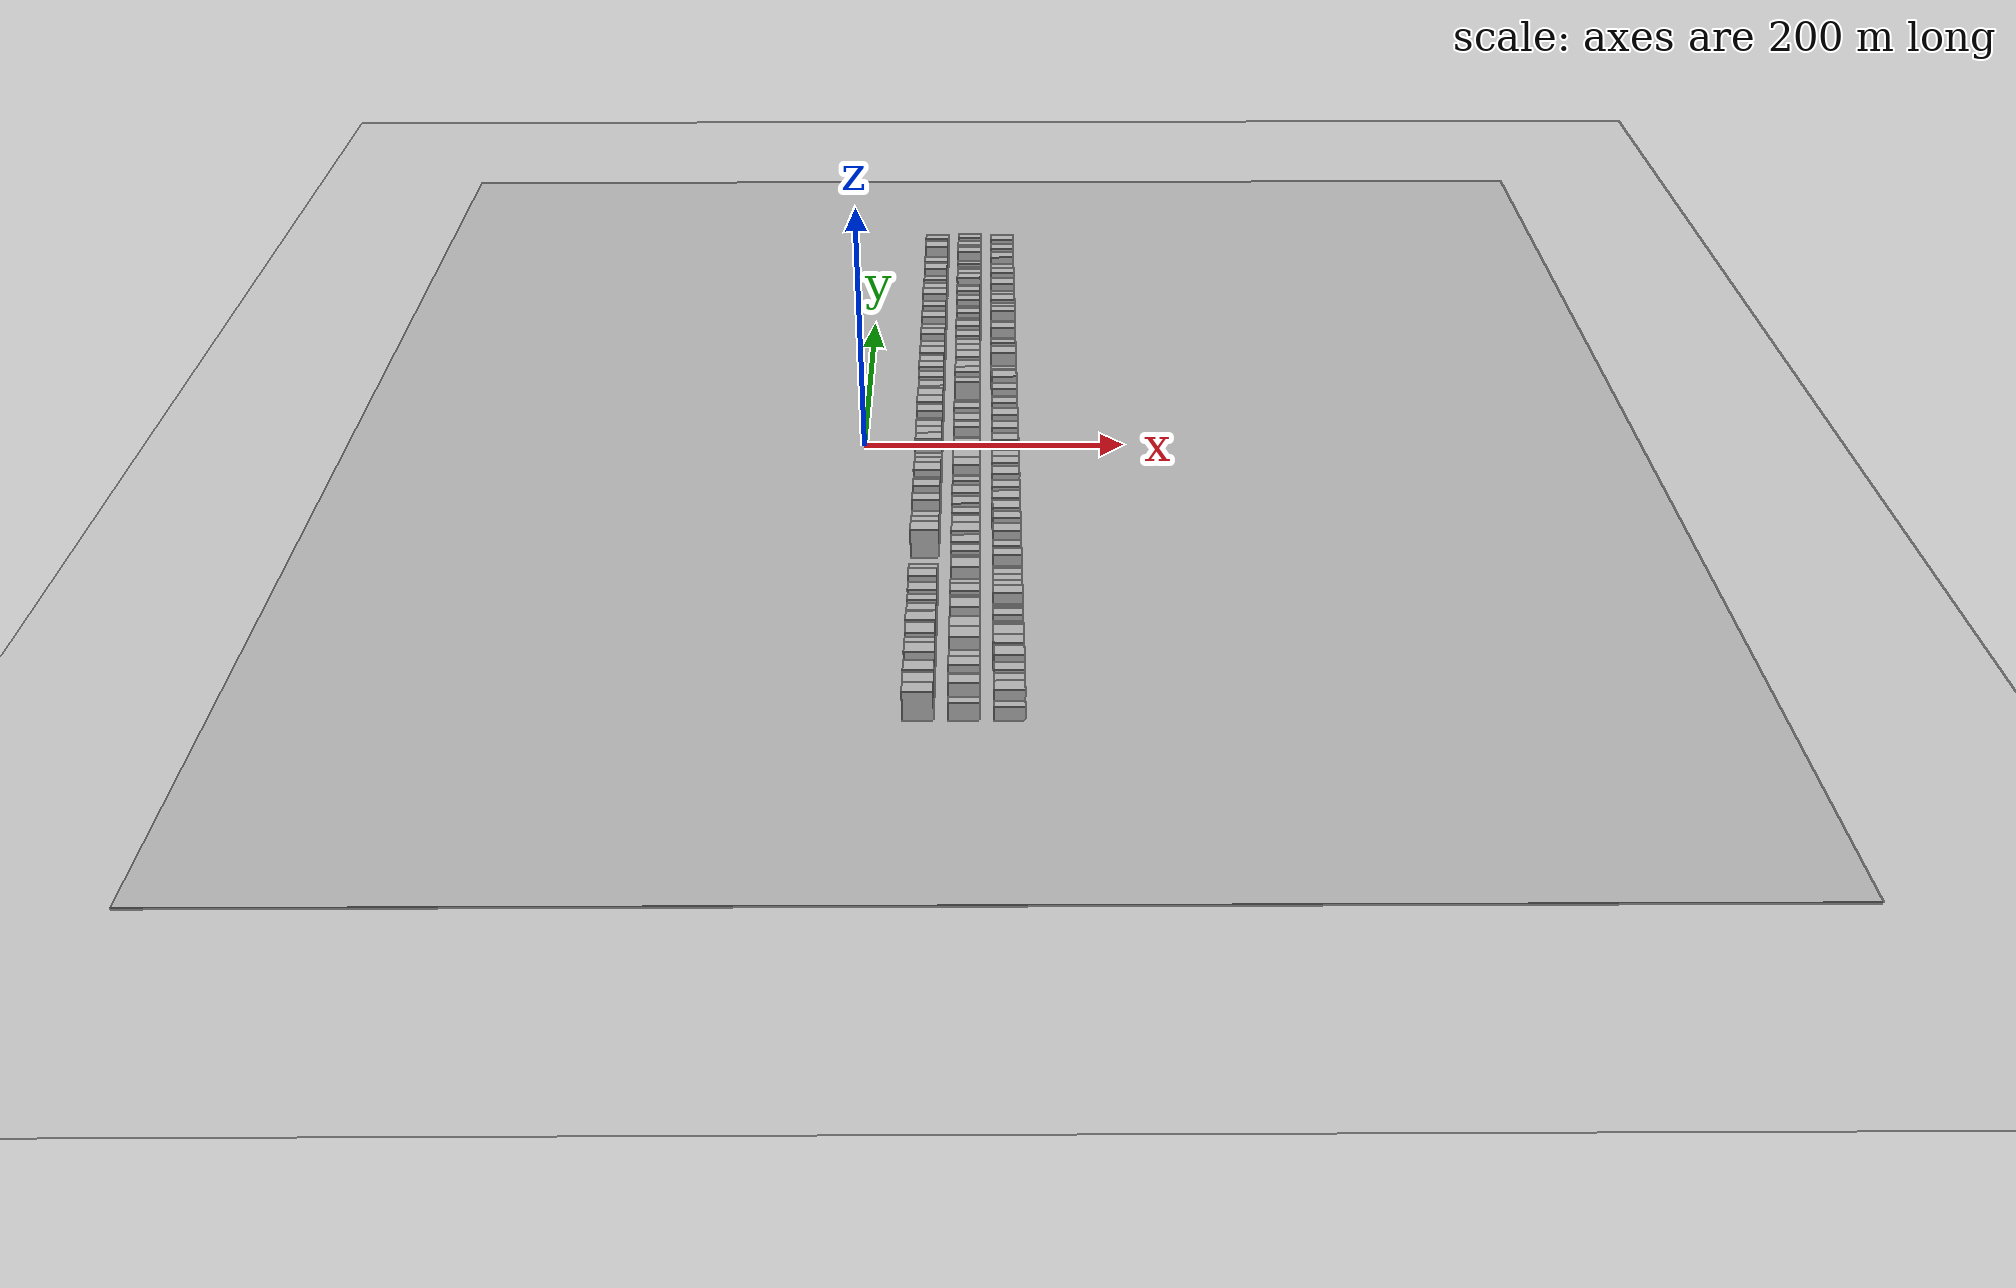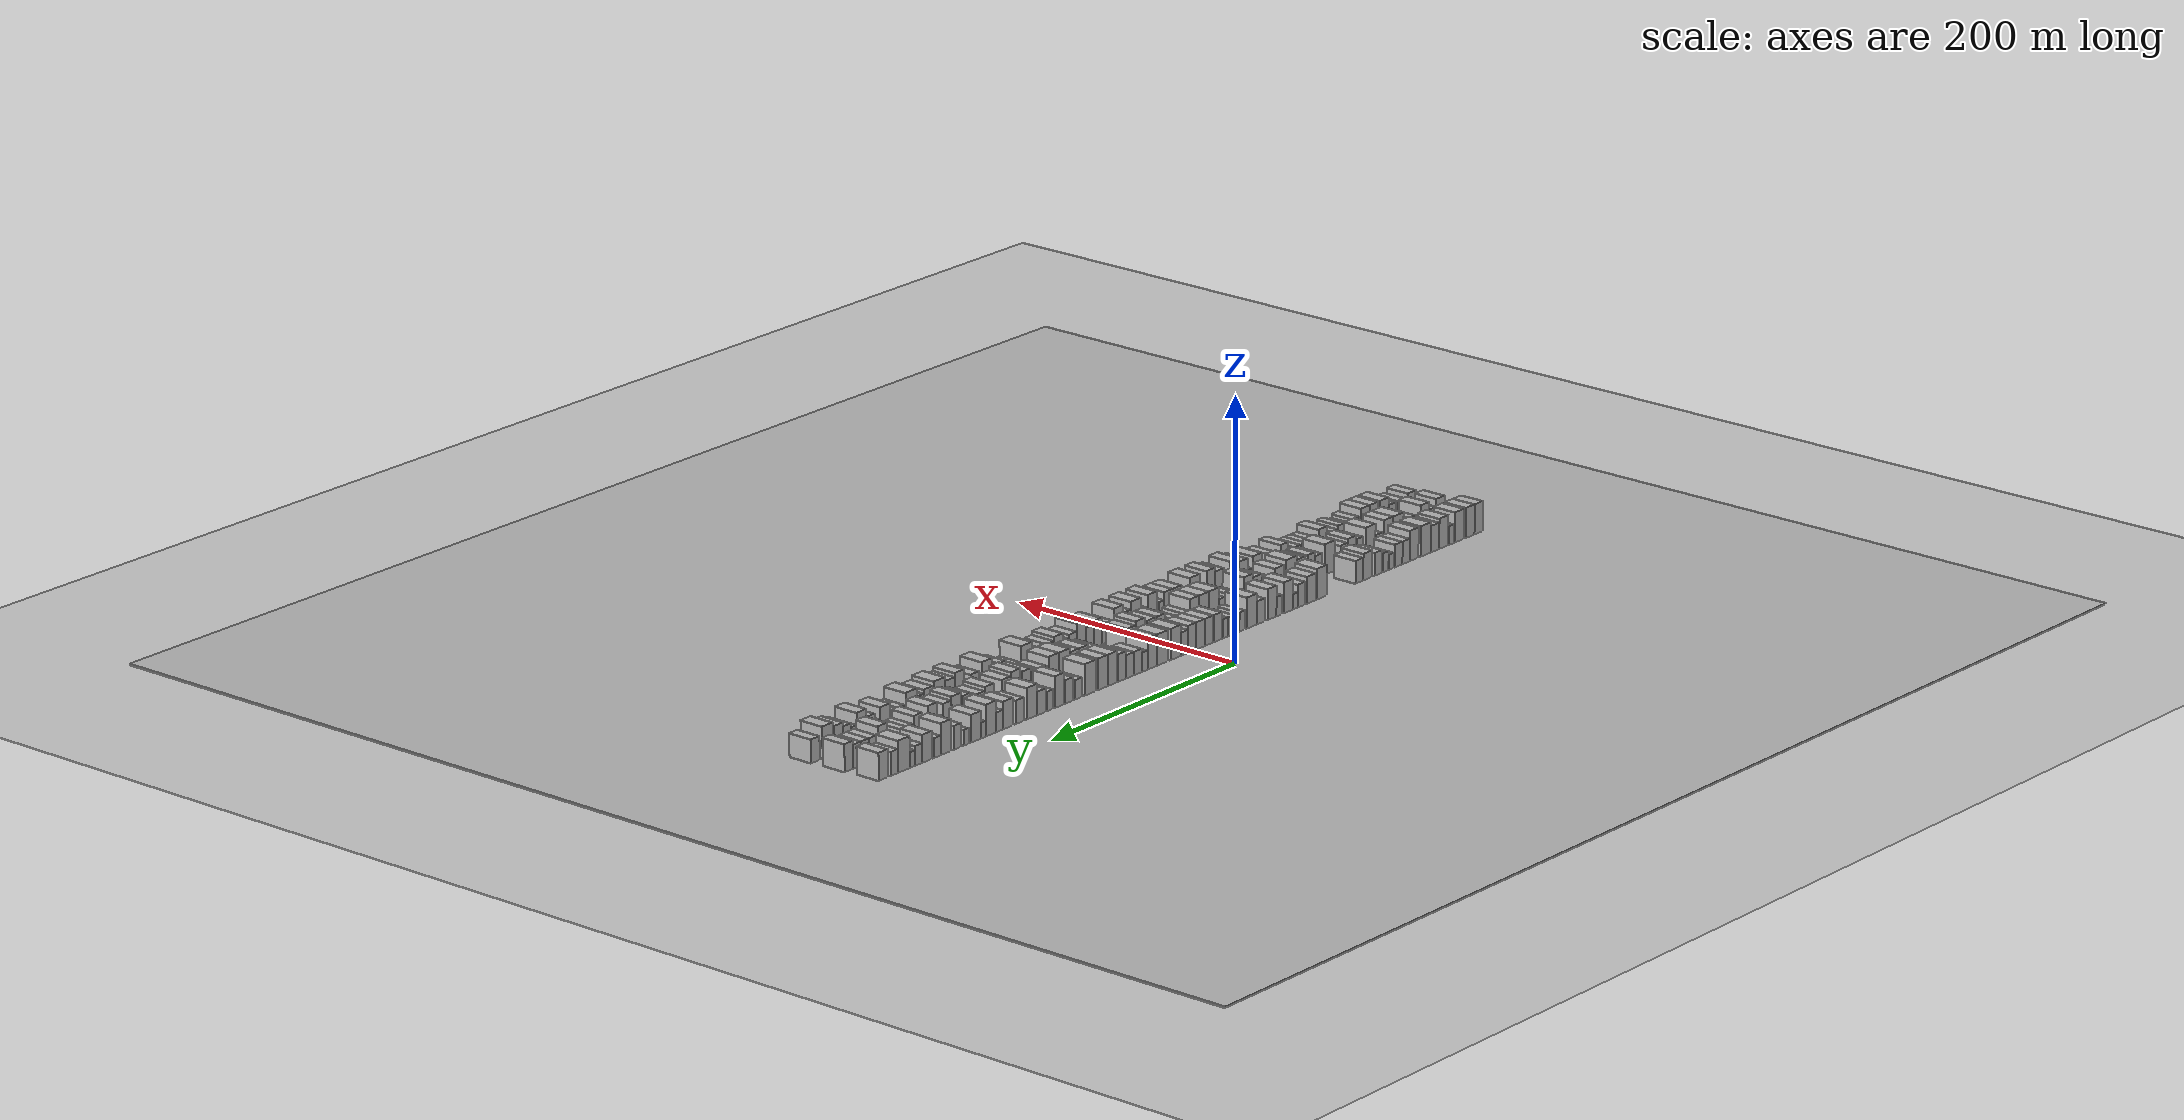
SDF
<?xml version="1.0" encoding="utf-8"?>

<sdf version="1.6">

   <world name="default">

      <gui fullscreen="0">

         <camera name="user_camera">

            <pose>-15 0 4.57585 0 0 0</pose>

            <view_controller>orbit</view_controller>

         </camera>

      </gui>

      <scene>

         <sky>

           <clouds>

             <speed>12</speed>

           </clouds>

         </sky>

         <ambient>0.4 0.4 0.4 1</ambient>

         <background>0.7 0.7 0.7 1</background>

         <shadows>1</shadows>

      </scene>

      <gravity>0 0 -9.8066</gravity>

      <magnetic_field>6e-06 2.3e-05 -4.2e-05</magnetic_field>

      <physics default="0" name="default_physics" type="ode">

         <ode>

            <solver>

               <type>quick</type>

               <iters>10</iters>

               <sor>1.0</sor>

               <use_dynamic_moi_rescaling>0</use_dynamic_moi_rescaling>

            </solver>

            <constraints>

               <cfm>0</cfm>

               <erp>0.2</erp>

               <contact_max_correcting_vel>100</contact_max_correcting_vel>

               <contact_surface_layer>0.001</contact_surface_layer>

            </constraints>

         </ode>

         <max_step_size>0.004</max_step_size>

         <real_time_factor>1</real_time_factor>

         <real_time_update_rate>250</real_time_update_rate>

      </physics>

      <light name="sun" type="directional">

         <cast_shadows>1</cast_shadows>

         <pose>0 0 10 0 0 0</pose>

         <diffuse>0.8 0.8 0.8 1</diffuse>

         <specular>0.2 0.2 0.2 1</specular>

         <attenuation>

            <range>1000</range>

            <constant>0.9</constant>

            <linear>0.01</linear>

            <quadratic>0.001</quadratic>

         </attenuation>

         <direction>-0.5 0.1 -0.9</direction>

      </light>

      <include>

         <name>ground_plane_1</name>

         <uri>model://HANNAS_ground_plane</uri>

         <pose>0 0 0  0 0 0</pose>

      </include>

      <include>

         <name>ground_plane_2</name>

         <uri>model://HANNAS_ground_plane</uri>

         <pose>100 0 0  0 0 0</pose>

      </include>

      <model name="building_1">

         <static>1</static>

         <pose frame="">50.0000 -331.0609 0 0.000000 0.000000 0.000000</pose>

         <link name="link">

            <pose frame="">0 0 12.00 0 0 0</pose>

            <collision name="collision">

               <geometry>

                  <box>

                     <size>20.0000 9.8782 24.0000</size>

                  </box>

               </geometry>

               <max_contacts>10</max_contacts>

               <surface>

                  <contact>

                     <ode/>

                  </contact>

                  <bounce/>

                  <friction>

                     <torsional>

                        <ode/>

                     </torsional>

                     <ode/>

                  </friction>

               </surface>

            </collision>

            <visual name="visual">

               <cast_shadows>0</cast_shadows>

               <geometry>

                  <box>

                     <size>20.0000 9.8782 24.0000</size>

                  </box>

               </geometry>

               <material>

                  <script>

                     <uri>model://HANNAS_wall/materials/scripts</uri>

                     <uri>model://HANNAS_wall/materials/textures</uri>

                     <name>vrc/HANNAS_wall</name>

                  </script>

               </material>

            </visual>

            <self_collide>0</self_collide>

            <enable_wind>0</enable_wind>

            <kinematic>0</kinematic>

         </link>

      </model>

      <model name="building_2">

         <static>1</static>

         <pose frame="">50.0000 -320.9515 0 0.000000 0.000000 0.000000</pose>

         <link name="link">

            <pose frame="">0 0 12.00 0 0 0</pose>

            <collision name="collision">

               <geometry>

                  <box>

                     <size>20.0000 10.3405 24.0000</size>

                  </box>

               </geometry>

               <max_contacts>10</max_contacts>

               <surface>

                  <contact>

                     <ode/>

                  </contact>

                  <bounce/>

                  <friction>

                     <torsional>

                        <ode/>

                     </torsional>

                     <ode/>

                  </friction>

               </surface>

            </collision>

            <visual name="visual">

               <cast_shadows>0</cast_shadows>

               <geometry>

                  <box>

                     <size>20.0000 10.3405 24.0000</size>

                  </box>

               </geometry>

               <material>

                  <script>

                     <uri>model://HANNAS_wall/materials/scripts</uri>

                     <uri>model://HANNAS_wall/materials/textures</uri>

                     <name>vrc/HANNAS_wall</name>

                  </script>

               </material>

            </visual>

            <self_collide>0</self_collide>

            <enable_wind>0</enable_wind>

            <kinematic>0</kinematic>

         </link>

      </model>

      <model name="building_3">

         <static>1</static>

         <pose frame="">50.0000 -308.2976 0 0.000000 0.000000 0.000000</pose>

         <link name="link">

            <pose frame="">0 0 12.00 0 0 0</pose>

            <collision name="collision">

               <geometry>

                  <box>

                     <size>20.0000 10.9674 24.0000</size>

                  </box>

               </geometry>

               <max_contacts>10</max_contacts>

               <surface>

                  <contact>

                     <ode/>

                  </contact>

                  <bounce/>

                  <friction>

                     <torsional>

                        <ode/>

                     </torsional>

                     <ode/>

                  </friction>

               </surface>

            </collision>

            <visual name="visual">

               <cast_shadows>0</cast_shadows>

               <geometry>

                  <box>

                     <size>20.0000 10.9674 24.0000</size>

                  </box>

               </geometry>

               <material>

                  <script>

                     <uri>model://HANNAS_wall/materials/scripts</uri>

                     <uri>model://HANNAS_wall/materials/textures</uri>

                     <name>vrc/HANNAS_wall</name>

                  </script>

               </material>

            </visual>

            <self_collide>0</self_collide>

            <enable_wind>0</enable_wind>

            <kinematic>0</kinematic>

         </link>

      </model>

      <model name="building_4">

         <static>1</static>

         <pose frame="">50.0000 -298.7830 0 0.000000 0.000000 0.000000</pose>

         <link name="link">

            <pose frame="">0 0 7.50 0 0 0</pose>

            <collision name="collision">

               <geometry>

                  <box>

                     <size>20.0000 6.0617 15.0000</size>

                  </box>

               </geometry>

               <max_contacts>10</max_contacts>

               <surface>

                  <contact>

                     <ode/>

                  </contact>

                  <bounce/>

                  <friction>

                     <torsional>

                        <ode/>

                     </torsional>

                     <ode/>

                  </friction>

               </surface>

            </collision>

            <visual name="visual">

               <cast_shadows>0</cast_shadows>

               <geometry>

                  <box>

                     <size>20.0000 6.0617 15.0000</size>

                  </box>

               </geometry>

               <material>

                  <script>

                     <uri>model://HANNAS_wall/materials/scripts</uri>

                     <uri>model://HANNAS_wall/materials/textures</uri>

                     <name>vrc/HANNAS_wall</name>

                  </script>

               </material>

            </visual>

            <self_collide>0</self_collide>

            <enable_wind>0</enable_wind>

            <kinematic>0</kinematic>

         </link>

      </model>

      <model name="building_5">

         <static>1</static>

         <pose frame="">50.0000 -289.4599 0 0.000000 0.000000 0.000000</pose>

         <link name="link">

            <pose frame="">0 0 12.00 0 0 0</pose>

            <collision name="collision">

               <geometry>

                  <box>

                     <size>20.0000 10.5843 24.0000</size>

                  </box>

               </geometry>

               <max_contacts>10</max_contacts>

               <surface>

                  <contact>

                     <ode/>

                  </contact>

                  <bounce/>

                  <friction>

                     <torsional>

                        <ode/>

                     </torsional>

                     <ode/>

                  </friction>

               </surface>

            </collision>

            <visual name="visual">

               <cast_shadows>0</cast_shadows>

               <geometry>

                  <box>

                     <size>20.0000 10.5843 24.0000</size>

                  </box>

               </geometry>

               <material>

                  <script>

                     <uri>model://HANNAS_wall/materials/scripts</uri>

                     <uri>model://HANNAS_wall/materials/textures</uri>

                     <name>vrc/HANNAS_wall</name>

                  </script>

               </material>

            </visual>

            <self_collide>0</self_collide>

            <enable_wind>0</enable_wind>

            <kinematic>0</kinematic>

         </link>

      </model>

      <model name="building_6">

         <static>1</static>

         <pose frame="">50.0000 -279.2546 0 0.000000 0.000000 0.000000</pose>

         <link name="link">

            <pose frame="">0 0 10.50 0 0 0</pose>

            <collision name="collision">

               <geometry>

                  <box>

                     <size>20.0000 9.8263 21.0000</size>

                  </box>

               </geometry>

               <max_contacts>10</max_contacts>

               <surface>

                  <contact>

                     <ode/>

                  </contact>

                  <bounce/>

                  <friction>

                     <torsional>

                        <ode/>

                     </torsional>

                     <ode/>

                  </friction>

               </surface>

            </collision>

            <visual name="visual">

               <cast_shadows>0</cast_shadows>

               <geometry>

                  <box>

                     <size>20.0000 9.8263 21.0000</size>

                  </box>

               </geometry>

               <material>

                  <script>

                     <uri>model://HANNAS_wall/materials/scripts</uri>

                     <uri>model://HANNAS_wall/materials/textures</uri>

                     <name>vrc/HANNAS_wall</name>

                  </script>

               </material>

            </visual>

            <self_collide>0</self_collide>

            <enable_wind>0</enable_wind>

            <kinematic>0</kinematic>

         </link>

      </model>

      <model name="building_7">

         <static>1</static>

         <pose frame="">50.0000 -268.4391 0 0.000000 0.000000 0.000000</pose>

         <link name="link">

            <pose frame="">0 0 12.00 0 0 0</pose>

            <collision name="collision">

               <geometry>

                  <box>

                     <size>20.0000 11.8049 24.0000</size>

                  </box>

               </geometry>

               <max_contacts>10</max_contacts>

               <surface>

                  <contact>

                     <ode/>

                  </contact>

                  <bounce/>

                  <friction>

                     <torsional>

                        <ode/>

                     </torsional>

                     <ode/>

                  </friction>

               </surface>

            </collision>

            <visual name="visual">

               <cast_shadows>0</cast_shadows>

               <geometry>

                  <box>

                     <size>20.0000 11.8049 24.0000</size>

                  </box>

               </geometry>

               <material>

                  <script>

                     <uri>model://HANNAS_wall/materials/scripts</uri>

                     <uri>model://HANNAS_wall/materials/textures</uri>

                     <name>vrc/HANNAS_wall</name>

                  </script>

               </material>

            </visual>

            <self_collide>0</self_collide>

            <enable_wind>0</enable_wind>

            <kinematic>0</kinematic>

         </link>

      </model>

      <model name="building_8">

         <static>1</static>

         <pose frame="">50.0000 -254.4093 0 0.000000 0.000000 0.000000</pose>

         <link name="link">

            <pose frame="">0 0 12.00 0 0 0</pose>

            <collision name="collision">

               <geometry>

                  <box>

                     <size>20.0000 10.2547 24.0000</size>

                  </box>

               </geometry>

               <max_contacts>10</max_contacts>

               <surface>

                  <contact>

                     <ode/>

                  </contact>

                  <bounce/>

                  <friction>

                     <torsional>

                        <ode/>

                     </torsional>

                     <ode/>

                  </friction>

               </surface>

            </collision>

            <visual name="visual">

               <cast_shadows>0</cast_shadows>

               <geometry>

                  <box>

                     <size>20.0000 10.2547 24.0000</size>

                  </box>

               </geometry>

               <material>

                  <script>

                     <uri>model://HANNAS_wall/materials/scripts</uri>

                     <uri>model://HANNAS_wall/materials/textures</uri>

                     <name>vrc/HANNAS_wall</name>

                  </script>

               </material>

            </visual>

            <self_collide>0</self_collide>

            <enable_wind>0</enable_wind>

            <kinematic>0</kinematic>

         </link>

      </model>

      <model name="building_9">

         <static>1</static>

         <pose frame="">50.0000 -245.0454 0 0.000000 0.000000 0.000000</pose>

         <link name="link">

            <pose frame="">0 0 9.00 0 0 0</pose>

            <collision name="collision">

               <geometry>

                  <box>

                     <size>20.0000 8.4732 18.0000</size>

                  </box>

               </geometry>

               <max_contacts>10</max_contacts>

               <surface>

                  <contact>

                     <ode/>

                  </contact>

                  <bounce/>

                  <friction>

                     <torsional>

                        <ode/>

                     </torsional>

                     <ode/>

                  </friction>

               </surface>

            </collision>

            <visual name="visual">

               <cast_shadows>0</cast_shadows>

               <geometry>

                  <box>

                     <size>20.0000 8.4732 18.0000</size>

                  </box>

               </geometry>

               <material>

                  <script>

                     <uri>model://HANNAS_wall/materials/scripts</uri>

                     <uri>model://HANNAS_wall/materials/textures</uri>

                     <name>vrc/HANNAS_wall</name>

                  </script>

               </material>

            </visual>

            <self_collide>0</self_collide>

            <enable_wind>0</enable_wind>

            <kinematic>0</kinematic>

         </link>

      </model>

      <model name="building_10">

         <static>1</static>

         <pose frame="">50.0000 -236.5340 0 0.000000 0.000000 0.000000</pose>

         <link name="link">

            <pose frame="">0 0 9.00 0 0 0</pose>

            <collision name="collision">

               <geometry>

                  <box>

                     <size>20.0000 8.5496 18.0000</size>

                  </box>

               </geometry>

               <max_contacts>10</max_contacts>

               <surface>

                  <contact>

                     <ode/>

                  </contact>

                  <bounce/>

                  <friction>

                     <torsional>

                        <ode/>

                     </torsional>

                     <ode/>

                  </friction>

               </surface>

            </collision>

            <visual name="visual">

               <cast_shadows>0</cast_shadows>

               <geometry>

                  <box>

                     <size>20.0000 8.5496 18.0000</size>

                  </box>

               </geometry>

               <material>

                  <script>

                     <uri>model://HANNAS_wall/materials/scripts</uri>

                     <uri>model://HANNAS_wall/materials/textures</uri>

                     <name>vrc/HANNAS_wall</name>

                  </script>

               </material>

            </visual>

            <self_collide>0</self_collide>

            <enable_wind>0</enable_wind>

            <kinematic>0</kinematic>

         </link>

      </model>

      <model name="building_11">

         <static>1</static>

         <pose frame="">50.0000 -228.3229 0 0.000000 0.000000 0.000000</pose>

         <link name="link">

            <pose frame="">0 0 6.00 0 0 0</pose>

            <collision name="collision">

               <geometry>

                  <box>

                     <size>20.0000 5.8725 12.0000</size>

                  </box>

               </geometry>

               <max_contacts>10</max_contacts>

               <surface>

                  <contact>

                     <ode/>

                  </contact>

                  <bounce/>

                  <friction>

                     <torsional>

                        <ode/>

                     </torsional>

                     <ode/>

                  </friction>

               </surface>

            </collision>

            <visual name="visual">

               <cast_shadows>0</cast_shadows>

               <geometry>

                  <box>

                     <size>20.0000 5.8725 12.0000</size>

                  </box>

               </geometry>

               <material>

                  <script>

                     <uri>model://HANNAS_wall/materials/scripts</uri>

                     <uri>model://HANNAS_wall/materials/textures</uri>

                     <name>vrc/HANNAS_wall</name>

                  </script>

               </material>

            </visual>

            <self_collide>0</self_collide>

            <enable_wind>0</enable_wind>

            <kinematic>0</kinematic>

         </link>

      </model>

      <model name="building_12">

         <static>1</static>

         <pose frame="">50.0000 -221.2044 0 0.000000 0.000000 0.000000</pose>

         <link name="link">

            <pose frame="">0 0 7.50 0 0 0</pose>

            <collision name="collision">

               <geometry>

                  <box>

                     <size>20.0000 6.3645 15.0000</size>

                  </box>

               </geometry>

               <max_contacts>10</max_contacts>

               <surface>

                  <contact>

                     <ode/>

                  </contact>

                  <bounce/>

                  <friction>

                     <torsional>

                        <ode/>

                     </torsional>

                     <ode/>

                  </friction>

               </surface>

            </collision>

            <visual name="visual">

               <cast_shadows>0</cast_shadows>

               <geometry>

                  <box>

                     <size>20.0000 6.3645 15.0000</size>

                  </box>

               </geometry>

               <material>

                  <script>

                     <uri>model://HANNAS_wall/materials/scripts</uri>

                     <uri>model://HANNAS_wall/materials/textures</uri>

                     <name>vrc/HANNAS_wall</name>

                  </script>

               </material>

            </visual>

            <self_collide>0</self_collide>

            <enable_wind>0</enable_wind>

            <kinematic>0</kinematic>

         </link>

      </model>

      <model name="building_13">

         <static>1</static>

         <pose frame="">50.0000 -212.6787 0 0.000000 0.000000 0.000000</pose>

         <link name="link">

            <pose frame="">0 0 9.00 0 0 0</pose>

            <collision name="collision">

               <geometry>

                  <box>

                     <size>20.0000 8.6868 18.0000</size>

                  </box>

               </geometry>

               <max_contacts>10</max_contacts>

               <surface>

                  <contact>

                     <ode/>

                  </contact>

                  <bounce/>

                  <friction>

                     <torsional>

                        <ode/>

                     </torsional>

                     <ode/>

                  </friction>

               </surface>

            </collision>

            <visual name="visual">

               <cast_shadows>0</cast_shadows>

               <geometry>

                  <box>

                     <size>20.0000 8.6868 18.0000</size>

                  </box>

               </geometry>

               <material>

                  <script>

                     <uri>model://HANNAS_wall/materials/scripts</uri>

                     <uri>model://HANNAS_wall/materials/textures</uri>

                     <name>vrc/HANNAS_wall</name>

                  </script>

               </material>

            </visual>

            <self_collide>0</self_collide>

            <enable_wind>0</enable_wind>

            <kinematic>0</kinematic>

         </link>

      </model>

      <model name="building_14">

         <static>1</static>

         <pose frame="">50.0000 -200.2189 0 0.000000 0.000000 0.000000</pose>

         <link name="link">

            <pose frame="">0 0 10.50 0 0 0</pose>

            <collision name="collision">

               <geometry>

                  <box>

                     <size>20.0000 10.2329 21.0000</size>

                  </box>

               </geometry>

               <max_contacts>10</max_contacts>

               <surface>

                  <contact>

                     <ode/>

                  </contact>

                  <bounce/>

                  <friction>

                     <torsional>

                        <ode/>

                     </torsional>

                     <ode/>

                  </friction>

               </surface>

            </collision>

            <visual name="visual">

               <cast_shadows>0</cast_shadows>

               <geometry>

                  <box>

                     <size>20.0000 10.2329 21.0000</size>

                  </box>

               </geometry>

               <material>

                  <script>

                     <uri>model://HANNAS_wall/materials/scripts</uri>

                     <uri>model://HANNAS_wall/materials/textures</uri>

                     <name>vrc/HANNAS_wall</name>

                  </script>

               </material>

            </visual>

            <self_collide>0</self_collide>

            <enable_wind>0</enable_wind>

            <kinematic>0</kinematic>

         </link>

      </model>

      <model name="building_15">

         <static>1</static>

         <pose frame="">50.0000 -190.6739 0 0.000000 0.000000 0.000000</pose>

         <link name="link">

            <pose frame="">0 0 9.00 0 0 0</pose>

            <collision name="collision">

               <geometry>

                  <box>

                     <size>20.0000 8.8571 18.0000</size>

                  </box>

               </geometry>

               <max_contacts>10</max_contacts>

               <surface>

                  <contact>

                     <ode/>

                  </contact>

                  <bounce/>

                  <friction>

                     <torsional>

                        <ode/>

                     </torsional>

                     <ode/>

                  </friction>

               </surface>

            </collision>

            <visual name="visual">

               <cast_shadows>0</cast_shadows>

               <geometry>

                  <box>

                     <size>20.0000 8.8571 18.0000</size>

                  </box>

               </geometry>

               <material>

                  <script>

                     <uri>model://HANNAS_wall/materials/scripts</uri>

                     <uri>model://HANNAS_wall/materials/textures</uri>

                     <name>vrc/HANNAS_wall</name>

                  </script>

               </material>

            </visual>

            <self_collide>0</self_collide>

            <enable_wind>0</enable_wind>

            <kinematic>0</kinematic>

         </link>

      </model>

      <model name="building_16">

         <static>1</static>

         <pose frame="">50.0000 -147.3587 0 0.000000 0.000000 0.000000</pose>

         <link name="link">

            <pose frame="">0 0 12.00 0 0 0</pose>

            <collision name="collision">

               <geometry>

                  <box>

                     <size>20.0000 11.9244 24.0000</size>

                  </box>

               </geometry>

               <max_contacts>10</max_contacts>

               <surface>

                  <contact>

                     <ode/>

                  </contact>

                  <bounce/>

                  <friction>

                     <torsional>

                        <ode/>

                     </torsional>

                     <ode/>

                  </friction>

               </surface>

            </collision>

            <visual name="visual">

               <cast_shadows>0</cast_shadows>

               <geometry>

                  <box>

                     <size>20.0000 11.9244 24.0000</size>

                  </box>

               </geometry>

               <material>

                  <script>

                     <uri>model://HANNAS_wall/materials/scripts</uri>

                     <uri>model://HANNAS_wall/materials/textures</uri>

                     <name>vrc/HANNAS_wall</name>

                  </script>

               </material>

            </visual>

            <self_collide>0</self_collide>

            <enable_wind>0</enable_wind>

            <kinematic>0</kinematic>

         </link>

      </model>

      <model name="building_17">

         <static>1</static>

         <pose frame="">50.0000 -135.2975 0 0.000000 0.000000 0.000000</pose>

         <link name="link">

            <pose frame="">0 0 10.50 0 0 0</pose>

            <collision name="collision">

               <geometry>

                  <box>

                     <size>20.0000 10.1980 21.0000</size>

                  </box>

               </geometry>

               <max_contacts>10</max_contacts>

               <surface>

                  <contact>

                     <ode/>

                  </contact>

                  <bounce/>

                  <friction>

                     <torsional>

                        <ode/>

                     </torsional>

                     <ode/>

                  </friction>

               </surface>

            </collision>

            <visual name="visual">

               <cast_shadows>0</cast_shadows>

               <geometry>

                  <box>

                     <size>20.0000 10.1980 21.0000</size>

                  </box>

               </geometry>

               <material>

                  <script>

                     <uri>model://HANNAS_wall/materials/scripts</uri>

                     <uri>model://HANNAS_wall/materials/textures</uri>

                     <name>vrc/HANNAS_wall</name>

                  </script>

               </material>

            </visual>

            <self_collide>0</self_collide>

            <enable_wind>0</enable_wind>

            <kinematic>0</kinematic>

         </link>

      </model>

      <model name="building_18">

         <static>1</static>

         <pose frame="">50.0000 -123.8516 0 0.000000 0.000000 0.000000</pose>

         <link name="link">

            <pose frame="">0 0 9.00 0 0 0</pose>

            <collision name="collision">

               <geometry>

                  <box>

                     <size>20.0000 8.6937 18.0000</size>

                  </box>

               </geometry>

               <max_contacts>10</max_contacts>

               <surface>

                  <contact>

                     <ode/>

                  </contact>

                  <bounce/>

                  <friction>

                     <torsional>

                        <ode/>

                     </torsional>

                     <ode/>

                  </friction>

               </surface>

            </collision>

            <visual name="visual">

               <cast_shadows>0</cast_shadows>

               <geometry>

                  <box>

                     <size>20.0000 8.6937 18.0000</size>

                  </box>

               </geometry>

               <material>

                  <script>

                     <uri>model://HANNAS_wall/materials/scripts</uri>

                     <uri>model://HANNAS_wall/materials/textures</uri>

                     <name>vrc/HANNAS_wall</name>

                  </script>

               </material>

            </visual>

            <self_collide>0</self_collide>

            <enable_wind>0</enable_wind>

            <kinematic>0</kinematic>

         </link>

      </model>

      <model name="building_19">

         <static>1</static>

         <pose frame="">50.0000 -116.8912 0 0.000000 0.000000 0.000000</pose>

         <link name="link">

            <pose frame="">0 0 6.00 0 0 0</pose>

            <collision name="collision">

               <geometry>

                  <box>

                     <size>20.0000 5.2271 12.0000</size>

                  </box>

               </geometry>

               <max_contacts>10</max_contacts>

               <surface>

                  <contact>

                     <ode/>

                  </contact>

                  <bounce/>

                  <friction>

                     <torsional>

                        <ode/>

                     </torsional>

                     <ode/>

                  </friction>

               </surface>

            </collision>

            <visual name="visual">

               <cast_shadows>0</cast_shadows>

               <geometry>

                  <box>

                     <size>20.0000 5.2271 12.0000</size>

                  </box>

               </geometry>

               <material>

                  <script>

                     <uri>model://HANNAS_wall/materials/scripts</uri>

                     <uri>model://HANNAS_wall/materials/textures</uri>

                     <name>vrc/HANNAS_wall</name>

                  </script>

               </material>

            </visual>

            <self_collide>0</self_collide>

            <enable_wind>0</enable_wind>

            <kinematic>0</kinematic>

         </link>

      </model>

      <model name="building_20">

         <static>1</static>

         <pose frame="">50.0000 -109.0823 0 0.000000 0.000000 0.000000</pose>

         <link name="link">

            <pose frame="">0 0 12.00 0 0 0</pose>

            <collision name="collision">

               <geometry>

                  <box>

                     <size>20.0000 10.3908 24.0000</size>

                  </box>

               </geometry>

               <max_contacts>10</max_contacts>

               <surface>

                  <contact>

                     <ode/>

                  </contact>

                  <bounce/>

                  <friction>

                     <torsional>

                        <ode/>

                     </torsional>

                     <ode/>

                  </friction>

               </surface>

            </collision>

            <visual name="visual">

               <cast_shadows>0</cast_shadows>

               <geometry>

                  <box>

                     <size>20.0000 10.3908 24.0000</size>

                  </box>

               </geometry>

               <material>

                  <script>

                     <uri>model://HANNAS_wall/materials/scripts</uri>

                     <uri>model://HANNAS_wall/materials/textures</uri>

                     <name>vrc/HANNAS_wall</name>

                  </script>

               </material>

            </visual>

            <self_collide>0</self_collide>

            <enable_wind>0</enable_wind>

            <kinematic>0</kinematic>

         </link>

      </model>

      <model name="building_21">

         <static>1</static>

         <pose frame="">50.0000 -98.5561 0 0.000000 0.000000 0.000000</pose>

         <link name="link">

            <pose frame="">0 0 7.50 0 0 0</pose>

            <collision name="collision">

               <geometry>

                  <box>

                     <size>20.0000 6.6615 15.0000</size>

                  </box>

               </geometry>

               <max_contacts>10</max_contacts>

               <surface>

                  <contact>

                     <ode/>

                  </contact>

                  <bounce/>

                  <friction>

                     <torsional>

                        <ode/>

                     </torsional>

                     <ode/>

                  </friction>

               </surface>

            </collision>

            <visual name="visual">

               <cast_shadows>0</cast_shadows>

               <geometry>

                  <box>

                     <size>20.0000 6.6615 15.0000</size>

                  </box>

               </geometry>

               <material>

                  <script>

                     <uri>model://HANNAS_wall/materials/scripts</uri>

                     <uri>model://HANNAS_wall/materials/textures</uri>

                     <name>vrc/HANNAS_wall</name>

                  </script>

               </material>

            </visual>

            <self_collide>0</self_collide>

            <enable_wind>0</enable_wind>

            <kinematic>0</kinematic>

         </link>

      </model>

      <model name="building_22">

         <static>1</static>

         <pose frame="">50.0000 -90.1369 0 0.000000 0.000000 0.000000</pose>

         <link name="link">

            <pose frame="">0 0 12.00 0 0 0</pose>

            <collision name="collision">

               <geometry>

                  <box>

                     <size>20.0000 10.1769 24.0000</size>

                  </box>

               </geometry>

               <max_contacts>10</max_contacts>

               <surface>

                  <contact>

                     <ode/>

                  </contact>

                  <bounce/>

                  <friction>

                     <torsional>

                        <ode/>

                     </torsional>

                     <ode/>

                  </friction>

               </surface>

            </collision>

            <visual name="visual">

               <cast_shadows>0</cast_shadows>

               <geometry>

                  <box>

                     <size>20.0000 10.1769 24.0000</size>

                  </box>

               </geometry>

               <material>

                  <script>

                     <uri>model://HANNAS_wall/materials/scripts</uri>

                     <uri>model://HANNAS_wall/materials/textures</uri>

                     <name>vrc/HANNAS_wall</name>

                  </script>

               </material>

            </visual>

            <self_collide>0</self_collide>

            <enable_wind>0</enable_wind>

            <kinematic>0</kinematic>

         </link>

      </model>

      <model name="building_23">

         <static>1</static>

         <pose frame="">50.0000 -77.6514 0 0.000000 0.000000 0.000000</pose>

         <link name="link">

            <pose frame="">0 0 9.00 0 0 0</pose>

            <collision name="collision">

               <geometry>

                  <box>

                     <size>20.0000 8.7939 18.0000</size>

                  </box>

               </geometry>

               <max_contacts>10</max_contacts>

               <surface>

                  <contact>

                     <ode/>

                  </contact>

                  <bounce/>

                  <friction>

                     <torsional>

                        <ode/>

                     </torsional>

                     <ode/>

                  </friction>

               </surface>

            </collision>

            <visual name="visual">

               <cast_shadows>0</cast_shadows>

               <geometry>

                  <box>

                     <size>20.0000 8.7939 18.0000</size>

                  </box>

               </geometry>

               <material>

                  <script>

                     <uri>model://HANNAS_wall/materials/scripts</uri>

                     <uri>model://HANNAS_wall/materials/textures</uri>

                     <name>vrc/HANNAS_wall</name>

                  </script>

               </material>

            </visual>

            <self_collide>0</self_collide>

            <enable_wind>0</enable_wind>

            <kinematic>0</kinematic>

         </link>

      </model>

      <model name="building_24">

         <static>1</static>

         <pose frame="">50.0000 -67.5716 0 0.000000 0.000000 0.000000</pose>

         <link name="link">

            <pose frame="">0 0 12.00 0 0 0</pose>

            <collision name="collision">

               <geometry>

                  <box>

                     <size>20.0000 11.3658 24.0000</size>

                  </box>

               </geometry>

               <max_contacts>10</max_contacts>

               <surface>

                  <contact>

                     <ode/>

                  </contact>

                  <bounce/>

                  <friction>

                     <torsional>

                        <ode/>

                     </torsional>

                     <ode/>

                  </friction>

               </surface>

            </collision>

            <visual name="visual">

               <cast_shadows>0</cast_shadows>

               <geometry>

                  <box>

                     <size>20.0000 11.3658 24.0000</size>

                  </box>

               </geometry>

               <material>

                  <script>

                     <uri>model://HANNAS_wall/materials/scripts</uri>

                     <uri>model://HANNAS_wall/materials/textures</uri>

                     <name>vrc/HANNAS_wall</name>

                  </script>

               </material>

            </visual>

            <self_collide>0</self_collide>

            <enable_wind>0</enable_wind>

            <kinematic>0</kinematic>

         </link>

      </model>

      <model name="building_25">

         <static>1</static>

         <pose frame="">50.0000 -56.5981 0 0.000000 0.000000 0.000000</pose>

         <link name="link">

            <pose frame="">0 0 7.50 0 0 0</pose>

            <collision name="collision">

               <geometry>

                  <box>

                     <size>20.0000 6.5810 15.0000</size>

                  </box>

               </geometry>

               <max_contacts>10</max_contacts>

               <surface>

                  <contact>

                     <ode/>

                  </contact>

                  <bounce/>

                  <friction>

                     <torsional>

                        <ode/>

                     </torsional>

                     <ode/>

                  </friction>

               </surface>

            </collision>

            <visual name="visual">

               <cast_shadows>0</cast_shadows>

               <geometry>

                  <box>

                     <size>20.0000 6.5810 15.0000</size>

                  </box>

               </geometry>

               <material>

                  <script>

                     <uri>model://HANNAS_wall/materials/scripts</uri>

                     <uri>model://HANNAS_wall/materials/textures</uri>

                     <name>vrc/HANNAS_wall</name>

                  </script>

               </material>

            </visual>

            <self_collide>0</self_collide>

            <enable_wind>0</enable_wind>

            <kinematic>0</kinematic>

         </link>

      </model>

      <model name="building_26">

         <static>1</static>

         <pose frame="">50.0000 -50.3149 0 0.000000 0.000000 0.000000</pose>

         <link name="link">

            <pose frame="">0 0 6.00 0 0 0</pose>

            <collision name="collision">

               <geometry>

                  <box>

                     <size>20.0000 5.9853 12.0000</size>

                  </box>

               </geometry>

               <max_contacts>10</max_contacts>

               <surface>

                  <contact>

                     <ode/>

                  </contact>

                  <bounce/>

                  <friction>

                     <torsional>

                        <ode/>

                     </torsional>

                     <ode/>

                  </friction>

               </surface>

            </collision>

            <visual name="visual">

               <cast_shadows>0</cast_shadows>

               <geometry>

                  <box>

                     <size>20.0000 5.9853 12.0000</size>

                  </box>

               </geometry>

               <material>

                  <script>

                     <uri>model://HANNAS_wall/materials/scripts</uri>

                     <uri>model://HANNAS_wall/materials/textures</uri>

                     <name>vrc/HANNAS_wall</name>

                  </script>

               </material>

            </visual>

            <self_collide>0</self_collide>

            <enable_wind>0</enable_wind>

            <kinematic>0</kinematic>

         </link>

      </model>

      <model name="building_27">

         <static>1</static>

         <pose frame="">50.0000 -43.8723 0 0.000000 0.000000 0.000000</pose>

         <link name="link">

            <pose frame="">0 0 7.50 0 0 0</pose>

            <collision name="collision">

               <geometry>

                  <box>

                     <size>20.0000 6.9000 15.0000</size>

                  </box>

               </geometry>

               <max_contacts>10</max_contacts>

               <surface>

                  <contact>

                     <ode/>

                  </contact>

                  <bounce/>

                  <friction>

                     <torsional>

                        <ode/>

                     </torsional>

                     <ode/>

                  </friction>

               </surface>

            </collision>

            <visual name="visual">

               <cast_shadows>0</cast_shadows>

               <geometry>

                  <box>

                     <size>20.0000 6.9000 15.0000</size>

                  </box>

               </geometry>

               <material>

                  <script>

                     <uri>model://HANNAS_wall/materials/scripts</uri>

                     <uri>model://HANNAS_wall/materials/textures</uri>

                     <name>vrc/HANNAS_wall</name>

                  </script>

               </material>

            </visual>

            <self_collide>0</self_collide>

            <enable_wind>0</enable_wind>

            <kinematic>0</kinematic>

         </link>

      </model>

      <model name="building_28">

         <static>1</static>

         <pose frame="">50.0000 -37.3803 0 0.000000 0.000000 0.000000</pose>

         <link name="link">

            <pose frame="">0 0 7.50 0 0 0</pose>

            <collision name="collision">

               <geometry>

                  <box>

                     <size>20.0000 6.0840 15.0000</size>

                  </box>

               </geometry>

               <max_contacts>10</max_contacts>

               <surface>

                  <contact>

                     <ode/>

                  </contact>

                  <bounce/>

                  <friction>

                     <torsional>

                        <ode/>

                     </torsional>

                     <ode/>

                  </friction>

               </surface>

            </collision>

            <visual name="visual">

               <cast_shadows>0</cast_shadows>

               <geometry>

                  <box>

                     <size>20.0000 6.0840 15.0000</size>

                  </box>

               </geometry>

               <material>

                  <script>

                     <uri>model://HANNAS_wall/materials/scripts</uri>

                     <uri>model://HANNAS_wall/materials/textures</uri>

                     <name>vrc/HANNAS_wall</name>

                  </script>

               </material>

            </visual>

            <self_collide>0</self_collide>

            <enable_wind>0</enable_wind>

            <kinematic>0</kinematic>

         </link>

      </model>

      <model name="building_29">

         <static>1</static>

         <pose frame="">50.0000 -28.9255 0 0.000000 0.000000 0.000000</pose>

         <link name="link">

            <pose frame="">0 0 10.50 0 0 0</pose>

            <collision name="collision">

               <geometry>

                  <box>

                     <size>20.0000 8.8257 21.0000</size>

                  </box>

               </geometry>

               <max_contacts>10</max_contacts>

               <surface>

                  <contact>

                     <ode/>

                  </contact>

                  <bounce/>

                  <friction>

                     <torsional>

                        <ode/>

                     </torsional>

                     <ode/>

                  </friction>

               </surface>

            </collision>

            <visual name="visual">

               <cast_shadows>0</cast_shadows>

               <geometry>

                  <box>

                     <size>20.0000 8.8257 21.0000</size>

                  </box>

               </geometry>

               <material>

                  <script>

                     <uri>model://HANNAS_wall/materials/scripts</uri>

                     <uri>model://HANNAS_wall/materials/textures</uri>

                     <name>vrc/HANNAS_wall</name>

                  </script>

               </material>

            </visual>

            <self_collide>0</self_collide>

            <enable_wind>0</enable_wind>

            <kinematic>0</kinematic>

         </link>

      </model>

      <model name="building_30">

         <static>1</static>

         <pose frame="">50.0000 -18.8104 0 0.000000 0.000000 0.000000</pose>

         <link name="link">

            <pose frame="">0 0 10.50 0 0 0</pose>

            <collision name="collision">

               <geometry>

                  <box>

                     <size>20.0000 9.4045 21.0000</size>

                  </box>

               </geometry>

               <max_contacts>10</max_contacts>

               <surface>

                  <contact>

                     <ode/>

                  </contact>

                  <bounce/>

                  <friction>

                     <torsional>

                        <ode/>

                     </torsional>

                     <ode/>

                  </friction>

               </surface>

            </collision>

            <visual name="visual">

               <cast_shadows>0</cast_shadows>

               <geometry>

                  <box>

                     <size>20.0000 9.4045 21.0000</size>

                  </box>

               </geometry>

               <material>

                  <script>

                     <uri>model://HANNAS_wall/materials/scripts</uri>

                     <uri>model://HANNAS_wall/materials/textures</uri>

                     <name>vrc/HANNAS_wall</name>

                  </script>

               </material>

            </visual>

            <self_collide>0</self_collide>

            <enable_wind>0</enable_wind>

            <kinematic>0</kinematic>

         </link>

      </model>

      <model name="building_31">

         <static>1</static>

         <pose frame="">50.0000 -9.4515 0 0.000000 0.000000 0.000000</pose>

         <link name="link">

            <pose frame="">0 0 10.50 0 0 0</pose>

            <collision name="collision">

               <geometry>

                  <box>

                     <size>20.0000 9.3133 21.0000</size>

                  </box>

               </geometry>

               <max_contacts>10</max_contacts>

               <surface>

                  <contact>

                     <ode/>

                  </contact>

                  <bounce/>

                  <friction>

                     <torsional>

                        <ode/>

                     </torsional>

                     <ode/>

                  </friction>

               </surface>

            </collision>

            <visual name="visual">

               <cast_shadows>0</cast_shadows>

               <geometry>

                  <box>

                     <size>20.0000 9.3133 21.0000</size>

                  </box>

               </geometry>

               <material>

                  <script>

                     <uri>model://HANNAS_wall/materials/scripts</uri>

                     <uri>model://HANNAS_wall/materials/textures</uri>

                     <name>vrc/HANNAS_wall</name>

                  </script>

               </material>

            </visual>

            <self_collide>0</self_collide>

            <enable_wind>0</enable_wind>

            <kinematic>0</kinematic>

         </link>

      </model>

      <model name="building_32">

         <static>1</static>

         <pose frame="">50.0000 -0.1966 0 0.000000 0.000000 0.000000</pose>

         <link name="link">

            <pose frame="">0 0 10.50 0 0 0</pose>

            <collision name="collision">

               <geometry>

                  <box>

                     <size>20.0000 9.1965 21.0000</size>

                  </box>

               </geometry>

               <max_contacts>10</max_contacts>

               <surface>

                  <contact>

                     <ode/>

                  </contact>

                  <bounce/>

                  <friction>

                     <torsional>

                        <ode/>

                     </torsional>

                     <ode/>

                  </friction>

               </surface>

            </collision>

            <visual name="visual">

               <cast_shadows>0</cast_shadows>

               <geometry>

                  <box>

                     <size>20.0000 9.1965 21.0000</size>

                  </box>

               </geometry>

               <material>

                  <script>

                     <uri>model://HANNAS_wall/materials/scripts</uri>

                     <uri>model://HANNAS_wall/materials/textures</uri>

                     <name>vrc/HANNAS_wall</name>

                  </script>

               </material>

            </visual>

            <self_collide>0</self_collide>

            <enable_wind>0</enable_wind>

            <kinematic>0</kinematic>

         </link>

      </model>

      <model name="building_33">

         <static>1</static>

         <pose frame="">50.0000 8.4833 0 0.000000 0.000000 0.000000</pose>

         <link name="link">

            <pose frame="">0 0 9.00 0 0 0</pose>

            <collision name="collision">

               <geometry>

                  <box>

                     <size>20.0000 8.1633 18.0000</size>

                  </box>

               </geometry>

               <max_contacts>10</max_contacts>

               <surface>

                  <contact>

                     <ode/>

                  </contact>

                  <bounce/>

                  <friction>

                     <torsional>

                        <ode/>

                     </torsional>

                     <ode/>

                  </friction>

               </surface>

            </collision>

            <visual name="visual">

               <cast_shadows>0</cast_shadows>

               <geometry>

                  <box>

                     <size>20.0000 8.1633 18.0000</size>

                  </box>

               </geometry>

               <material>

                  <script>

                     <uri>model://HANNAS_wall/materials/scripts</uri>

                     <uri>model://HANNAS_wall/materials/textures</uri>

                     <name>vrc/HANNAS_wall</name>

                  </script>

               </material>

            </visual>

            <self_collide>0</self_collide>

            <enable_wind>0</enable_wind>

            <kinematic>0</kinematic>

         </link>

      </model>

      <model name="building_34">

         <static>1</static>

         <pose frame="">50.0000 18.1474 0 0.000000 0.000000 0.000000</pose>

         <link name="link">

            <pose frame="">0 0 12.00 0 0 0</pose>

            <collision name="collision">

               <geometry>

                  <box>

                     <size>20.0000 11.1649 24.0000</size>

                  </box>

               </geometry>

               <max_contacts>10</max_contacts>

               <surface>

                  <contact>

                     <ode/>

                  </contact>

                  <bounce/>

                  <friction>

                     <torsional>

                        <ode/>

                     </torsional>

                     <ode/>

                  </friction>

               </surface>

            </collision>

            <visual name="visual">

               <cast_shadows>0</cast_shadows>

               <geometry>

                  <box>

                     <size>20.0000 11.1649 24.0000</size>

                  </box>

               </geometry>

               <material>

                  <script>

                     <uri>model://HANNAS_wall/materials/scripts</uri>

                     <uri>model://HANNAS_wall/materials/textures</uri>

                     <name>vrc/HANNAS_wall</name>

                  </script>

               </material>

            </visual>

            <self_collide>0</self_collide>

            <enable_wind>0</enable_wind>

            <kinematic>0</kinematic>

         </link>

      </model>

      <model name="building_35">

         <static>1</static>

         <pose frame="">50.0000 32.7244 0 0.000000 0.000000 0.000000</pose>

         <link name="link">

            <pose frame="">0 0 12.00 0 0 0</pose>

            <collision name="collision">

               <geometry>

                  <box>

                     <size>20.0000 11.9890 24.0000</size>

                  </box>

               </geometry>

               <max_contacts>10</max_contacts>

               <surface>

                  <contact>

                     <ode/>

                  </contact>

                  <bounce/>

                  <friction>

                     <torsional>

                        <ode/>

                     </torsional>

                     <ode/>

                  </friction>

               </surface>

            </collision>

            <visual name="visual">

               <cast_shadows>0</cast_shadows>

               <geometry>

                  <box>

                     <size>20.0000 11.9890 24.0000</size>

                  </box>

               </geometry>

               <material>

                  <script>

                     <uri>model://HANNAS_wall/materials/scripts</uri>

                     <uri>model://HANNAS_wall/materials/textures</uri>

                     <name>vrc/HANNAS_wall</name>

                  </script>

               </material>

            </visual>

            <self_collide>0</self_collide>

            <enable_wind>0</enable_wind>

            <kinematic>0</kinematic>

         </link>

      </model>

      <model name="building_36">

         <static>1</static>

         <pose frame="">50.0000 43.8975 0 0.000000 0.000000 0.000000</pose>

         <link name="link">

            <pose frame="">0 0 12.00 0 0 0</pose>

            <collision name="collision">

               <geometry>

                  <box>

                     <size>20.0000 10.3571 24.0000</size>

                  </box>

               </geometry>

               <max_contacts>10</max_contacts>

               <surface>

                  <contact>

                     <ode/>

                  </contact>

                  <bounce/>

                  <friction>

                     <torsional>

                        <ode/>

                     </torsional>

                     <ode/>

                  </friction>

               </surface>

            </collision>

            <visual name="visual">

               <cast_shadows>0</cast_shadows>

               <geometry>

                  <box>

                     <size>20.0000 10.3571 24.0000</size>

                  </box>

               </geometry>

               <material>

                  <script>

                     <uri>model://HANNAS_wall/materials/scripts</uri>

                     <uri>model://HANNAS_wall/materials/textures</uri>

                     <name>vrc/HANNAS_wall</name>

                  </script>

               </material>

            </visual>

            <self_collide>0</self_collide>

            <enable_wind>0</enable_wind>

            <kinematic>0</kinematic>

         </link>

      </model>

      <model name="building_37">

         <static>1</static>

         <pose frame="">50.0000 52.1247 0 0.000000 0.000000 0.000000</pose>

         <link name="link">

            <pose frame="">0 0 7.50 0 0 0</pose>

            <collision name="collision">

               <geometry>

                  <box>

                     <size>20.0000 6.0974 15.0000</size>

                  </box>

               </geometry>

               <max_contacts>10</max_contacts>

               <surface>

                  <contact>

                     <ode/>

                  </contact>

                  <bounce/>

                  <friction>

                     <torsional>

                        <ode/>

                     </torsional>

                     <ode/>

                  </friction>

               </surface>

            </collision>

            <visual name="visual">

               <cast_shadows>0</cast_shadows>

               <geometry>

                  <box>

                     <size>20.0000 6.0974 15.0000</size>

                  </box>

               </geometry>

               <material>

                  <script>

                     <uri>model://HANNAS_wall/materials/scripts</uri>

                     <uri>model://HANNAS_wall/materials/textures</uri>

                     <name>vrc/HANNAS_wall</name>

                  </script>

               </material>

            </visual>

            <self_collide>0</self_collide>

            <enable_wind>0</enable_wind>

            <kinematic>0</kinematic>

         </link>

      </model>

      <model name="building_38">

         <static>1</static>

         <pose frame="">50.0000 59.4816 0 0.000000 0.000000 0.000000</pose>

         <link name="link">

            <pose frame="">0 0 9.00 0 0 0</pose>

            <collision name="collision">

               <geometry>

                  <box>

                     <size>20.0000 8.6164 18.0000</size>

                  </box>

               </geometry>

               <max_contacts>10</max_contacts>

               <surface>

                  <contact>

                     <ode/>

                  </contact>

                  <bounce/>

                  <friction>

                     <torsional>

                        <ode/>

                     </torsional>

                     <ode/>

                  </friction>

               </surface>

            </collision>

            <visual name="visual">

               <cast_shadows>0</cast_shadows>

               <geometry>

                  <box>

                     <size>20.0000 8.6164 18.0000</size>

                  </box>

               </geometry>

               <material>

                  <script>

                     <uri>model://HANNAS_wall/materials/scripts</uri>

                     <uri>model://HANNAS_wall/materials/textures</uri>

                     <name>vrc/HANNAS_wall</name>

                  </script>

               </material>

            </visual>

            <self_collide>0</self_collide>

            <enable_wind>0</enable_wind>

            <kinematic>0</kinematic>

         </link>

      </model>

      <model name="building_39">

         <static>1</static>

         <pose frame="">50.0000 68.2696 0 0.000000 0.000000 0.000000</pose>

         <link name="link">

            <pose frame="">0 0 9.00 0 0 0</pose>

            <collision name="collision">

               <geometry>

                  <box>

                     <size>20.0000 8.9596 18.0000</size>

                  </box>

               </geometry>

               <max_contacts>10</max_contacts>

               <surface>

                  <contact>

                     <ode/>

                  </contact>

                  <bounce/>

                  <friction>

                     <torsional>

                        <ode/>

                     </torsional>

                     <ode/>

                  </friction>

               </surface>

            </collision>

            <visual name="visual">

               <cast_shadows>0</cast_shadows>

               <geometry>

                  <box>

                     <size>20.0000 8.9596 18.0000</size>

                  </box>

               </geometry>

               <material>

                  <script>

                     <uri>model://HANNAS_wall/materials/scripts</uri>

                     <uri>model://HANNAS_wall/materials/textures</uri>

                     <name>vrc/HANNAS_wall</name>

                  </script>

               </material>

            </visual>

            <self_collide>0</self_collide>

            <enable_wind>0</enable_wind>

            <kinematic>0</kinematic>

         </link>

      </model>

      <model name="building_40">

         <static>1</static>

         <pose frame="">50.0000 77.2467 0 0.000000 0.000000 0.000000</pose>

         <link name="link">

            <pose frame="">0 0 10.50 0 0 0</pose>

            <collision name="collision">

               <geometry>

                  <box>

                     <size>20.0000 8.9947 21.0000</size>

                  </box>

               </geometry>

               <max_contacts>10</max_contacts>

               <surface>

                  <contact>

                     <ode/>

                  </contact>

                  <bounce/>

                  <friction>

                     <torsional>

                        <ode/>

                     </torsional>

                     <ode/>

                  </friction>

               </surface>

            </collision>

            <visual name="visual">

               <cast_shadows>0</cast_shadows>

               <geometry>

                  <box>

                     <size>20.0000 8.9947 21.0000</size>

                  </box>

               </geometry>

               <material>

                  <script>

                     <uri>model://HANNAS_wall/materials/scripts</uri>

                     <uri>model://HANNAS_wall/materials/textures</uri>

                     <name>vrc/HANNAS_wall</name>

                  </script>

               </material>

            </visual>

            <self_collide>0</self_collide>

            <enable_wind>0</enable_wind>

            <kinematic>0</kinematic>

         </link>

      </model>

      <model name="building_41">

         <static>1</static>

         <pose frame="">50.0000 87.9034 0 0.000000 0.000000 0.000000</pose>

         <link name="link">

            <pose frame="">0 0 12.00 0 0 0</pose>

            <collision name="collision">

               <geometry>

                  <box>

                     <size>20.0000 10.3186 24.0000</size>

                  </box>

               </geometry>

               <max_contacts>10</max_contacts>

               <surface>

                  <contact>

                     <ode/>

                  </contact>

                  <bounce/>

                  <friction>

                     <torsional>

                        <ode/>

                     </torsional>

                     <ode/>

                  </friction>

               </surface>

            </collision>

            <visual name="visual">

               <cast_shadows>0</cast_shadows>

               <geometry>

                  <box>

                     <size>20.0000 10.3186 24.0000</size>

                  </box>

               </geometry>

               <material>

                  <script>

                     <uri>model://HANNAS_wall/materials/scripts</uri>

                     <uri>model://HANNAS_wall/materials/textures</uri>

                     <name>vrc/HANNAS_wall</name>

                  </script>

               </material>

            </visual>

            <self_collide>0</self_collide>

            <enable_wind>0</enable_wind>

            <kinematic>0</kinematic>

         </link>

      </model>

      <model name="building_42">

         <static>1</static>

         <pose frame="">50.0000 98.0551 0 0.000000 0.000000 0.000000</pose>

         <link name="link">

            <pose frame="">0 0 12.00 0 0 0</pose>

            <collision name="collision">

               <geometry>

                  <box>

                     <size>20.0000 9.9848 24.0000</size>

                  </box>

               </geometry>

               <max_contacts>10</max_contacts>

               <surface>

                  <contact>

                     <ode/>

                  </contact>

                  <bounce/>

                  <friction>

                     <torsional>

                        <ode/>

                     </torsional>

                     <ode/>

                  </friction>

               </surface>

            </collision>

            <visual name="visual">

               <cast_shadows>0</cast_shadows>

               <geometry>

                  <box>

                     <size>20.0000 9.9848 24.0000</size>

                  </box>

               </geometry>

               <material>

                  <script>

                     <uri>model://HANNAS_wall/materials/scripts</uri>

                     <uri>model://HANNAS_wall/materials/textures</uri>

                     <name>vrc/HANNAS_wall</name>

                  </script>

               </material>

            </visual>

            <self_collide>0</self_collide>

            <enable_wind>0</enable_wind>

            <kinematic>0</kinematic>

         </link>

      </model>

      <model name="building_43">

         <static>1</static>

         <pose frame="">50.0000 112.0099 0 0.000000 0.000000 0.000000</pose>

         <link name="link">

            <pose frame="">0 0 12.00 0 0 0</pose>

            <collision name="collision">

               <geometry>

                  <box>

                     <size>20.0000 11.9249 24.0000</size>

                  </box>

               </geometry>

               <max_contacts>10</max_contacts>

               <surface>

                  <contact>

                     <ode/>

                  </contact>

                  <bounce/>

                  <friction>

                     <torsional>

                        <ode/>

                     </torsional>

                     <ode/>

                  </friction>

               </surface>

            </collision>

            <visual name="visual">

               <cast_shadows>0</cast_shadows>

               <geometry>

                  <box>

                     <size>20.0000 11.9249 24.0000</size>

                  </box>

               </geometry>

               <material>

                  <script>

                     <uri>model://HANNAS_wall/materials/scripts</uri>

                     <uri>model://HANNAS_wall/materials/textures</uri>

                     <name>vrc/HANNAS_wall</name>

                  </script>

               </material>

            </visual>

            <self_collide>0</self_collide>

            <enable_wind>0</enable_wind>

            <kinematic>0</kinematic>

         </link>

      </model>

      <model name="building_44">

         <static>1</static>

         <pose frame="">50.0000 124.5853 0 0.000000 0.000000 0.000000</pose>

         <link name="link">

            <pose frame="">0 0 7.50 0 0 0</pose>

            <collision name="collision">

               <geometry>

                  <box>

                     <size>20.0000 7.2259 15.0000</size>

                  </box>

               </geometry>

               <max_contacts>10</max_contacts>

               <surface>

                  <contact>

                     <ode/>

                  </contact>

                  <bounce/>

                  <friction>

                     <torsional>

                        <ode/>

                     </torsional>

                     <ode/>

                  </friction>

               </surface>

            </collision>

            <visual name="visual">

               <cast_shadows>0</cast_shadows>

               <geometry>

                  <box>

                     <size>20.0000 7.2259 15.0000</size>

                  </box>

               </geometry>

               <material>

                  <script>

                     <uri>model://HANNAS_wall/materials/scripts</uri>

                     <uri>model://HANNAS_wall/materials/textures</uri>

                     <name>vrc/HANNAS_wall</name>

                  </script>

               </material>

            </visual>

            <self_collide>0</self_collide>

            <enable_wind>0</enable_wind>

            <kinematic>0</kinematic>

         </link>

      </model>

      <model name="building_45">

         <static>1</static>

         <pose frame="">50.0000 134.5756 0 0.000000 0.000000 0.000000</pose>

         <link name="link">

            <pose frame="">0 0 9.00 0 0 0</pose>

            <collision name="collision">

               <geometry>

                  <box>

                     <size>20.0000 8.7546 18.0000</size>

                  </box>

               </geometry>

               <max_contacts>10</max_contacts>

               <surface>

                  <contact>

                     <ode/>

                  </contact>

                  <bounce/>

                  <friction>

                     <torsional>

                        <ode/>

                     </torsional>

                     <ode/>

                  </friction>

               </surface>

            </collision>

            <visual name="visual">

               <cast_shadows>0</cast_shadows>

               <geometry>

                  <box>

                     <size>20.0000 8.7546 18.0000</size>

                  </box>

               </geometry>

               <material>

                  <script>

                     <uri>model://HANNAS_wall/materials/scripts</uri>

                     <uri>model://HANNAS_wall/materials/textures</uri>

                     <name>vrc/HANNAS_wall</name>

                  </script>

               </material>

            </visual>

            <self_collide>0</self_collide>

            <enable_wind>0</enable_wind>

            <kinematic>0</kinematic>

         </link>

      </model>

      <model name="building_46">

         <static>1</static>

         <pose frame="">50.0000 144.9506 0 0.000000 0.000000 0.000000</pose>

         <link name="link">

            <pose frame="">0 0 12.00 0 0 0</pose>

            <collision name="collision">

               <geometry>

                  <box>

                     <size>20.0000 9.9954 24.0000</size>

                  </box>

               </geometry>

               <max_contacts>10</max_contacts>

               <surface>

                  <contact>

                     <ode/>

                  </contact>

                  <bounce/>

                  <friction>

                     <torsional>

                        <ode/>

                     </torsional>

                     <ode/>

                  </friction>

               </surface>

            </collision>

            <visual name="visual">

               <cast_shadows>0</cast_shadows>

               <geometry>

                  <box>

                     <size>20.0000 9.9954 24.0000</size>

                  </box>

               </geometry>

               <material>

                  <script>

                     <uri>model://HANNAS_wall/materials/scripts</uri>

                     <uri>model://HANNAS_wall/materials/textures</uri>

                     <name>vrc/HANNAS_wall</name>

                  </script>

               </material>

            </visual>

            <self_collide>0</self_collide>

            <enable_wind>0</enable_wind>

            <kinematic>0</kinematic>

         </link>

      </model>

      <model name="building_47">

         <static>1</static>

         <pose frame="">50.0000 155.1019 0 0.000000 0.000000 0.000000</pose>

         <link name="link">

            <pose frame="">0 0 7.50 0 0 0</pose>

            <collision name="collision">

               <geometry>

                  <box>

                     <size>20.0000 6.3071 15.0000</size>

                  </box>

               </geometry>

               <max_contacts>10</max_contacts>

               <surface>

                  <contact>

                     <ode/>

                  </contact>

                  <bounce/>

                  <friction>

                     <torsional>

                        <ode/>

                     </torsional>

                     <ode/>

                  </friction>

               </surface>

            </collision>

            <visual name="visual">

               <cast_shadows>0</cast_shadows>

               <geometry>

                  <box>

                     <size>20.0000 6.3071 15.0000</size>

                  </box>

               </geometry>

               <material>

                  <script>

                     <uri>model://HANNAS_wall/materials/scripts</uri>

                     <uri>model://HANNAS_wall/materials/textures</uri>

                     <name>vrc/HANNAS_wall</name>

                  </script>

               </material>

            </visual>

            <self_collide>0</self_collide>

            <enable_wind>0</enable_wind>

            <kinematic>0</kinematic>

         </link>

      </model>

      <model name="building_48">

         <static>1</static>

         <pose frame="">50.0000 164.6238 0 0.000000 0.000000 0.000000</pose>

         <link name="link">

            <pose frame="">0 0 9.00 0 0 0</pose>

            <collision name="collision">

               <geometry>

                  <box>

                     <size>20.0000 8.7367 18.0000</size>

                  </box>

               </geometry>

               <max_contacts>10</max_contacts>

               <surface>

                  <contact>

                     <ode/>

                  </contact>

                  <bounce/>

                  <friction>

                     <torsional>

                        <ode/>

                     </torsional>

                     <ode/>

                  </friction>

               </surface>

            </collision>

            <visual name="visual">

               <cast_shadows>0</cast_shadows>

               <geometry>

                  <box>

                     <size>20.0000 8.7367 18.0000</size>

                  </box>

               </geometry>

               <material>

                  <script>

                     <uri>model://HANNAS_wall/materials/scripts</uri>

                     <uri>model://HANNAS_wall/materials/textures</uri>

                     <name>vrc/HANNAS_wall</name>

                  </script>

               </material>

            </visual>

            <self_collide>0</self_collide>

            <enable_wind>0</enable_wind>

            <kinematic>0</kinematic>

         </link>

      </model>

      <model name="building_49">

         <static>1</static>

         <pose frame="">50.0000 174.8105 0 0.000000 0.000000 0.000000</pose>

         <link name="link">

            <pose frame="">0 0 12.00 0 0 0</pose>

            <collision name="collision">

               <geometry>

                  <box>

                     <size>20.0000 11.6369 24.0000</size>

                  </box>

               </geometry>

               <max_contacts>10</max_contacts>

               <surface>

                  <contact>

                     <ode/>

                  </contact>

                  <bounce/>

                  <friction>

                     <torsional>

                        <ode/>

                     </torsional>

                     <ode/>

                  </friction>

               </surface>

            </collision>

            <visual name="visual">

               <cast_shadows>0</cast_shadows>

               <geometry>

                  <box>

                     <size>20.0000 11.6369 24.0000</size>

                  </box>

               </geometry>

               <material>

                  <script>

                     <uri>model://HANNAS_wall/materials/scripts</uri>

                     <uri>model://HANNAS_wall/materials/textures</uri>

                     <name>vrc/HANNAS_wall</name>

                  </script>

               </material>

            </visual>

            <self_collide>0</self_collide>

            <enable_wind>0</enable_wind>

            <kinematic>0</kinematic>

         </link>

      </model>

      <model name="building_50">

         <static>1</static>

         <pose frame="">50.0000 188.0276 0 0.000000 0.000000 0.000000</pose>

         <link name="link">

            <pose frame="">0 0 9.00 0 0 0</pose>

            <collision name="collision">

               <geometry>

                  <box>

                     <size>20.0000 8.7973 18.0000</size>

                  </box>

               </geometry>

               <max_contacts>10</max_contacts>

               <surface>

                  <contact>

                     <ode/>

                  </contact>

                  <bounce/>

                  <friction>

                     <torsional>

                        <ode/>

                     </torsional>

                     <ode/>

                  </friction>

               </surface>

            </collision>

            <visual name="visual">

               <cast_shadows>0</cast_shadows>

               <geometry>

                  <box>

                     <size>20.0000 8.7973 18.0000</size>

                  </box>

               </geometry>

               <material>

                  <script>

                     <uri>model://HANNAS_wall/materials/scripts</uri>

                     <uri>model://HANNAS_wall/materials/textures</uri>

                     <name>vrc/HANNAS_wall</name>

                  </script>

               </material>

            </visual>

            <self_collide>0</self_collide>

            <enable_wind>0</enable_wind>

            <kinematic>0</kinematic>

         </link>

      </model>

      <model name="building_51">

         <static>1</static>

         <pose frame="">50.0000 200.5578 0 0.000000 0.000000 0.000000</pose>

         <link name="link">

            <pose frame="">0 0 10.50 0 0 0</pose>

            <collision name="collision">

               <geometry>

                  <box>

                     <size>20.0000 10.2631 21.0000</size>

                  </box>

               </geometry>

               <max_contacts>10</max_contacts>

               <surface>

                  <contact>

                     <ode/>

                  </contact>

                  <bounce/>

                  <friction>

                     <torsional>

                        <ode/>

                     </torsional>

                     <ode/>

                  </friction>

               </surface>

            </collision>

            <visual name="visual">

               <cast_shadows>0</cast_shadows>

               <geometry>

                  <box>

                     <size>20.0000 10.2631 21.0000</size>

                  </box>

               </geometry>

               <material>

                  <script>

                     <uri>model://HANNAS_wall/materials/scripts</uri>

                     <uri>model://HANNAS_wall/materials/textures</uri>

                     <name>vrc/HANNAS_wall</name>

                  </script>

               </material>

            </visual>

            <self_collide>0</self_collide>

            <enable_wind>0</enable_wind>

            <kinematic>0</kinematic>

         </link>

      </model>

      <model name="building_52">

         <static>1</static>

         <pose frame="">50.0000 209.2816 0 0.000000 0.000000 0.000000</pose>

         <link name="link">

            <pose frame="">0 0 7.50 0 0 0</pose>

            <collision name="collision">

               <geometry>

                  <box>

                     <size>20.0000 7.1846 15.0000</size>

                  </box>

               </geometry>

               <max_contacts>10</max_contacts>

               <surface>

                  <contact>

                     <ode/>

                  </contact>

                  <bounce/>

                  <friction>

                     <torsional>

                        <ode/>

                     </torsional>

                     <ode/>

                  </friction>

               </surface>

            </collision>

            <visual name="visual">

               <cast_shadows>0</cast_shadows>

               <geometry>

                  <box>

                     <size>20.0000 7.1846 15.0000</size>

                  </box>

               </geometry>

               <material>

                  <script>

                     <uri>model://HANNAS_wall/materials/scripts</uri>

                     <uri>model://HANNAS_wall/materials/textures</uri>

                     <name>vrc/HANNAS_wall</name>

                  </script>

               </material>

            </visual>

            <self_collide>0</self_collide>

            <enable_wind>0</enable_wind>

            <kinematic>0</kinematic>

         </link>

      </model>

      <model name="building_53">

         <static>1</static>

         <pose frame="">50.0000 218.3933 0 0.000000 0.000000 0.000000</pose>

         <link name="link">

            <pose frame="">0 0 12.00 0 0 0</pose>

            <collision name="collision">

               <geometry>

                  <box>

                     <size>20.0000 11.0388 24.0000</size>

                  </box>

               </geometry>

               <max_contacts>10</max_contacts>

               <surface>

                  <contact>

                     <ode/>

                  </contact>

                  <bounce/>

                  <friction>

                     <torsional>

                        <ode/>

                     </torsional>

                     <ode/>

                  </friction>

               </surface>

            </collision>

            <visual name="visual">

               <cast_shadows>0</cast_shadows>

               <geometry>

                  <box>

                     <size>20.0000 11.0388 24.0000</size>

                  </box>

               </geometry>

               <material>

                  <script>

                     <uri>model://HANNAS_wall/materials/scripts</uri>

                     <uri>model://HANNAS_wall/materials/textures</uri>

                     <name>vrc/HANNAS_wall</name>

                  </script>

               </material>

            </visual>

            <self_collide>0</self_collide>

            <enable_wind>0</enable_wind>

            <kinematic>0</kinematic>

         </link>

      </model>

      <model name="building_54">

         <static>1</static>

         <pose frame="">50.0000 226.5840 0 0.000000 0.000000 0.000000</pose>

         <link name="link">

            <pose frame="">0 0 6.00 0 0 0</pose>

            <collision name="collision">

               <geometry>

                  <box>

                     <size>20.0000 5.3427 12.0000</size>

                  </box>

               </geometry>

               <max_contacts>10</max_contacts>

               <surface>

                  <contact>

                     <ode/>

                  </contact>

                  <bounce/>

                  <friction>

                     <torsional>

                        <ode/>

                     </torsional>

                     <ode/>

                  </friction>

               </surface>

            </collision>

            <visual name="visual">

               <cast_shadows>0</cast_shadows>

               <geometry>

                  <box>

                     <size>20.0000 5.3427 12.0000</size>

                  </box>

               </geometry>

               <material>

                  <script>

                     <uri>model://HANNAS_wall/materials/scripts</uri>

                     <uri>model://HANNAS_wall/materials/textures</uri>

                     <name>vrc/HANNAS_wall</name>

                  </script>

               </material>

            </visual>

            <self_collide>0</self_collide>

            <enable_wind>0</enable_wind>

            <kinematic>0</kinematic>

         </link>

      </model>

      <model name="building_55">

         <static>1</static>

         <pose frame="">50.0000 234.3054 0 0.000000 0.000000 0.000000</pose>

         <link name="link">

            <pose frame="">0 0 10.50 0 0 0</pose>

            <collision name="collision">

               <geometry>

                  <box>

                     <size>20.0000 10.1000 21.0000</size>

                  </box>

               </geometry>

               <max_contacts>10</max_contacts>

               <surface>

                  <contact>

                     <ode/>

                  </contact>

                  <bounce/>

                  <friction>

                     <torsional>

                        <ode/>

                     </torsional>

                     <ode/>

                  </friction>

               </surface>

            </collision>

            <visual name="visual">

               <cast_shadows>0</cast_shadows>

               <geometry>

                  <box>

                     <size>20.0000 10.1000 21.0000</size>

                  </box>

               </geometry>

               <material>

                  <script>

                     <uri>model://HANNAS_wall/materials/scripts</uri>

                     <uri>model://HANNAS_wall/materials/textures</uri>

                     <name>vrc/HANNAS_wall</name>

                  </script>

               </material>

            </visual>

            <self_collide>0</self_collide>

            <enable_wind>0</enable_wind>

            <kinematic>0</kinematic>

         </link>

      </model>

      <model name="building_56">

         <static>1</static>

         <pose frame="">50.0000 244.9776 0 0.000000 0.000000 0.000000</pose>

         <link name="link">

            <pose frame="">0 0 6.00 0 0 0</pose>

            <collision name="collision">

               <geometry>

                  <box>

                     <size>20.0000 5.2444 12.0000</size>

                  </box>

               </geometry>

               <max_contacts>10</max_contacts>

               <surface>

                  <contact>

                     <ode/>

                  </contact>

                  <bounce/>

                  <friction>

                     <torsional>

                        <ode/>

                     </torsional>

                     <ode/>

                  </friction>

               </surface>

            </collision>

            <visual name="visual">

               <cast_shadows>0</cast_shadows>

               <geometry>

                  <box>

                     <size>20.0000 5.2444 12.0000</size>

                  </box>

               </geometry>

               <material>

                  <script>

                     <uri>model://HANNAS_wall/materials/scripts</uri>

                     <uri>model://HANNAS_wall/materials/textures</uri>

                     <name>vrc/HANNAS_wall</name>

                  </script>

               </material>

            </visual>

            <self_collide>0</self_collide>

            <enable_wind>0</enable_wind>

            <kinematic>0</kinematic>

         </link>

      </model>

      <model name="building_57">

         <static>1</static>

         <pose frame="">50.0000 254.3668 0 0.000000 0.000000 0.000000</pose>

         <link name="link">

            <pose frame="">0 0 9.00 0 0 0</pose>

            <collision name="collision">

               <geometry>

                  <box>

                     <size>20.0000 7.5339 18.0000</size>

                  </box>

               </geometry>

               <max_contacts>10</max_contacts>

               <surface>

                  <contact>

                     <ode/>

                  </contact>

                  <bounce/>

                  <friction>

                     <torsional>

                        <ode/>

                     </torsional>

                     <ode/>

                  </friction>

               </surface>

            </collision>

            <visual name="visual">

               <cast_shadows>0</cast_shadows>

               <geometry>

                  <box>

                     <size>20.0000 7.5339 18.0000</size>

                  </box>

               </geometry>

               <material>

                  <script>

                     <uri>model://HANNAS_wall/materials/scripts</uri>

                     <uri>model://HANNAS_wall/materials/textures</uri>

                     <name>vrc/HANNAS_wall</name>

                  </script>

               </material>

            </visual>

            <self_collide>0</self_collide>

            <enable_wind>0</enable_wind>

            <kinematic>0</kinematic>

         </link>

      </model>

      <model name="building_58">

         <static>1</static>

         <pose frame="">50.0000 266.4275 0 0.000000 0.000000 0.000000</pose>

         <link name="link">

            <pose frame="">0 0 12.00 0 0 0</pose>

            <collision name="collision">

               <geometry>

                  <box>

                     <size>20.0000 10.5876 24.0000</size>

                  </box>

               </geometry>

               <max_contacts>10</max_contacts>

               <surface>

                  <contact>

                     <ode/>

                  </contact>

                  <bounce/>

                  <friction>

                     <torsional>

                        <ode/>

                     </torsional>

                     <ode/>

                  </friction>

               </surface>

            </collision>

            <visual name="visual">

               <cast_shadows>0</cast_shadows>

               <geometry>

                  <box>

                     <size>20.0000 10.5876 24.0000</size>

                  </box>

               </geometry>

               <material>

                  <script>

                     <uri>model://HANNAS_wall/materials/scripts</uri>

                     <uri>model://HANNAS_wall/materials/textures</uri>

                     <name>vrc/HANNAS_wall</name>

                  </script>

               </material>

            </visual>

            <self_collide>0</self_collide>

            <enable_wind>0</enable_wind>

            <kinematic>0</kinematic>

         </link>

      </model>

      <model name="building_59">

         <static>1</static>

         <pose frame="">50.0000 275.4613 0 0.000000 0.000000 0.000000</pose>

         <link name="link">

            <pose frame="">0 0 7.50 0 0 0</pose>

            <collision name="collision">

               <geometry>

                  <box>

                     <size>20.0000 7.4800 15.0000</size>

                  </box>

               </geometry>

               <max_contacts>10</max_contacts>

               <surface>

                  <contact>

                     <ode/>

                  </contact>

                  <bounce/>

                  <friction>

                     <torsional>

                        <ode/>

                     </torsional>

                     <ode/>

                  </friction>

               </surface>

            </collision>

            <visual name="visual">

               <cast_shadows>0</cast_shadows>

               <geometry>

                  <box>

                     <size>20.0000 7.4800 15.0000</size>

                  </box>

               </geometry>

               <material>

                  <script>

                     <uri>model://HANNAS_wall/materials/scripts</uri>

                     <uri>model://HANNAS_wall/materials/textures</uri>

                     <name>vrc/HANNAS_wall</name>

                  </script>

               </material>

            </visual>

            <self_collide>0</self_collide>

            <enable_wind>0</enable_wind>

            <kinematic>0</kinematic>

         </link>

      </model>

      <model name="building_60">

         <static>1</static>

         <pose frame="">50.0000 286.1093 0 0.000000 0.000000 0.000000</pose>

         <link name="link">

            <pose frame="">0 0 10.50 0 0 0</pose>

            <collision name="collision">

               <geometry>

                  <box>

                     <size>20.0000 9.8159 21.0000</size>

                  </box>

               </geometry>

               <max_contacts>10</max_contacts>

               <surface>

                  <contact>

                     <ode/>

                  </contact>

                  <bounce/>

                  <friction>

                     <torsional>

                        <ode/>

                     </torsional>

                     <ode/>

                  </friction>

               </surface>

            </collision>

            <visual name="visual">

               <cast_shadows>0</cast_shadows>

               <geometry>

                  <box>

                     <size>20.0000 9.8159 21.0000</size>

                  </box>

               </geometry>

               <material>

                  <script>

                     <uri>model://HANNAS_wall/materials/scripts</uri>

                     <uri>model://HANNAS_wall/materials/textures</uri>

                     <name>vrc/HANNAS_wall</name>

                  </script>

               </material>

            </visual>

            <self_collide>0</self_collide>

            <enable_wind>0</enable_wind>

            <kinematic>0</kinematic>

         </link>

      </model>

      <model name="building_61">

         <static>1</static>

         <pose frame="">50.0000 294.7434 0 0.000000 0.000000 0.000000</pose>

         <link name="link">

            <pose frame="">0 0 7.50 0 0 0</pose>

            <collision name="collision">

               <geometry>

                  <box>

                     <size>20.0000 7.4524 15.0000</size>

                  </box>

               </geometry>

               <max_contacts>10</max_contacts>

               <surface>

                  <contact>

                     <ode/>

                  </contact>

                  <bounce/>

                  <friction>

                     <torsional>

                        <ode/>

                     </torsional>

                     <ode/>

                  </friction>

               </surface>

            </collision>

            <visual name="visual">

               <cast_shadows>0</cast_shadows>

               <geometry>

                  <box>

                     <size>20.0000 7.4524 15.0000</size>

                  </box>

               </geometry>

               <material>

                  <script>

                     <uri>model://HANNAS_wall/materials/scripts</uri>

                     <uri>model://HANNAS_wall/materials/textures</uri>

                     <name>vrc/HANNAS_wall</name>

                  </script>

               </material>

            </visual>

            <self_collide>0</self_collide>

            <enable_wind>0</enable_wind>

            <kinematic>0</kinematic>

         </link>

      </model>

      <model name="building_62">

         <static>1</static>

         <pose frame="">50.0000 301.3308 0 0.000000 0.000000 0.000000</pose>

         <link name="link">

            <pose frame="">0 0 6.00 0 0 0</pose>

            <collision name="collision">

               <geometry>

                  <box>

                     <size>20.0000 5.7223 12.0000</size>

                  </box>

               </geometry>

               <max_contacts>10</max_contacts>

               <surface>

                  <contact>

                     <ode/>

                  </contact>

                  <bounce/>

                  <friction>

                     <torsional>

                        <ode/>

                     </torsional>

                     <ode/>

                  </friction>

               </surface>

            </collision>

            <visual name="visual">

               <cast_shadows>0</cast_shadows>

               <geometry>

                  <box>

                     <size>20.0000 5.7223 12.0000</size>

                  </box>

               </geometry>

               <material>

                  <script>

                     <uri>model://HANNAS_wall/materials/scripts</uri>

                     <uri>model://HANNAS_wall/materials/textures</uri>

                     <name>vrc/HANNAS_wall</name>

                  </script>

               </material>

            </visual>

            <self_collide>0</self_collide>

            <enable_wind>0</enable_wind>

            <kinematic>0</kinematic>

         </link>

      </model>

      <model name="building_63">

         <static>1</static>

         <pose frame="">50.0000 310.1790 0 0.000000 0.000000 0.000000</pose>

         <link name="link">

            <pose frame="">0 0 12.00 0 0 0</pose>

            <collision name="collision">

               <geometry>

                  <box>

                     <size>20.0000 11.9743 24.0000</size>

                  </box>

               </geometry>

               <max_contacts>10</max_contacts>

               <surface>

                  <contact>

                     <ode/>

                  </contact>

                  <bounce/>

                  <friction>

                     <torsional>

                        <ode/>

                     </torsional>

                     <ode/>

                  </friction>

               </surface>

            </collision>

            <visual name="visual">

               <cast_shadows>0</cast_shadows>

               <geometry>

                  <box>

                     <size>20.0000 11.9743 24.0000</size>

                  </box>

               </geometry>

               <material>

                  <script>

                     <uri>model://HANNAS_wall/materials/scripts</uri>

                     <uri>model://HANNAS_wall/materials/textures</uri>

                     <name>vrc/HANNAS_wall</name>

                  </script>

               </material>

            </visual>

            <self_collide>0</self_collide>

            <enable_wind>0</enable_wind>

            <kinematic>0</kinematic>

         </link>

      </model>

      <model name="building_64">

         <static>1</static>

         <pose frame="">50.0000 320.0730 0 0.000000 0.000000 0.000000</pose>

         <link name="link">

            <pose frame="">0 0 9.00 0 0 0</pose>

            <collision name="collision">

               <geometry>

                  <box>

                     <size>20.0000 7.8136 18.0000</size>

                  </box>

               </geometry>

               <max_contacts>10</max_contacts>

               <surface>

                  <contact>

                     <ode/>

                  </contact>

                  <bounce/>

                  <friction>

                     <torsional>

                        <ode/>

                     </torsional>

                     <ode/>

                  </friction>

               </surface>

            </collision>

            <visual name="visual">

               <cast_shadows>0</cast_shadows>

               <geometry>

                  <box>

                     <size>20.0000 7.8136 18.0000</size>

                  </box>

               </geometry>

               <material>

                  <script>

                     <uri>model://HANNAS_wall/materials/scripts</uri>

                     <uri>model://HANNAS_wall/materials/textures</uri>

                     <name>vrc/HANNAS_wall</name>

                  </script>

               </material>

            </visual>

            <self_collide>0</self_collide>

            <enable_wind>0</enable_wind>

            <kinematic>0</kinematic>

         </link>

      </model>

      <model name="building_65">

         <static>1</static>

         <pose frame="">50.0000 331.6961 0 0.000000 0.000000 0.000000</pose>

         <link name="link">

            <pose frame="">0 0 10.50 0 0 0</pose>

            <collision name="collision">

               <geometry>

                  <box>

                     <size>20.0000 9.4327 21.0000</size>

                  </box>

               </geometry>

               <max_contacts>10</max_contacts>

               <surface>

                  <contact>

                     <ode/>

                  </contact>

                  <bounce/>

                  <friction>

                     <torsional>

                        <ode/>

                     </torsional>

                     <ode/>

                  </friction>

               </surface>

            </collision>

            <visual name="visual">

               <cast_shadows>0</cast_shadows>

               <geometry>

                  <box>

                     <size>20.0000 9.4327 21.0000</size>

                  </box>

               </geometry>

               <material>

                  <script>

                     <uri>model://HANNAS_wall/materials/scripts</uri>

                     <uri>model://HANNAS_wall/materials/textures</uri>

                     <name>vrc/HANNAS_wall</name>

                  </script>

               </material>

            </visual>

            <self_collide>0</self_collide>

            <enable_wind>0</enable_wind>

            <kinematic>0</kinematic>

         </link>

      </model>

      <model name="building_66">

         <static>1</static>

         <pose frame="">79.0000 -332.7898 0 0.000000 0.000000 0.000000</pose>

         <link name="link">

            <pose frame="">0 0 7.50 0 0 0</pose>

            <collision name="collision">

               <geometry>

                  <box>

                     <size>20.0000 6.4204 15.0000</size>

                  </box>

               </geometry>

               <max_contacts>10</max_contacts>

               <surface>

                  <contact>

                     <ode/>

                  </contact>

                  <bounce/>

                  <friction>

                     <torsional>

                        <ode/>

                     </torsional>

                     <ode/>

                  </friction>

               </surface>

            </collision>

            <visual name="visual">

               <cast_shadows>0</cast_shadows>

               <geometry>

                  <box>

                     <size>20.0000 6.4204 15.0000</size>

                  </box>

               </geometry>

               <material>

                  <script>

                     <uri>model://HANNAS_wall/materials/scripts</uri>

                     <uri>model://HANNAS_wall/materials/textures</uri>

                     <name>vrc/HANNAS_wall</name>

                  </script>

               </material>

            </visual>

            <self_collide>0</self_collide>

            <enable_wind>0</enable_wind>

            <kinematic>0</kinematic>

         </link>

      </model>

      <model name="building_67">

         <static>1</static>

         <pose frame="">79.0000 -322.5550 0 0.000000 0.000000 0.000000</pose>

         <link name="link">

            <pose frame="">0 0 12.00 0 0 0</pose>

            <collision name="collision">

               <geometry>

                  <box>

                     <size>20.0000 10.0492 24.0000</size>

                  </box>

               </geometry>

               <max_contacts>10</max_contacts>

               <surface>

                  <contact>

                     <ode/>

                  </contact>

                  <bounce/>

                  <friction>

                     <torsional>

                        <ode/>

                     </torsional>

                     <ode/>

                  </friction>

               </surface>

            </collision>

            <visual name="visual">

               <cast_shadows>0</cast_shadows>

               <geometry>

                  <box>

                     <size>20.0000 10.0492 24.0000</size>

                  </box>

               </geometry>

               <material>

                  <script>

                     <uri>model://HANNAS_wall/materials/scripts</uri>

                     <uri>model://HANNAS_wall/materials/textures</uri>

                     <name>vrc/HANNAS_wall</name>

                  </script>

               </material>

            </visual>

            <self_collide>0</self_collide>

            <enable_wind>0</enable_wind>

            <kinematic>0</kinematic>

         </link>

      </model>

      <model name="building_68">

         <static>1</static>

         <pose frame="">79.0000 -313.1486 0 0.000000 0.000000 0.000000</pose>

         <link name="link">

            <pose frame="">0 0 9.00 0 0 0</pose>

            <collision name="collision">

               <geometry>

                  <box>

                     <size>20.0000 8.7636 18.0000</size>

                  </box>

               </geometry>

               <max_contacts>10</max_contacts>

               <surface>

                  <contact>

                     <ode/>

                  </contact>

                  <bounce/>

                  <friction>

                     <torsional>

                        <ode/>

                     </torsional>

                     <ode/>

                  </friction>

               </surface>

            </collision>

            <visual name="visual">

               <cast_shadows>0</cast_shadows>

               <geometry>

                  <box>

                     <size>20.0000 8.7636 18.0000</size>

                  </box>

               </geometry>

               <material>

                  <script>

                     <uri>model://HANNAS_wall/materials/scripts</uri>

                     <uri>model://HANNAS_wall/materials/textures</uri>

                     <name>vrc/HANNAS_wall</name>

                  </script>

               </material>

            </visual>

            <self_collide>0</self_collide>

            <enable_wind>0</enable_wind>

            <kinematic>0</kinematic>

         </link>

      </model>

      <model name="building_69">

         <static>1</static>

         <pose frame="">79.0000 -303.7662 0 0.000000 0.000000 0.000000</pose>

         <link name="link">

            <pose frame="">0 0 12.00 0 0 0</pose>

            <collision name="collision">

               <geometry>

                  <box>

                     <size>20.0000 10.0013 24.0000</size>

                  </box>

               </geometry>

               <max_contacts>10</max_contacts>

               <surface>

                  <contact>

                     <ode/>

                  </contact>

                  <bounce/>

                  <friction>

                     <torsional>

                        <ode/>

                     </torsional>

                     <ode/>

                  </friction>

               </surface>

            </collision>

            <visual name="visual">

               <cast_shadows>0</cast_shadows>

               <geometry>

                  <box>

                     <size>20.0000 10.0013 24.0000</size>

                  </box>

               </geometry>

               <material>

                  <script>

                     <uri>model://HANNAS_wall/materials/scripts</uri>

                     <uri>model://HANNAS_wall/materials/textures</uri>

                     <name>vrc/HANNAS_wall</name>

                  </script>

               </material>

            </visual>

            <self_collide>0</self_collide>

            <enable_wind>0</enable_wind>

            <kinematic>0</kinematic>

         </link>

      </model>

      <model name="building_70">

         <static>1</static>

         <pose frame="">79.0000 -295.7682 0 0.000000 0.000000 0.000000</pose>

         <link name="link">

            <pose frame="">0 0 6.00 0 0 0</pose>

            <collision name="collision">

               <geometry>

                  <box>

                     <size>20.0000 5.9946 12.0000</size>

                  </box>

               </geometry>

               <max_contacts>10</max_contacts>

               <surface>

                  <contact>

                     <ode/>

                  </contact>

                  <bounce/>

                  <friction>

                     <torsional>

                        <ode/>

                     </torsional>

                     <ode/>

                  </friction>

               </surface>

            </collision>

            <visual name="visual">

               <cast_shadows>0</cast_shadows>

               <geometry>

                  <box>

                     <size>20.0000 5.9946 12.0000</size>

                  </box>

               </geometry>

               <material>

                  <script>

                     <uri>model://HANNAS_wall/materials/scripts</uri>

                     <uri>model://HANNAS_wall/materials/textures</uri>

                     <name>vrc/HANNAS_wall</name>

                  </script>

               </material>

            </visual>

            <self_collide>0</self_collide>

            <enable_wind>0</enable_wind>

            <kinematic>0</kinematic>

         </link>

      </model>

      <model name="building_71">

         <static>1</static>

         <pose frame="">79.0000 -288.8349 0 0.000000 0.000000 0.000000</pose>

         <link name="link">

            <pose frame="">0 0 9.00 0 0 0</pose>

            <collision name="collision">

               <geometry>

                  <box>

                     <size>20.0000 7.8722 18.0000</size>

                  </box>

               </geometry>

               <max_contacts>10</max_contacts>

               <surface>

                  <contact>

                     <ode/>

                  </contact>

                  <bounce/>

                  <friction>

                     <torsional>

                        <ode/>

                     </torsional>

                     <ode/>

                  </friction>

               </surface>

            </collision>

            <visual name="visual">

               <cast_shadows>0</cast_shadows>

               <geometry>

                  <box>

                     <size>20.0000 7.8722 18.0000</size>

                  </box>

               </geometry>

               <material>

                  <script>

                     <uri>model://HANNAS_wall/materials/scripts</uri>

                     <uri>model://HANNAS_wall/materials/textures</uri>

                     <name>vrc/HANNAS_wall</name>

                  </script>

               </material>

            </visual>

            <self_collide>0</self_collide>

            <enable_wind>0</enable_wind>

            <kinematic>0</kinematic>

         </link>

      </model>

      <model name="building_72">

         <static>1</static>

         <pose frame="">79.0000 -281.1963 0 0.000000 0.000000 0.000000</pose>

         <link name="link">

            <pose frame="">0 0 6.00 0 0 0</pose>

            <collision name="collision">

               <geometry>

                  <box>

                     <size>20.0000 5.4050 12.0000</size>

                  </box>

               </geometry>

               <max_contacts>10</max_contacts>

               <surface>

                  <contact>

                     <ode/>

                  </contact>

                  <bounce/>

                  <friction>

                     <torsional>

                        <ode/>

                     </torsional>

                     <ode/>

                  </friction>

               </surface>

            </collision>

            <visual name="visual">

               <cast_shadows>0</cast_shadows>

               <geometry>

                  <box>

                     <size>20.0000 5.4050 12.0000</size>

                  </box>

               </geometry>

               <material>

                  <script>

                     <uri>model://HANNAS_wall/materials/scripts</uri>

                     <uri>model://HANNAS_wall/materials/textures</uri>

                     <name>vrc/HANNAS_wall</name>

                  </script>

               </material>

            </visual>

            <self_collide>0</self_collide>

            <enable_wind>0</enable_wind>

            <kinematic>0</kinematic>

         </link>

      </model>

      <model name="building_73">

         <static>1</static>

         <pose frame="">79.0000 -272.5330 0 0.000000 0.000000 0.000000</pose>

         <link name="link">

            <pose frame="">0 0 12.00 0 0 0</pose>

            <collision name="collision">

               <geometry>

                  <box>

                     <size>20.0000 11.9215 24.0000</size>

                  </box>

               </geometry>

               <max_contacts>10</max_contacts>

               <surface>

                  <contact>

                     <ode/>

                  </contact>

                  <bounce/>

                  <friction>

                     <torsional>

                        <ode/>

                     </torsional>

                     <ode/>

                  </friction>

               </surface>

            </collision>

            <visual name="visual">

               <cast_shadows>0</cast_shadows>

               <geometry>

                  <box>

                     <size>20.0000 11.9215 24.0000</size>

                  </box>

               </geometry>

               <material>

                  <script>

                     <uri>model://HANNAS_wall/materials/scripts</uri>

                     <uri>model://HANNAS_wall/materials/textures</uri>

                     <name>vrc/HANNAS_wall</name>

                  </script>

               </material>

            </visual>

            <self_collide>0</self_collide>

            <enable_wind>0</enable_wind>

            <kinematic>0</kinematic>

         </link>

      </model>

      <model name="building_74">

         <static>1</static>

         <pose frame="">79.0000 -261.3269 0 0.000000 0.000000 0.000000</pose>

         <link name="link">

            <pose frame="">0 0 12.00 0 0 0</pose>

            <collision name="collision">

               <geometry>

                  <box>

                     <size>20.0000 10.4909 24.0000</size>

                  </box>

               </geometry>

               <max_contacts>10</max_contacts>

               <surface>

                  <contact>

                     <ode/>

                  </contact>

                  <bounce/>

                  <friction>

                     <torsional>

                        <ode/>

                     </torsional>

                     <ode/>

                  </friction>

               </surface>

            </collision>

            <visual name="visual">

               <cast_shadows>0</cast_shadows>

               <geometry>

                  <box>

                     <size>20.0000 10.4909 24.0000</size>

                  </box>

               </geometry>

               <material>

                  <script>

                     <uri>model://HANNAS_wall/materials/scripts</uri>

                     <uri>model://HANNAS_wall/materials/textures</uri>

                     <name>vrc/HANNAS_wall</name>

                  </script>

               </material>

            </visual>

            <self_collide>0</self_collide>

            <enable_wind>0</enable_wind>

            <kinematic>0</kinematic>

         </link>

      </model>

      <model name="building_75">

         <static>1</static>

         <pose frame="">79.0000 -250.3343 0 0.000000 0.000000 0.000000</pose>

         <link name="link">

            <pose frame="">0 0 7.50 0 0 0</pose>

            <collision name="collision">

               <geometry>

                  <box>

                     <size>20.0000 7.4943 15.0000</size>

                  </box>

               </geometry>

               <max_contacts>10</max_contacts>

               <surface>

                  <contact>

                     <ode/>

                  </contact>

                  <bounce/>

                  <friction>

                     <torsional>

                        <ode/>

                     </torsional>

                     <ode/>

                  </friction>

               </surface>

            </collision>

            <visual name="visual">

               <cast_shadows>0</cast_shadows>

               <geometry>

                  <box>

                     <size>20.0000 7.4943 15.0000</size>

                  </box>

               </geometry>

               <material>

                  <script>

                     <uri>model://HANNAS_wall/materials/scripts</uri>

                     <uri>model://HANNAS_wall/materials/textures</uri>

                     <name>vrc/HANNAS_wall</name>

                  </script>

               </material>

            </visual>

            <self_collide>0</self_collide>

            <enable_wind>0</enable_wind>

            <kinematic>0</kinematic>

         </link>

      </model>

      <model name="building_76">

         <static>1</static>

         <pose frame="">79.0000 -239.8022 0 0.000000 0.000000 0.000000</pose>

         <link name="link">

            <pose frame="">0 0 12.00 0 0 0</pose>

            <collision name="collision">

               <geometry>

                  <box>

                     <size>20.0000 11.5699 24.0000</size>

                  </box>

               </geometry>

               <max_contacts>10</max_contacts>

               <surface>

                  <contact>

                     <ode/>

                  </contact>

                  <bounce/>

                  <friction>

                     <torsional>

                        <ode/>

                     </torsional>

                     <ode/>

                  </friction>

               </surface>

            </collision>

            <visual name="visual">

               <cast_shadows>0</cast_shadows>

               <geometry>

                  <box>

                     <size>20.0000 11.5699 24.0000</size>

                  </box>

               </geometry>

               <material>

                  <script>

                     <uri>model://HANNAS_wall/materials/scripts</uri>

                     <uri>model://HANNAS_wall/materials/textures</uri>

                     <name>vrc/HANNAS_wall</name>

                  </script>

               </material>

            </visual>

            <self_collide>0</self_collide>

            <enable_wind>0</enable_wind>

            <kinematic>0</kinematic>

         </link>

      </model>

      <model name="building_77">

         <static>1</static>

         <pose frame="">79.0000 -227.3845 0 0.000000 0.000000 0.000000</pose>

         <link name="link">

            <pose frame="">0 0 9.00 0 0 0</pose>

            <collision name="collision">

               <geometry>

                  <box>

                     <size>20.0000 7.2656 18.0000</size>

                  </box>

               </geometry>

               <max_contacts>10</max_contacts>

               <surface>

                  <contact>

                     <ode/>

                  </contact>

                  <bounce/>

                  <friction>

                     <torsional>

                        <ode/>

                     </torsional>

                     <ode/>

                  </friction>

               </surface>

            </collision>

            <visual name="visual">

               <cast_shadows>0</cast_shadows>

               <geometry>

                  <box>

                     <size>20.0000 7.2656 18.0000</size>

                  </box>

               </geometry>

               <material>

                  <script>

                     <uri>model://HANNAS_wall/materials/scripts</uri>

                     <uri>model://HANNAS_wall/materials/textures</uri>

                     <name>vrc/HANNAS_wall</name>

                  </script>

               </material>

            </visual>

            <self_collide>0</self_collide>

            <enable_wind>0</enable_wind>

            <kinematic>0</kinematic>

         </link>

      </model>

      <model name="building_78">

         <static>1</static>

         <pose frame="">79.0000 -217.9705 0 0.000000 0.000000 0.000000</pose>

         <link name="link">

            <pose frame="">0 0 10.50 0 0 0</pose>

            <collision name="collision">

               <geometry>

                  <box>

                     <size>20.0000 9.5624 21.0000</size>

                  </box>

               </geometry>

               <max_contacts>10</max_contacts>

               <surface>

                  <contact>

                     <ode/>

                  </contact>

                  <bounce/>

                  <friction>

                     <torsional>

                        <ode/>

                     </torsional>

                     <ode/>

                  </friction>

               </surface>

            </collision>

            <visual name="visual">

               <cast_shadows>0</cast_shadows>

               <geometry>

                  <box>

                     <size>20.0000 9.5624 21.0000</size>

                  </box>

               </geometry>

               <material>

                  <script>

                     <uri>model://HANNAS_wall/materials/scripts</uri>

                     <uri>model://HANNAS_wall/materials/textures</uri>

                     <name>vrc/HANNAS_wall</name>

                  </script>

               </material>

            </visual>

            <self_collide>0</self_collide>

            <enable_wind>0</enable_wind>

            <kinematic>0</kinematic>

         </link>

      </model>

      <model name="building_79">

         <static>1</static>

         <pose frame="">79.0000 -208.9922 0 0.000000 0.000000 0.000000</pose>

         <link name="link">

            <pose frame="">0 0 9.00 0 0 0</pose>

            <collision name="collision">

               <geometry>

                  <box>

                     <size>20.0000 8.3942 18.0000</size>

                  </box>

               </geometry>

               <max_contacts>10</max_contacts>

               <surface>

                  <contact>

                     <ode/>

                  </contact>

                  <bounce/>

                  <friction>

                     <torsional>

                        <ode/>

                     </torsional>

                     <ode/>

                  </friction>

               </surface>

            </collision>

            <visual name="visual">

               <cast_shadows>0</cast_shadows>

               <geometry>

                  <box>

                     <size>20.0000 8.3942 18.0000</size>

                  </box>

               </geometry>

               <material>

                  <script>

                     <uri>model://HANNAS_wall/materials/scripts</uri>

                     <uri>model://HANNAS_wall/materials/textures</uri>

                     <name>vrc/HANNAS_wall</name>

                  </script>

               </material>

            </visual>

            <self_collide>0</self_collide>

            <enable_wind>0</enable_wind>

            <kinematic>0</kinematic>

         </link>

      </model>

      <model name="building_80">

         <static>1</static>

         <pose frame="">79.0000 -200.9954 0 0.000000 0.000000 0.000000</pose>

         <link name="link">

            <pose frame="">0 0 6.00 0 0 0</pose>

            <collision name="collision">

               <geometry>

                  <box>

                     <size>20.0000 5.5994 12.0000</size>

                  </box>

               </geometry>

               <max_contacts>10</max_contacts>

               <surface>

                  <contact>

                     <ode/>

                  </contact>

                  <bounce/>

                  <friction>

                     <torsional>

                        <ode/>

                     </torsional>

                     <ode/>

                  </friction>

               </surface>

            </collision>

            <visual name="visual">

               <cast_shadows>0</cast_shadows>

               <geometry>

                  <box>

                     <size>20.0000 5.5994 12.0000</size>

                  </box>

               </geometry>

               <material>

                  <script>

                     <uri>model://HANNAS_wall/materials/scripts</uri>

                     <uri>model://HANNAS_wall/materials/textures</uri>

                     <name>vrc/HANNAS_wall</name>

                  </script>

               </material>

            </visual>

            <self_collide>0</self_collide>

            <enable_wind>0</enable_wind>

            <kinematic>0</kinematic>

         </link>

      </model>

      <model name="building_81">

         <static>1</static>

         <pose frame="">79.0000 -192.3640 0 0.000000 0.000000 0.000000</pose>

         <link name="link">

            <pose frame="">0 0 12.00 0 0 0</pose>

            <collision name="collision">

               <geometry>

                  <box>

                     <size>20.0000 11.6633 24.0000</size>

                  </box>

               </geometry>

               <max_contacts>10</max_contacts>

               <surface>

                  <contact>

                     <ode/>

                  </contact>

                  <bounce/>

                  <friction>

                     <torsional>

                        <ode/>

                     </torsional>

                     <ode/>

                  </friction>

               </surface>

            </collision>

            <visual name="visual">

               <cast_shadows>0</cast_shadows>

               <geometry>

                  <box>

                     <size>20.0000 11.6633 24.0000</size>

                  </box>

               </geometry>

               <material>

                  <script>

                     <uri>model://HANNAS_wall/materials/scripts</uri>

                     <uri>model://HANNAS_wall/materials/textures</uri>

                     <name>vrc/HANNAS_wall</name>

                  </script>

               </material>

            </visual>

            <self_collide>0</self_collide>

            <enable_wind>0</enable_wind>

            <kinematic>0</kinematic>

         </link>

      </model>

      <model name="building_82">

         <static>1</static>

         <pose frame="">79.0000 -179.3714 0 0.000000 0.000000 0.000000</pose>

         <link name="link">

            <pose frame="">0 0 9.00 0 0 0</pose>

            <collision name="collision">

               <geometry>

                  <box>

                     <size>20.0000 8.3219 18.0000</size>

                  </box>

               </geometry>

               <max_contacts>10</max_contacts>

               <surface>

                  <contact>

                     <ode/>

                  </contact>

                  <bounce/>

                  <friction>

                     <torsional>

                        <ode/>

                     </torsional>

                     <ode/>

                  </friction>

               </surface>

            </collision>

            <visual name="visual">

               <cast_shadows>0</cast_shadows>

               <geometry>

                  <box>

                     <size>20.0000 8.3219 18.0000</size>

                  </box>

               </geometry>

               <material>

                  <script>

                     <uri>model://HANNAS_wall/materials/scripts</uri>

                     <uri>model://HANNAS_wall/materials/textures</uri>

                     <name>vrc/HANNAS_wall</name>

                  </script>

               </material>

            </visual>

            <self_collide>0</self_collide>

            <enable_wind>0</enable_wind>

            <kinematic>0</kinematic>

         </link>

      </model>

      <model name="building_83">

         <static>1</static>

         <pose frame="">79.0000 -170.8809 0 0.000000 0.000000 0.000000</pose>

         <link name="link">

            <pose frame="">0 0 10.50 0 0 0</pose>

            <collision name="collision">

               <geometry>

                  <box>

                     <size>20.0000 8.6593 21.0000</size>

                  </box>

               </geometry>

               <max_contacts>10</max_contacts>

               <surface>

                  <contact>

                     <ode/>

                  </contact>

                  <bounce/>

                  <friction>

                     <torsional>

                        <ode/>

                     </torsional>

                     <ode/>

                  </friction>

               </surface>

            </collision>

            <visual name="visual">

               <cast_shadows>0</cast_shadows>

               <geometry>

                  <box>

                     <size>20.0000 8.6593 21.0000</size>

                  </box>

               </geometry>

               <material>

                  <script>

                     <uri>model://HANNAS_wall/materials/scripts</uri>

                     <uri>model://HANNAS_wall/materials/textures</uri>

                     <name>vrc/HANNAS_wall</name>

                  </script>

               </material>

            </visual>

            <self_collide>0</self_collide>

            <enable_wind>0</enable_wind>

            <kinematic>0</kinematic>

         </link>

      </model>

      <model name="building_84">

         <static>1</static>

         <pose frame="">79.0000 -158.8651 0 0.000000 0.000000 0.000000</pose>

         <link name="link">

            <pose frame="">0 0 10.50 0 0 0</pose>

            <collision name="collision">

               <geometry>

                  <box>

                     <size>20.0000 9.3723 21.0000</size>

                  </box>

               </geometry>

               <max_contacts>10</max_contacts>

               <surface>

                  <contact>

                     <ode/>

                  </contact>

                  <bounce/>

                  <friction>

                     <torsional>

                        <ode/>

                     </torsional>

                     <ode/>

                  </friction>

               </surface>

            </collision>

            <visual name="visual">

               <cast_shadows>0</cast_shadows>

               <geometry>

                  <box>

                     <size>20.0000 9.3723 21.0000</size>

                  </box>

               </geometry>

               <material>

                  <script>

                     <uri>model://HANNAS_wall/materials/scripts</uri>

                     <uri>model://HANNAS_wall/materials/textures</uri>

                     <name>vrc/HANNAS_wall</name>

                  </script>

               </material>

            </visual>

            <self_collide>0</self_collide>

            <enable_wind>0</enable_wind>

            <kinematic>0</kinematic>

         </link>

      </model>

      <model name="building_85">

         <static>1</static>

         <pose frame="">79.0000 -148.2114 0 0.000000 0.000000 0.000000</pose>

         <link name="link">

            <pose frame="">0 0 12.00 0 0 0</pose>

            <collision name="collision">

               <geometry>

                  <box>

                     <size>20.0000 11.9352 24.0000</size>

                  </box>

               </geometry>

               <max_contacts>10</max_contacts>

               <surface>

                  <contact>

                     <ode/>

                  </contact>

                  <bounce/>

                  <friction>

                     <torsional>

                        <ode/>

                     </torsional>

                     <ode/>

                  </friction>

               </surface>

            </collision>

            <visual name="visual">

               <cast_shadows>0</cast_shadows>

               <geometry>

                  <box>

                     <size>20.0000 11.9352 24.0000</size>

                  </box>

               </geometry>

               <material>

                  <script>

                     <uri>model://HANNAS_wall/materials/scripts</uri>

                     <uri>model://HANNAS_wall/materials/textures</uri>

                     <name>vrc/HANNAS_wall</name>

                  </script>

               </material>

            </visual>

            <self_collide>0</self_collide>

            <enable_wind>0</enable_wind>

            <kinematic>0</kinematic>

         </link>

      </model>

      <model name="building_86">

         <static>1</static>

         <pose frame="">79.0000 -134.1764 0 0.000000 0.000000 0.000000</pose>

         <link name="link">

            <pose frame="">0 0 10.50 0 0 0</pose>

            <collision name="collision">

               <geometry>

                  <box>

                     <size>20.0000 10.1347 21.0000</size>

                  </box>

               </geometry>

               <max_contacts>10</max_contacts>

               <surface>

                  <contact>

                     <ode/>

                  </contact>

                  <bounce/>

                  <friction>

                     <torsional>

                        <ode/>

                     </torsional>

                     <ode/>

                  </friction>

               </surface>

            </collision>

            <visual name="visual">

               <cast_shadows>0</cast_shadows>

               <geometry>

                  <box>

                     <size>20.0000 10.1347 21.0000</size>

                  </box>

               </geometry>

               <material>

                  <script>

                     <uri>model://HANNAS_wall/materials/scripts</uri>

                     <uri>model://HANNAS_wall/materials/textures</uri>

                     <name>vrc/HANNAS_wall</name>

                  </script>

               </material>

            </visual>

            <self_collide>0</self_collide>

            <enable_wind>0</enable_wind>

            <kinematic>0</kinematic>

         </link>

      </model>

      <model name="building_87">

         <static>1</static>

         <pose frame="">79.0000 -124.2427 0 0.000000 0.000000 0.000000</pose>

         <link name="link">

            <pose frame="">0 0 6.00 0 0 0</pose>

            <collision name="collision">

               <geometry>

                  <box>

                     <size>20.0000 5.7327 12.0000</size>

                  </box>

               </geometry>

               <max_contacts>10</max_contacts>

               <surface>

                  <contact>

                     <ode/>

                  </contact>

                  <bounce/>

                  <friction>

                     <torsional>

                        <ode/>

                     </torsional>

                     <ode/>

                  </friction>

               </surface>

            </collision>

            <visual name="visual">

               <cast_shadows>0</cast_shadows>

               <geometry>

                  <box>

                     <size>20.0000 5.7327 12.0000</size>

                  </box>

               </geometry>

               <material>

                  <script>

                     <uri>model://HANNAS_wall/materials/scripts</uri>

                     <uri>model://HANNAS_wall/materials/textures</uri>

                     <name>vrc/HANNAS_wall</name>

                  </script>

               </material>

            </visual>

            <self_collide>0</self_collide>

            <enable_wind>0</enable_wind>

            <kinematic>0</kinematic>

         </link>

      </model>

      <model name="building_88">

         <static>1</static>

         <pose frame="">79.0000 -117.6723 0 0.000000 0.000000 0.000000</pose>

         <link name="link">

            <pose frame="">0 0 9.00 0 0 0</pose>

            <collision name="collision">

               <geometry>

                  <box>

                     <size>20.0000 7.4080 18.0000</size>

                  </box>

               </geometry>

               <max_contacts>10</max_contacts>

               <surface>

                  <contact>

                     <ode/>

                  </contact>

                  <bounce/>

                  <friction>

                     <torsional>

                        <ode/>

                     </torsional>

                     <ode/>

                  </friction>

               </surface>

            </collision>

            <visual name="visual">

               <cast_shadows>0</cast_shadows>

               <geometry>

                  <box>

                     <size>20.0000 7.4080 18.0000</size>

                  </box>

               </geometry>

               <material>

                  <script>

                     <uri>model://HANNAS_wall/materials/scripts</uri>

                     <uri>model://HANNAS_wall/materials/textures</uri>

                     <name>vrc/HANNAS_wall</name>

                  </script>

               </material>

            </visual>

            <self_collide>0</self_collide>

            <enable_wind>0</enable_wind>

            <kinematic>0</kinematic>

         </link>

      </model>

      <model name="building_89">

         <static>1</static>

         <pose frame="">79.0000 -109.0945 0 0.000000 0.000000 0.000000</pose>

         <link name="link">

            <pose frame="">0 0 10.50 0 0 0</pose>

            <collision name="collision">

               <geometry>

                  <box>

                     <size>20.0000 9.7476 21.0000</size>

                  </box>

               </geometry>

               <max_contacts>10</max_contacts>

               <surface>

                  <contact>

                     <ode/>

                  </contact>

                  <bounce/>

                  <friction>

                     <torsional>

                        <ode/>

                     </torsional>

                     <ode/>

                  </friction>

               </surface>

            </collision>

            <visual name="visual">

               <cast_shadows>0</cast_shadows>

               <geometry>

                  <box>

                     <size>20.0000 9.7476 21.0000</size>

                  </box>

               </geometry>

               <material>

                  <script>

                     <uri>model://HANNAS_wall/materials/scripts</uri>

                     <uri>model://HANNAS_wall/materials/textures</uri>

                     <name>vrc/HANNAS_wall</name>

                  </script>

               </material>

            </visual>

            <self_collide>0</self_collide>

            <enable_wind>0</enable_wind>

            <kinematic>0</kinematic>

         </link>

      </model>

      <model name="building_90">

         <static>1</static>

         <pose frame="">79.0000 -99.1103 0 0.000000 0.000000 0.000000</pose>

         <link name="link">

            <pose frame="">0 0 12.00 0 0 0</pose>

            <collision name="collision">

               <geometry>

                  <box>

                     <size>20.0000 10.2208 24.0000</size>

                  </box>

               </geometry>

               <max_contacts>10</max_contacts>

               <surface>

                  <contact>

                     <ode/>

                  </contact>

                  <bounce/>

                  <friction>

                     <torsional>

                        <ode/>

                     </torsional>

                     <ode/>

                  </friction>

               </surface>

            </collision>

            <visual name="visual">

               <cast_shadows>0</cast_shadows>

               <geometry>

                  <box>

                     <size>20.0000 10.2208 24.0000</size>

                  </box>

               </geometry>

               <material>

                  <script>

                     <uri>model://HANNAS_wall/materials/scripts</uri>

                     <uri>model://HANNAS_wall/materials/textures</uri>

                     <name>vrc/HANNAS_wall</name>

                  </script>

               </material>

            </visual>

            <self_collide>0</self_collide>

            <enable_wind>0</enable_wind>

            <kinematic>0</kinematic>

         </link>

      </model>

      <model name="building_91">

         <static>1</static>

         <pose frame="">79.0000 -91.3830 0 0.000000 0.000000 0.000000</pose>

         <link name="link">

            <pose frame="">0 0 6.00 0 0 0</pose>

            <collision name="collision">

               <geometry>

                  <box>

                     <size>20.0000 5.2338 12.0000</size>

                  </box>

               </geometry>

               <max_contacts>10</max_contacts>

               <surface>

                  <contact>

                     <ode/>

                  </contact>

                  <bounce/>

                  <friction>

                     <torsional>

                        <ode/>

                     </torsional>

                     <ode/>

                  </friction>

               </surface>

            </collision>

            <visual name="visual">

               <cast_shadows>0</cast_shadows>

               <geometry>

                  <box>

                     <size>20.0000 5.2338 12.0000</size>

                  </box>

               </geometry>

               <material>

                  <script>

                     <uri>model://HANNAS_wall/materials/scripts</uri>

                     <uri>model://HANNAS_wall/materials/textures</uri>

                     <name>vrc/HANNAS_wall</name>

                  </script>

               </material>

            </visual>

            <self_collide>0</self_collide>

            <enable_wind>0</enable_wind>

            <kinematic>0</kinematic>

         </link>

      </model>

      <model name="building_92">

         <static>1</static>

         <pose frame="">79.0000 -83.0625 0 0.000000 0.000000 0.000000</pose>

         <link name="link">

            <pose frame="">0 0 6.00 0 0 0</pose>

            <collision name="collision">

               <geometry>

                  <box>

                     <size>20.0000 5.4072 12.0000</size>

                  </box>

               </geometry>

               <max_contacts>10</max_contacts>

               <surface>

                  <contact>

                     <ode/>

                  </contact>

                  <bounce/>

                  <friction>

                     <torsional>

                        <ode/>

                     </torsional>

                     <ode/>

                  </friction>

               </surface>

            </collision>

            <visual name="visual">

               <cast_shadows>0</cast_shadows>

               <geometry>

                  <box>

                     <size>20.0000 5.4072 12.0000</size>

                  </box>

               </geometry>

               <material>

                  <script>

                     <uri>model://HANNAS_wall/materials/scripts</uri>

                     <uri>model://HANNAS_wall/materials/textures</uri>

                     <name>vrc/HANNAS_wall</name>

                  </script>

               </material>

            </visual>

            <self_collide>0</self_collide>

            <enable_wind>0</enable_wind>

            <kinematic>0</kinematic>

         </link>

      </model>

      <model name="building_93">

         <static>1</static>

         <pose frame="">79.0000 -75.7413 0 0.000000 0.000000 0.000000</pose>

         <link name="link">

            <pose frame="">0 0 9.00 0 0 0</pose>

            <collision name="collision">

               <geometry>

                  <box>

                     <size>20.0000 7.2354 18.0000</size>

                  </box>

               </geometry>

               <max_contacts>10</max_contacts>

               <surface>

                  <contact>

                     <ode/>

                  </contact>

                  <bounce/>

                  <friction>

                     <torsional>

                        <ode/>

                     </torsional>

                     <ode/>

                  </friction>

               </surface>

            </collision>

            <visual name="visual">

               <cast_shadows>0</cast_shadows>

               <geometry>

                  <box>

                     <size>20.0000 7.2354 18.0000</size>

                  </box>

               </geometry>

               <material>

                  <script>

                     <uri>model://HANNAS_wall/materials/scripts</uri>

                     <uri>model://HANNAS_wall/materials/textures</uri>

                     <name>vrc/HANNAS_wall</name>

                  </script>

               </material>

            </visual>

            <self_collide>0</self_collide>

            <enable_wind>0</enable_wind>

            <kinematic>0</kinematic>

         </link>

      </model>

      <model name="building_94">

         <static>1</static>

         <pose frame="">79.0000 -68.9508 0 0.000000 0.000000 0.000000</pose>

         <link name="link">

            <pose frame="">0 0 7.50 0 0 0</pose>

            <collision name="collision">

               <geometry>

                  <box>

                     <size>20.0000 6.3456 15.0000</size>

                  </box>

               </geometry>

               <max_contacts>10</max_contacts>

               <surface>

                  <contact>

                     <ode/>

                  </contact>

                  <bounce/>

                  <friction>

                     <torsional>

                        <ode/>

                     </torsional>

                     <ode/>

                  </friction>

               </surface>

            </collision>

            <visual name="visual">

               <cast_shadows>0</cast_shadows>

               <geometry>

                  <box>

                     <size>20.0000 6.3456 15.0000</size>

                  </box>

               </geometry>

               <material>

                  <script>

                     <uri>model://HANNAS_wall/materials/scripts</uri>

                     <uri>model://HANNAS_wall/materials/textures</uri>

                     <name>vrc/HANNAS_wall</name>

                  </script>

               </material>

            </visual>

            <self_collide>0</self_collide>

            <enable_wind>0</enable_wind>

            <kinematic>0</kinematic>

         </link>

      </model>

      <model name="building_95">

         <static>1</static>

         <pose frame="">79.0000 -60.0638 0 0.000000 0.000000 0.000000</pose>

         <link name="link">

            <pose frame="">0 0 12.00 0 0 0</pose>

            <collision name="collision">

               <geometry>

                  <box>

                     <size>20.0000 11.4283 24.0000</size>

                  </box>

               </geometry>

               <max_contacts>10</max_contacts>

               <surface>

                  <contact>

                     <ode/>

                  </contact>

                  <bounce/>

                  <friction>

                     <torsional>

                        <ode/>

                     </torsional>

                     <ode/>

                  </friction>

               </surface>

            </collision>

            <visual name="visual">

               <cast_shadows>0</cast_shadows>

               <geometry>

                  <box>

                     <size>20.0000 11.4283 24.0000</size>

                  </box>

               </geometry>

               <material>

                  <script>

                     <uri>model://HANNAS_wall/materials/scripts</uri>

                     <uri>model://HANNAS_wall/materials/textures</uri>

                     <name>vrc/HANNAS_wall</name>

                  </script>

               </material>

            </visual>

            <self_collide>0</self_collide>

            <enable_wind>0</enable_wind>

            <kinematic>0</kinematic>

         </link>

      </model>

      <model name="building_96">

         <static>1</static>

         <pose frame="">79.0000 -48.8568 0 0.000000 0.000000 0.000000</pose>

         <link name="link">

            <pose frame="">0 0 12.00 0 0 0</pose>

            <collision name="collision">

               <geometry>

                  <box>

                     <size>20.0000 10.9857 24.0000</size>

                  </box>

               </geometry>

               <max_contacts>10</max_contacts>

               <surface>

                  <contact>

                     <ode/>

                  </contact>

                  <bounce/>

                  <friction>

                     <torsional>

                        <ode/>

                     </torsional>

                     <ode/>

                  </friction>

               </surface>

            </collision>

            <visual name="visual">

               <cast_shadows>0</cast_shadows>

               <geometry>

                  <box>

                     <size>20.0000 10.9857 24.0000</size>

                  </box>

               </geometry>

               <material>

                  <script>

                     <uri>model://HANNAS_wall/materials/scripts</uri>

                     <uri>model://HANNAS_wall/materials/textures</uri>

                     <name>vrc/HANNAS_wall</name>

                  </script>

               </material>

            </visual>

            <self_collide>0</self_collide>

            <enable_wind>0</enable_wind>

            <kinematic>0</kinematic>

         </link>

      </model>

      <model name="building_97">

         <static>1</static>

         <pose frame="">79.0000 -38.4512 0 0.000000 0.000000 0.000000</pose>

         <link name="link">

            <pose frame="">0 0 12.00 0 0 0</pose>

            <collision name="collision">

               <geometry>

                  <box>

                     <size>20.0000 9.8255 24.0000</size>

                  </box>

               </geometry>

               <max_contacts>10</max_contacts>

               <surface>

                  <contact>

                     <ode/>

                  </contact>

                  <bounce/>

                  <friction>

                     <torsional>

                        <ode/>

                     </torsional>

                     <ode/>

                  </friction>

               </surface>

            </collision>

            <visual name="visual">

               <cast_shadows>0</cast_shadows>

               <geometry>

                  <box>

                     <size>20.0000 9.8255 24.0000</size>

                  </box>

               </geometry>

               <material>

                  <script>

                     <uri>model://HANNAS_wall/materials/scripts</uri>

                     <uri>model://HANNAS_wall/materials/textures</uri>

                     <name>vrc/HANNAS_wall</name>

                  </script>

               </material>

            </visual>

            <self_collide>0</self_collide>

            <enable_wind>0</enable_wind>

            <kinematic>0</kinematic>

         </link>

      </model>

      <model name="building_98">

         <static>1</static>

         <pose frame="">79.0000 -29.9524 0 0.000000 0.000000 0.000000</pose>

         <link name="link">

            <pose frame="">0 0 7.50 0 0 0</pose>

            <collision name="collision">

               <geometry>

                  <box>

                     <size>20.0000 7.1722 15.0000</size>

                  </box>

               </geometry>

               <max_contacts>10</max_contacts>

               <surface>

                  <contact>

                     <ode/>

                  </contact>

                  <bounce/>

                  <friction>

                     <torsional>

                        <ode/>

                     </torsional>

                     <ode/>

                  </friction>

               </surface>

            </collision>

            <visual name="visual">

               <cast_shadows>0</cast_shadows>

               <geometry>

                  <box>

                     <size>20.0000 7.1722 15.0000</size>

                  </box>

               </geometry>

               <material>

                  <script>

                     <uri>model://HANNAS_wall/materials/scripts</uri>

                     <uri>model://HANNAS_wall/materials/textures</uri>

                     <name>vrc/HANNAS_wall</name>

                  </script>

               </material>

            </visual>

            <self_collide>0</self_collide>

            <enable_wind>0</enable_wind>

            <kinematic>0</kinematic>

         </link>

      </model>

      <model name="building_99">

         <static>1</static>

         <pose frame="">79.0000 -21.9246 0 0.000000 0.000000 0.000000</pose>

         <link name="link">

            <pose frame="">0 0 6.00 0 0 0</pose>

            <collision name="collision">

               <geometry>

                  <box>

                     <size>20.0000 4.8832 12.0000</size>

                  </box>

               </geometry>

               <max_contacts>10</max_contacts>

               <surface>

                  <contact>

                     <ode/>

                  </contact>

                  <bounce/>

                  <friction>

                     <torsional>

                        <ode/>

                     </torsional>

                     <ode/>

                  </friction>

               </surface>

            </collision>

            <visual name="visual">

               <cast_shadows>0</cast_shadows>

               <geometry>

                  <box>

                     <size>20.0000 4.8832 12.0000</size>

                  </box>

               </geometry>

               <material>

                  <script>

                     <uri>model://HANNAS_wall/materials/scripts</uri>

                     <uri>model://HANNAS_wall/materials/textures</uri>

                     <name>vrc/HANNAS_wall</name>

                  </script>

               </material>

            </visual>

            <self_collide>0</self_collide>

            <enable_wind>0</enable_wind>

            <kinematic>0</kinematic>

         </link>

      </model>

      <model name="building_100">

         <static>1</static>

         <pose frame="">79.0000 -15.9590 0 0.000000 0.000000 0.000000</pose>

         <link name="link">

            <pose frame="">0 0 7.50 0 0 0</pose>

            <collision name="collision">

               <geometry>

                  <box>

                     <size>20.0000 7.0480 15.0000</size>

                  </box>

               </geometry>

               <max_contacts>10</max_contacts>

               <surface>

                  <contact>

                     <ode/>

                  </contact>

                  <bounce/>

                  <friction>

                     <torsional>

                        <ode/>

                     </torsional>

                     <ode/>

                  </friction>

               </surface>

            </collision>

            <visual name="visual">

               <cast_shadows>0</cast_shadows>

               <geometry>

                  <box>

                     <size>20.0000 7.0480 15.0000</size>

                  </box>

               </geometry>

               <material>

                  <script>

                     <uri>model://HANNAS_wall/materials/scripts</uri>

                     <uri>model://HANNAS_wall/materials/textures</uri>

                     <name>vrc/HANNAS_wall</name>

                  </script>

               </material>

            </visual>

            <self_collide>0</self_collide>

            <enable_wind>0</enable_wind>

            <kinematic>0</kinematic>

         </link>

      </model>

      <model name="building_101">

         <static>1</static>

         <pose frame="">79.0000 -8.4450 0 0.000000 0.000000 0.000000</pose>

         <link name="link">

            <pose frame="">0 0 6.00 0 0 0</pose>

            <collision name="collision">

               <geometry>

                  <box>

                     <size>20.0000 5.9800 12.0000</size>

                  </box>

               </geometry>

               <max_contacts>10</max_contacts>

               <surface>

                  <contact>

                     <ode/>

                  </contact>

                  <bounce/>

                  <friction>

                     <torsional>

                        <ode/>

                     </torsional>

                     <ode/>

                  </friction>

               </surface>

            </collision>

            <visual name="visual">

               <cast_shadows>0</cast_shadows>

               <geometry>

                  <box>

                     <size>20.0000 5.9800 12.0000</size>

                  </box>

               </geometry>

               <material>

                  <script>

                     <uri>model://HANNAS_wall/materials/scripts</uri>

                     <uri>model://HANNAS_wall/materials/textures</uri>

                     <name>vrc/HANNAS_wall</name>

                  </script>

               </material>

            </visual>

            <self_collide>0</self_collide>

            <enable_wind>0</enable_wind>

            <kinematic>0</kinematic>

         </link>

      </model>

      <model name="building_102">

         <static>1</static>

         <pose frame="">79.0000 -0.9993 0 0.000000 0.000000 0.000000</pose>

         <link name="link">

            <pose frame="">0 0 10.50 0 0 0</pose>

            <collision name="collision">

               <geometry>

                  <box>

                     <size>20.0000 8.9115 21.0000</size>

                  </box>

               </geometry>

               <max_contacts>10</max_contacts>

               <surface>

                  <contact>

                     <ode/>

                  </contact>

                  <bounce/>

                  <friction>

                     <torsional>

                        <ode/>

                     </torsional>

                     <ode/>

                  </friction>

               </surface>

            </collision>

            <visual name="visual">

               <cast_shadows>0</cast_shadows>

               <geometry>

                  <box>

                     <size>20.0000 8.9115 21.0000</size>

                  </box>

               </geometry>

               <material>

                  <script>

                     <uri>model://HANNAS_wall/materials/scripts</uri>

                     <uri>model://HANNAS_wall/materials/textures</uri>

                     <name>vrc/HANNAS_wall</name>

                  </script>

               </material>

            </visual>

            <self_collide>0</self_collide>

            <enable_wind>0</enable_wind>

            <kinematic>0</kinematic>

         </link>

      </model>

      <model name="building_103">

         <static>1</static>

         <pose frame="">79.0000 9.5612 0 0.000000 0.000000 0.000000</pose>

         <link name="link">

            <pose frame="">0 0 10.50 0 0 0</pose>

            <collision name="collision">

               <geometry>

                  <box>

                     <size>20.0000 10.2095 21.0000</size>

                  </box>

               </geometry>

               <max_contacts>10</max_contacts>

               <surface>

                  <contact>

                     <ode/>

                  </contact>

                  <bounce/>

                  <friction>

                     <torsional>

                        <ode/>

                     </torsional>

                     <ode/>

                  </friction>

               </surface>

            </collision>

            <visual name="visual">

               <cast_shadows>0</cast_shadows>

               <geometry>

                  <box>

                     <size>20.0000 10.2095 21.0000</size>

                  </box>

               </geometry>

               <material>

                  <script>

                     <uri>model://HANNAS_wall/materials/scripts</uri>

                     <uri>model://HANNAS_wall/materials/textures</uri>

                     <name>vrc/HANNAS_wall</name>

                  </script>

               </material>

            </visual>

            <self_collide>0</self_collide>

            <enable_wind>0</enable_wind>

            <kinematic>0</kinematic>

         </link>

      </model>

      <model name="building_104">

         <static>1</static>

         <pose frame="">79.0000 22.6184 0 0.000000 0.000000 0.000000</pose>

         <link name="link">

            <pose frame="">0 0 12.00 0 0 0</pose>

            <collision name="collision">

               <geometry>

                  <box>

                     <size>20.0000 9.9049 24.0000</size>

                  </box>

               </geometry>

               <max_contacts>10</max_contacts>

               <surface>

                  <contact>

                     <ode/>

                  </contact>

                  <bounce/>

                  <friction>

                     <torsional>

                        <ode/>

                     </torsional>

                     <ode/>

                  </friction>

               </surface>

            </collision>

            <visual name="visual">

               <cast_shadows>0</cast_shadows>

               <geometry>

                  <box>

                     <size>20.0000 9.9049 24.0000</size>

                  </box>

               </geometry>

               <material>

                  <script>

                     <uri>model://HANNAS_wall/materials/scripts</uri>

                     <uri>model://HANNAS_wall/materials/textures</uri>

                     <name>vrc/HANNAS_wall</name>

                  </script>

               </material>

            </visual>

            <self_collide>0</self_collide>

            <enable_wind>0</enable_wind>

            <kinematic>0</kinematic>

         </link>

      </model>

      <model name="building_105">

         <static>1</static>

         <pose frame="">79.0000 31.8277 0 0.000000 0.000000 0.000000</pose>

         <link name="link">

            <pose frame="">0 0 10.50 0 0 0</pose>

            <collision name="collision">

               <geometry>

                  <box>

                     <size>20.0000 8.5136 21.0000</size>

                  </box>

               </geometry>

               <max_contacts>10</max_contacts>

               <surface>

                  <contact>

                     <ode/>

                  </contact>

                  <bounce/>

                  <friction>

                     <torsional>

                        <ode/>

                     </torsional>

                     <ode/>

                  </friction>

               </surface>

            </collision>

            <visual name="visual">

               <cast_shadows>0</cast_shadows>

               <geometry>

                  <box>

                     <size>20.0000 8.5136 21.0000</size>

                  </box>

               </geometry>

               <material>

                  <script>

                     <uri>model://HANNAS_wall/materials/scripts</uri>

                     <uri>model://HANNAS_wall/materials/textures</uri>

                     <name>vrc/HANNAS_wall</name>

                  </script>

               </material>

            </visual>

            <self_collide>0</self_collide>

            <enable_wind>0</enable_wind>

            <kinematic>0</kinematic>

         </link>

      </model>

      <model name="building_106">

         <static>1</static>

         <pose frame="">79.0000 73.8918 0 0.000000 0.000000 0.000000</pose>

         <link name="link">

            <pose frame="">0 0 9.00 0 0 0</pose>

            <collision name="collision">

               <geometry>

                  <box>

                     <size>20.0000 8.5382 18.0000</size>

                  </box>

               </geometry>

               <max_contacts>10</max_contacts>

               <surface>

                  <contact>

                     <ode/>

                  </contact>

                  <bounce/>

                  <friction>

                     <torsional>

                        <ode/>

                     </torsional>

                     <ode/>

                  </friction>

               </surface>

            </collision>

            <visual name="visual">

               <cast_shadows>0</cast_shadows>

               <geometry>

                  <box>

                     <size>20.0000 8.5382 18.0000</size>

                  </box>

               </geometry>

               <material>

                  <script>

                     <uri>model://HANNAS_wall/materials/scripts</uri>

                     <uri>model://HANNAS_wall/materials/textures</uri>

                     <name>vrc/HANNAS_wall</name>

                  </script>

               </material>

            </visual>

            <self_collide>0</self_collide>

            <enable_wind>0</enable_wind>

            <kinematic>0</kinematic>

         </link>

      </model>

      <model name="building_107">

         <static>1</static>

         <pose frame="">79.0000 84.7986 0 0.000000 0.000000 0.000000</pose>

         <link name="link">

            <pose frame="">0 0 10.50 0 0 0</pose>

            <collision name="collision">

               <geometry>

                  <box>

                     <size>20.0000 9.2755 21.0000</size>

                  </box>

               </geometry>

               <max_contacts>10</max_contacts>

               <surface>

                  <contact>

                     <ode/>

                  </contact>

                  <bounce/>

                  <friction>

                     <torsional>

                        <ode/>

                     </torsional>

                     <ode/>

                  </friction>

               </surface>

            </collision>

            <visual name="visual">

               <cast_shadows>0</cast_shadows>

               <geometry>

                  <box>

                     <size>20.0000 9.2755 21.0000</size>

                  </box>

               </geometry>

               <material>

                  <script>

                     <uri>model://HANNAS_wall/materials/scripts</uri>

                     <uri>model://HANNAS_wall/materials/textures</uri>

                     <name>vrc/HANNAS_wall</name>

                  </script>

               </material>

            </visual>

            <self_collide>0</self_collide>

            <enable_wind>0</enable_wind>

            <kinematic>0</kinematic>

         </link>

      </model>

      <model name="building_108">

         <static>1</static>

         <pose frame="">79.0000 94.6247 0 0.000000 0.000000 0.000000</pose>

         <link name="link">

            <pose frame="">0 0 10.50 0 0 0</pose>

            <collision name="collision">

               <geometry>

                  <box>

                     <size>20.0000 10.3767 21.0000</size>

                  </box>

               </geometry>

               <max_contacts>10</max_contacts>

               <surface>

                  <contact>

                     <ode/>

                  </contact>

                  <bounce/>

                  <friction>

                     <torsional>

                        <ode/>

                     </torsional>

                     <ode/>

                  </friction>

               </surface>

            </collision>

            <visual name="visual">

               <cast_shadows>0</cast_shadows>

               <geometry>

                  <box>

                     <size>20.0000 10.3767 21.0000</size>

                  </box>

               </geometry>

               <material>

                  <script>

                     <uri>model://HANNAS_wall/materials/scripts</uri>

                     <uri>model://HANNAS_wall/materials/textures</uri>

                     <name>vrc/HANNAS_wall</name>

                  </script>

               </material>

            </visual>

            <self_collide>0</self_collide>

            <enable_wind>0</enable_wind>

            <kinematic>0</kinematic>

         </link>

      </model>

      <model name="building_109">

         <static>1</static>

         <pose frame="">79.0000 105.6357 0 0.000000 0.000000 0.000000</pose>

         <link name="link">

            <pose frame="">0 0 12.00 0 0 0</pose>

            <collision name="collision">

               <geometry>

                  <box>

                     <size>20.0000 11.6453 24.0000</size>

                  </box>

               </geometry>

               <max_contacts>10</max_contacts>

               <surface>

                  <contact>

                     <ode/>

                  </contact>

                  <bounce/>

                  <friction>

                     <torsional>

                        <ode/>

                     </torsional>

                     <ode/>

                  </friction>

               </surface>

            </collision>

            <visual name="visual">

               <cast_shadows>0</cast_shadows>

               <geometry>

                  <box>

                     <size>20.0000 11.6453 24.0000</size>

                  </box>

               </geometry>

               <material>

                  <script>

                     <uri>model://HANNAS_wall/materials/scripts</uri>

                     <uri>model://HANNAS_wall/materials/textures</uri>

                     <name>vrc/HANNAS_wall</name>

                  </script>

               </material>

            </visual>

            <self_collide>0</self_collide>

            <enable_wind>0</enable_wind>

            <kinematic>0</kinematic>

         </link>

      </model>

      <model name="building_110">

         <static>1</static>

         <pose frame="">79.0000 117.0232 0 0.000000 0.000000 0.000000</pose>

         <link name="link">

            <pose frame="">0 0 12.00 0 0 0</pose>

            <collision name="collision">

               <geometry>

                  <box>

                     <size>20.0000 11.1298 24.0000</size>

                  </box>

               </geometry>

               <max_contacts>10</max_contacts>

               <surface>

                  <contact>

                     <ode/>

                  </contact>

                  <bounce/>

                  <friction>

                     <torsional>

                        <ode/>

                     </torsional>

                     <ode/>

                  </friction>

               </surface>

            </collision>

            <visual name="visual">

               <cast_shadows>0</cast_shadows>

               <geometry>

                  <box>

                     <size>20.0000 11.1298 24.0000</size>

                  </box>

               </geometry>

               <material>

                  <script>

                     <uri>model://HANNAS_wall/materials/scripts</uri>

                     <uri>model://HANNAS_wall/materials/textures</uri>

                     <name>vrc/HANNAS_wall</name>

                  </script>

               </material>

            </visual>

            <self_collide>0</self_collide>

            <enable_wind>0</enable_wind>

            <kinematic>0</kinematic>

         </link>

      </model>

      <model name="building_111">

         <static>1</static>

         <pose frame="">79.0000 128.6256 0 0.000000 0.000000 0.000000</pose>

         <link name="link">

            <pose frame="">0 0 9.00 0 0 0</pose>

            <collision name="collision">

               <geometry>

                  <box>

                     <size>20.0000 8.0749 18.0000</size>

                  </box>

               </geometry>

               <max_contacts>10</max_contacts>

               <surface>

                  <contact>

                     <ode/>

                  </contact>

                  <bounce/>

                  <friction>

                     <torsional>

                        <ode/>

                     </torsional>

                     <ode/>

                  </friction>

               </surface>

            </collision>

            <visual name="visual">

               <cast_shadows>0</cast_shadows>

               <geometry>

                  <box>

                     <size>20.0000 8.0749 18.0000</size>

                  </box>

               </geometry>

               <material>

                  <script>

                     <uri>model://HANNAS_wall/materials/scripts</uri>

                     <uri>model://HANNAS_wall/materials/textures</uri>

                     <name>vrc/HANNAS_wall</name>

                  </script>

               </material>

            </visual>

            <self_collide>0</self_collide>

            <enable_wind>0</enable_wind>

            <kinematic>0</kinematic>

         </link>

      </model>

      <model name="building_112">

         <static>1</static>

         <pose frame="">79.0000 137.9036 0 0.000000 0.000000 0.000000</pose>

         <link name="link">

            <pose frame="">0 0 9.00 0 0 0</pose>

            <collision name="collision">

               <geometry>

                  <box>

                     <size>20.0000 8.4812 18.0000</size>

                  </box>

               </geometry>

               <max_contacts>10</max_contacts>

               <surface>

                  <contact>

                     <ode/>

                  </contact>

                  <bounce/>

                  <friction>

                     <torsional>

                        <ode/>

                     </torsional>

                     <ode/>

                  </friction>

               </surface>

            </collision>

            <visual name="visual">

               <cast_shadows>0</cast_shadows>

               <geometry>

                  <box>

                     <size>20.0000 8.4812 18.0000</size>

                  </box>

               </geometry>

               <material>

                  <script>

                     <uri>model://HANNAS_wall/materials/scripts</uri>

                     <uri>model://HANNAS_wall/materials/textures</uri>

                     <name>vrc/HANNAS_wall</name>

                  </script>

               </material>

            </visual>

            <self_collide>0</self_collide>

            <enable_wind>0</enable_wind>

            <kinematic>0</kinematic>

         </link>

      </model>

      <model name="building_113">

         <static>1</static>

         <pose frame="">79.0000 146.6654 0 0.000000 0.000000 0.000000</pose>

         <link name="link">

            <pose frame="">0 0 10.50 0 0 0</pose>

            <collision name="collision">

               <geometry>

                  <box>

                     <size>20.0000 9.0424 21.0000</size>

                  </box>

               </geometry>

               <max_contacts>10</max_contacts>

               <surface>

                  <contact>

                     <ode/>

                  </contact>

                  <bounce/>

                  <friction>

                     <torsional>

                        <ode/>

                     </torsional>

                     <ode/>

                  </friction>

               </surface>

            </collision>

            <visual name="visual">

               <cast_shadows>0</cast_shadows>

               <geometry>

                  <box>

                     <size>20.0000 9.0424 21.0000</size>

                  </box>

               </geometry>

               <material>

                  <script>

                     <uri>model://HANNAS_wall/materials/scripts</uri>

                     <uri>model://HANNAS_wall/materials/textures</uri>

                     <name>vrc/HANNAS_wall</name>

                  </script>

               </material>

            </visual>

            <self_collide>0</self_collide>

            <enable_wind>0</enable_wind>

            <kinematic>0</kinematic>

         </link>

      </model>

      <model name="building_114">

         <static>1</static>

         <pose frame="">79.0000 158.2455 0 0.000000 0.000000 0.000000</pose>

         <link name="link">

            <pose frame="">0 0 12.00 0 0 0</pose>

            <collision name="collision">

               <geometry>

                  <box>

                     <size>20.0000 10.1178 24.0000</size>

                  </box>

               </geometry>

               <max_contacts>10</max_contacts>

               <surface>

                  <contact>

                     <ode/>

                  </contact>

                  <bounce/>

                  <friction>

                     <torsional>

                        <ode/>

                     </torsional>

                     <ode/>

                  </friction>

               </surface>

            </collision>

            <visual name="visual">

               <cast_shadows>0</cast_shadows>

               <geometry>

                  <box>

                     <size>20.0000 10.1178 24.0000</size>

                  </box>

               </geometry>

               <material>

                  <script>

                     <uri>model://HANNAS_wall/materials/scripts</uri>

                     <uri>model://HANNAS_wall/materials/textures</uri>

                     <name>vrc/HANNAS_wall</name>

                  </script>

               </material>

            </visual>

            <self_collide>0</self_collide>

            <enable_wind>0</enable_wind>

            <kinematic>0</kinematic>

         </link>

      </model>

      <model name="building_115">

         <static>1</static>

         <pose frame="">79.0000 168.3260 0 0.000000 0.000000 0.000000</pose>

         <link name="link">

            <pose frame="">0 0 10.50 0 0 0</pose>

            <collision name="collision">

               <geometry>

                  <box>

                     <size>20.0000 10.0434 21.0000</size>

                  </box>

               </geometry>

               <max_contacts>10</max_contacts>

               <surface>

                  <contact>

                     <ode/>

                  </contact>

                  <bounce/>

                  <friction>

                     <torsional>

                        <ode/>

                     </torsional>

                     <ode/>

                  </friction>

               </surface>

            </collision>

            <visual name="visual">

               <cast_shadows>0</cast_shadows>

               <geometry>

                  <box>

                     <size>20.0000 10.0434 21.0000</size>

                  </box>

               </geometry>

               <material>

                  <script>

                     <uri>model://HANNAS_wall/materials/scripts</uri>

                     <uri>model://HANNAS_wall/materials/textures</uri>

                     <name>vrc/HANNAS_wall</name>

                  </script>

               </material>

            </visual>

            <self_collide>0</self_collide>

            <enable_wind>0</enable_wind>

            <kinematic>0</kinematic>

         </link>

      </model>

      <model name="building_116">

         <static>1</static>

         <pose frame="">79.0000 178.1081 0 0.000000 0.000000 0.000000</pose>

         <link name="link">

            <pose frame="">0 0 6.00 0 0 0</pose>

            <collision name="collision">

               <geometry>

                  <box>

                     <size>20.0000 5.5209 12.0000</size>

                  </box>

               </geometry>

               <max_contacts>10</max_contacts>

               <surface>

                  <contact>

                     <ode/>

                  </contact>

                  <bounce/>

                  <friction>

                     <torsional>

                        <ode/>

                     </torsional>

                     <ode/>

                  </friction>

               </surface>

            </collision>

            <visual name="visual">

               <cast_shadows>0</cast_shadows>

               <geometry>

                  <box>

                     <size>20.0000 5.5209 12.0000</size>

                  </box>

               </geometry>

               <material>

                  <script>

                     <uri>model://HANNAS_wall/materials/scripts</uri>

                     <uri>model://HANNAS_wall/materials/textures</uri>

                     <name>vrc/HANNAS_wall</name>

                  </script>

               </material>

            </visual>

            <self_collide>0</self_collide>

            <enable_wind>0</enable_wind>

            <kinematic>0</kinematic>

         </link>

      </model>

      <model name="building_117">

         <static>1</static>

         <pose frame="">79.0000 186.7174 0 0.000000 0.000000 0.000000</pose>

         <link name="link">

            <pose frame="">0 0 10.50 0 0 0</pose>

            <collision name="collision">

               <geometry>

                  <box>

                     <size>20.0000 9.6976 21.0000</size>

                  </box>

               </geometry>

               <max_contacts>10</max_contacts>

               <surface>

                  <contact>

                     <ode/>

                  </contact>

                  <bounce/>

                  <friction>

                     <torsional>

                        <ode/>

                     </torsional>

                     <ode/>

                  </friction>

               </surface>

            </collision>

            <visual name="visual">

               <cast_shadows>0</cast_shadows>

               <geometry>

                  <box>

                     <size>20.0000 9.6976 21.0000</size>

                  </box>

               </geometry>

               <material>

                  <script>

                     <uri>model://HANNAS_wall/materials/scripts</uri>

                     <uri>model://HANNAS_wall/materials/textures</uri>

                     <name>vrc/HANNAS_wall</name>

                  </script>

               </material>

            </visual>

            <self_collide>0</self_collide>

            <enable_wind>0</enable_wind>

            <kinematic>0</kinematic>

         </link>

      </model>

      <model name="building_118">

         <static>1</static>

         <pose frame="">79.0000 195.8391 0 0.000000 0.000000 0.000000</pose>

         <link name="link">

            <pose frame="">0 0 9.00 0 0 0</pose>

            <collision name="collision">

               <geometry>

                  <box>

                     <size>20.0000 8.5459 18.0000</size>

                  </box>

               </geometry>

               <max_contacts>10</max_contacts>

               <surface>

                  <contact>

                     <ode/>

                  </contact>

                  <bounce/>

                  <friction>

                     <torsional>

                        <ode/>

                     </torsional>

                     <ode/>

                  </friction>

               </surface>

            </collision>

            <visual name="visual">

               <cast_shadows>0</cast_shadows>

               <geometry>

                  <box>

                     <size>20.0000 8.5459 18.0000</size>

                  </box>

               </geometry>

               <material>

                  <script>

                     <uri>model://HANNAS_wall/materials/scripts</uri>

                     <uri>model://HANNAS_wall/materials/textures</uri>

                     <name>vrc/HANNAS_wall</name>

                  </script>

               </material>

            </visual>

            <self_collide>0</self_collide>

            <enable_wind>0</enable_wind>

            <kinematic>0</kinematic>

         </link>

      </model>

      <model name="building_119">

         <static>1</static>

         <pose frame="">79.0000 204.1731 0 0.000000 0.000000 0.000000</pose>

         <link name="link">

            <pose frame="">0 0 7.50 0 0 0</pose>

            <collision name="collision">

               <geometry>

                  <box>

                     <size>20.0000 6.1221 15.0000</size>

                  </box>

               </geometry>

               <max_contacts>10</max_contacts>

               <surface>

                  <contact>

                     <ode/>

                  </contact>

                  <bounce/>

                  <friction>

                     <torsional>

                        <ode/>

                     </torsional>

                     <ode/>

                  </friction>

               </surface>

            </collision>

            <visual name="visual">

               <cast_shadows>0</cast_shadows>

               <geometry>

                  <box>

                     <size>20.0000 6.1221 15.0000</size>

                  </box>

               </geometry>

               <material>

                  <script>

                     <uri>model://HANNAS_wall/materials/scripts</uri>

                     <uri>model://HANNAS_wall/materials/textures</uri>

                     <name>vrc/HANNAS_wall</name>

                  </script>

               </material>

            </visual>

            <self_collide>0</self_collide>

            <enable_wind>0</enable_wind>

            <kinematic>0</kinematic>

         </link>

      </model>

      <model name="building_120">

         <static>1</static>

         <pose frame="">79.0000 211.6322 0 0.000000 0.000000 0.000000</pose>

         <link name="link">

            <pose frame="">0 0 10.50 0 0 0</pose>

            <collision name="collision">

               <geometry>

                  <box>

                     <size>20.0000 8.7960 21.0000</size>

                  </box>

               </geometry>

               <max_contacts>10</max_contacts>

               <surface>

                  <contact>

                     <ode/>

                  </contact>

                  <bounce/>

                  <friction>

                     <torsional>

                        <ode/>

                     </torsional>

                     <ode/>

                  </friction>

               </surface>

            </collision>

            <visual name="visual">

               <cast_shadows>0</cast_shadows>

               <geometry>

                  <box>

                     <size>20.0000 8.7960 21.0000</size>

                  </box>

               </geometry>

               <material>

                  <script>

                     <uri>model://HANNAS_wall/materials/scripts</uri>

                     <uri>model://HANNAS_wall/materials/textures</uri>

                     <name>vrc/HANNAS_wall</name>

                  </script>

               </material>

            </visual>

            <self_collide>0</self_collide>

            <enable_wind>0</enable_wind>

            <kinematic>0</kinematic>

         </link>

      </model>

      <model name="building_121">

         <static>1</static>

         <pose frame="">79.0000 221.8978 0 0.000000 0.000000 0.000000</pose>

         <link name="link">

            <pose frame="">0 0 12.00 0 0 0</pose>

            <collision name="collision">

               <geometry>

                  <box>

                     <size>20.0000 9.7352 24.0000</size>

                  </box>

               </geometry>

               <max_contacts>10</max_contacts>

               <surface>

                  <contact>

                     <ode/>

                  </contact>

                  <bounce/>

                  <friction>

                     <torsional>

                        <ode/>

                     </torsional>

                     <ode/>

                  </friction>

               </surface>

            </collision>

            <visual name="visual">

               <cast_shadows>0</cast_shadows>

               <geometry>

                  <box>

                     <size>20.0000 9.7352 24.0000</size>

                  </box>

               </geometry>

               <material>

                  <script>

                     <uri>model://HANNAS_wall/materials/scripts</uri>

                     <uri>model://HANNAS_wall/materials/textures</uri>

                     <name>vrc/HANNAS_wall</name>

                  </script>

               </material>

            </visual>

            <self_collide>0</self_collide>

            <enable_wind>0</enable_wind>

            <kinematic>0</kinematic>

         </link>

      </model>

      <model name="building_122">

         <static>1</static>

         <pose frame="">79.0000 231.0540 0 0.000000 0.000000 0.000000</pose>

         <link name="link">

            <pose frame="">0 0 10.50 0 0 0</pose>

            <collision name="collision">

               <geometry>

                  <box>

                     <size>20.0000 8.5772 21.0000</size>

                  </box>

               </geometry>

               <max_contacts>10</max_contacts>

               <surface>

                  <contact>

                     <ode/>

                  </contact>

                  <bounce/>

                  <friction>

                     <torsional>

                        <ode/>

                     </torsional>

                     <ode/>

                  </friction>

               </surface>

            </collision>

            <visual name="visual">

               <cast_shadows>0</cast_shadows>

               <geometry>

                  <box>

                     <size>20.0000 8.5772 21.0000</size>

                  </box>

               </geometry>

               <material>

                  <script>

                     <uri>model://HANNAS_wall/materials/scripts</uri>

                     <uri>model://HANNAS_wall/materials/textures</uri>

                     <name>vrc/HANNAS_wall</name>

                  </script>

               </material>

            </visual>

            <self_collide>0</self_collide>

            <enable_wind>0</enable_wind>

            <kinematic>0</kinematic>

         </link>

      </model>

      <model name="building_123">

         <static>1</static>

         <pose frame="">79.0000 238.1261 0 0.000000 0.000000 0.000000</pose>

         <link name="link">

            <pose frame="">0 0 6.00 0 0 0</pose>

            <collision name="collision">

               <geometry>

                  <box>

                     <size>20.0000 5.5669 12.0000</size>

                  </box>

               </geometry>

               <max_contacts>10</max_contacts>

               <surface>

                  <contact>

                     <ode/>

                  </contact>

                  <bounce/>

                  <friction>

                     <torsional>

                        <ode/>

                     </torsional>

                     <ode/>

                  </friction>

               </surface>

            </collision>

            <visual name="visual">

               <cast_shadows>0</cast_shadows>

               <geometry>

                  <box>

                     <size>20.0000 5.5669 12.0000</size>

                  </box>

               </geometry>

               <material>

                  <script>

                     <uri>model://HANNAS_wall/materials/scripts</uri>

                     <uri>model://HANNAS_wall/materials/textures</uri>

                     <name>vrc/HANNAS_wall</name>

                  </script>

               </material>

            </visual>

            <self_collide>0</self_collide>

            <enable_wind>0</enable_wind>

            <kinematic>0</kinematic>

         </link>

      </model>

      <model name="building_124">

         <static>1</static>

         <pose frame="">79.0000 246.9398 0 0.000000 0.000000 0.000000</pose>

         <link name="link">

            <pose frame="">0 0 12.00 0 0 0</pose>

            <collision name="collision">

               <geometry>

                  <box>

                     <size>20.0000 10.0607 24.0000</size>

                  </box>

               </geometry>

               <max_contacts>10</max_contacts>

               <surface>

                  <contact>

                     <ode/>

                  </contact>

                  <bounce/>

                  <friction>

                     <torsional>

                        <ode/>

                     </torsional>

                     <ode/>

                  </friction>

               </surface>

            </collision>

            <visual name="visual">

               <cast_shadows>0</cast_shadows>

               <geometry>

                  <box>

                     <size>20.0000 10.0607 24.0000</size>

                  </box>

               </geometry>

               <material>

                  <script>

                     <uri>model://HANNAS_wall/materials/scripts</uri>

                     <uri>model://HANNAS_wall/materials/textures</uri>

                     <name>vrc/HANNAS_wall</name>

                  </script>

               </material>

            </visual>

            <self_collide>0</self_collide>

            <enable_wind>0</enable_wind>

            <kinematic>0</kinematic>

         </link>

      </model>

      <model name="building_125">

         <static>1</static>

         <pose frame="">79.0000 254.8272 0 0.000000 0.000000 0.000000</pose>

         <link name="link">

            <pose frame="">0 0 6.00 0 0 0</pose>

            <collision name="collision">

               <geometry>

                  <box>

                     <size>20.0000 5.7142 12.0000</size>

                  </box>

               </geometry>

               <max_contacts>10</max_contacts>

               <surface>

                  <contact>

                     <ode/>

                  </contact>

                  <bounce/>

                  <friction>

                     <torsional>

                        <ode/>

                     </torsional>

                     <ode/>

                  </friction>

               </surface>

            </collision>

            <visual name="visual">

               <cast_shadows>0</cast_shadows>

               <geometry>

                  <box>

                     <size>20.0000 5.7142 12.0000</size>

                  </box>

               </geometry>

               <material>

                  <script>

                     <uri>model://HANNAS_wall/materials/scripts</uri>

                     <uri>model://HANNAS_wall/materials/textures</uri>

                     <name>vrc/HANNAS_wall</name>

                  </script>

               </material>

            </visual>

            <self_collide>0</self_collide>

            <enable_wind>0</enable_wind>

            <kinematic>0</kinematic>

         </link>

      </model>

      <model name="building_126">

         <static>1</static>

         <pose frame="">79.0000 262.1376 0 0.000000 0.000000 0.000000</pose>

         <link name="link">

            <pose frame="">0 0 10.50 0 0 0</pose>

            <collision name="collision">

               <geometry>

                  <box>

                     <size>20.0000 8.9065 21.0000</size>

                  </box>

               </geometry>

               <max_contacts>10</max_contacts>

               <surface>

                  <contact>

                     <ode/>

                  </contact>

                  <bounce/>

                  <friction>

                     <torsional>

                        <ode/>

                     </torsional>

                     <ode/>

                  </friction>

               </surface>

            </collision>

            <visual name="visual">

               <cast_shadows>0</cast_shadows>

               <geometry>

                  <box>

                     <size>20.0000 8.9065 21.0000</size>

                  </box>

               </geometry>

               <material>

                  <script>

                     <uri>model://HANNAS_wall/materials/scripts</uri>

                     <uri>model://HANNAS_wall/materials/textures</uri>

                     <name>vrc/HANNAS_wall</name>

                  </script>

               </material>

            </visual>

            <self_collide>0</self_collide>

            <enable_wind>0</enable_wind>

            <kinematic>0</kinematic>

         </link>

      </model>

      <model name="building_127">

         <static>1</static>

         <pose frame="">79.0000 269.8250 0 0.000000 0.000000 0.000000</pose>

         <link name="link">

            <pose frame="">0 0 7.50 0 0 0</pose>

            <collision name="collision">

               <geometry>

                  <box>

                     <size>20.0000 6.4684 15.0000</size>

                  </box>

               </geometry>

               <max_contacts>10</max_contacts>

               <surface>

                  <contact>

                     <ode/>

                  </contact>

                  <bounce/>

                  <friction>

                     <torsional>

                        <ode/>

                     </torsional>

                     <ode/>

                  </friction>

               </surface>

            </collision>

            <visual name="visual">

               <cast_shadows>0</cast_shadows>

               <geometry>

                  <box>

                     <size>20.0000 6.4684 15.0000</size>

                  </box>

               </geometry>

               <material>

                  <script>

                     <uri>model://HANNAS_wall/materials/scripts</uri>

                     <uri>model://HANNAS_wall/materials/textures</uri>

                     <name>vrc/HANNAS_wall</name>

                  </script>

               </material>

            </visual>

            <self_collide>0</self_collide>

            <enable_wind>0</enable_wind>

            <kinematic>0</kinematic>

         </link>

      </model>

      <model name="building_128">

         <static>1</static>

         <pose frame="">79.0000 276.5924 0 0.000000 0.000000 0.000000</pose>

         <link name="link">

            <pose frame="">0 0 7.50 0 0 0</pose>

            <collision name="collision">

               <geometry>

                  <box>

                     <size>20.0000 7.0664 15.0000</size>

                  </box>

               </geometry>

               <max_contacts>10</max_contacts>

               <surface>

                  <contact>

                     <ode/>

                  </contact>

                  <bounce/>

                  <friction>

                     <torsional>

                        <ode/>

                     </torsional>

                     <ode/>

                  </friction>

               </surface>

            </collision>

            <visual name="visual">

               <cast_shadows>0</cast_shadows>

               <geometry>

                  <box>

                     <size>20.0000 7.0664 15.0000</size>

                  </box>

               </geometry>

               <material>

                  <script>

                     <uri>model://HANNAS_wall/materials/scripts</uri>

                     <uri>model://HANNAS_wall/materials/textures</uri>

                     <name>vrc/HANNAS_wall</name>

                  </script>

               </material>

            </visual>

            <self_collide>0</self_collide>

            <enable_wind>0</enable_wind>

            <kinematic>0</kinematic>

         </link>

      </model>

      <model name="building_129">

         <static>1</static>

         <pose frame="">79.0000 285.5988 0 0.000000 0.000000 0.000000</pose>

         <link name="link">

            <pose frame="">0 0 6.00 0 0 0</pose>

            <collision name="collision">

               <geometry>

                  <box>

                     <size>20.0000 4.9465 12.0000</size>

                  </box>

               </geometry>

               <max_contacts>10</max_contacts>

               <surface>

                  <contact>

                     <ode/>

                  </contact>

                  <bounce/>

                  <friction>

                     <torsional>

                        <ode/>

                     </torsional>

                     <ode/>

                  </friction>

               </surface>

            </collision>

            <visual name="visual">

               <cast_shadows>0</cast_shadows>

               <geometry>

                  <box>

                     <size>20.0000 4.9465 12.0000</size>

                  </box>

               </geometry>

               <material>

                  <script>

                     <uri>model://HANNAS_wall/materials/scripts</uri>

                     <uri>model://HANNAS_wall/materials/textures</uri>

                     <name>vrc/HANNAS_wall</name>

                  </script>

               </material>

            </visual>

            <self_collide>0</self_collide>

            <enable_wind>0</enable_wind>

            <kinematic>0</kinematic>

         </link>

      </model>

      <model name="building_130">

         <static>1</static>

         <pose frame="">79.0000 291.1877 0 0.000000 0.000000 0.000000</pose>

         <link name="link">

            <pose frame="">0 0 7.50 0 0 0</pose>

            <collision name="collision">

               <geometry>

                  <box>

                     <size>20.0000 6.2313 15.0000</size>

                  </box>

               </geometry>

               <max_contacts>10</max_contacts>

               <surface>

                  <contact>

                     <ode/>

                  </contact>

                  <bounce/>

                  <friction>

                     <torsional>

                        <ode/>

                     </torsional>

                     <ode/>

                  </friction>

               </surface>

            </collision>

            <visual name="visual">

               <cast_shadows>0</cast_shadows>

               <geometry>

                  <box>

                     <size>20.0000 6.2313 15.0000</size>

                  </box>

               </geometry>

               <material>

                  <script>

                     <uri>model://HANNAS_wall/materials/scripts</uri>

                     <uri>model://HANNAS_wall/materials/textures</uri>

                     <name>vrc/HANNAS_wall</name>

                  </script>

               </material>

            </visual>

            <self_collide>0</self_collide>

            <enable_wind>0</enable_wind>

            <kinematic>0</kinematic>

         </link>

      </model>

      <model name="building_131">

         <static>1</static>

         <pose frame="">79.0000 299.3049 0 0.000000 0.000000 0.000000</pose>

         <link name="link">

            <pose frame="">0 0 12.00 0 0 0</pose>

            <collision name="collision">

               <geometry>

                  <box>

                     <size>20.0000 10.0030 24.0000</size>

                  </box>

               </geometry>

               <max_contacts>10</max_contacts>

               <surface>

                  <contact>

                     <ode/>

                  </contact>

                  <bounce/>

                  <friction>

                     <torsional>

                        <ode/>

                     </torsional>

                     <ode/>

                  </friction>

               </surface>

            </collision>

            <visual name="visual">

               <cast_shadows>0</cast_shadows>

               <geometry>

                  <box>

                     <size>20.0000 10.0030 24.0000</size>

                  </box>

               </geometry>

               <material>

                  <script>

                     <uri>model://HANNAS_wall/materials/scripts</uri>

                     <uri>model://HANNAS_wall/materials/textures</uri>

                     <name>vrc/HANNAS_wall</name>

                  </script>

               </material>

            </visual>

            <self_collide>0</self_collide>

            <enable_wind>0</enable_wind>

            <kinematic>0</kinematic>

         </link>

      </model>

      <model name="building_132">

         <static>1</static>

         <pose frame="">79.0000 309.3292 0 0.000000 0.000000 0.000000</pose>

         <link name="link">

            <pose frame="">0 0 9.00 0 0 0</pose>

            <collision name="collision">

               <geometry>

                  <box>

                     <size>20.0000 8.0458 18.0000</size>

                  </box>

               </geometry>

               <max_contacts>10</max_contacts>

               <surface>

                  <contact>

                     <ode/>

                  </contact>

                  <bounce/>

                  <friction>

                     <torsional>

                        <ode/>

                     </torsional>

                     <ode/>

                  </friction>

               </surface>

            </collision>

            <visual name="visual">

               <cast_shadows>0</cast_shadows>

               <geometry>

                  <box>

                     <size>20.0000 8.0458 18.0000</size>

                  </box>

               </geometry>

               <material>

                  <script>

                     <uri>model://HANNAS_wall/materials/scripts</uri>

                     <uri>model://HANNAS_wall/materials/textures</uri>

                     <name>vrc/HANNAS_wall</name>

                  </script>

               </material>

            </visual>

            <self_collide>0</self_collide>

            <enable_wind>0</enable_wind>

            <kinematic>0</kinematic>

         </link>

      </model>

      <model name="building_133">

         <static>1</static>

         <pose frame="">79.0000 317.2741 0 0.000000 0.000000 0.000000</pose>

         <link name="link">

            <pose frame="">0 0 9.00 0 0 0</pose>

            <collision name="collision">

               <geometry>

                  <box>

                     <size>20.0000 7.8440 18.0000</size>

                  </box>

               </geometry>

               <max_contacts>10</max_contacts>

               <surface>

                  <contact>

                     <ode/>

                  </contact>

                  <bounce/>

                  <friction>

                     <torsional>

                        <ode/>

                     </torsional>

                     <ode/>

                  </friction>

               </surface>

            </collision>

            <visual name="visual">

               <cast_shadows>0</cast_shadows>

               <geometry>

                  <box>

                     <size>20.0000 7.8440 18.0000</size>

                  </box>

               </geometry>

               <material>

                  <script>

                     <uri>model://HANNAS_wall/materials/scripts</uri>

                     <uri>model://HANNAS_wall/materials/textures</uri>

                     <name>vrc/HANNAS_wall</name>

                  </script>

               </material>

            </visual>

            <self_collide>0</self_collide>

            <enable_wind>0</enable_wind>

            <kinematic>0</kinematic>

         </link>

      </model>

      <model name="building_134">

         <static>1</static>

         <pose frame="">79.0000 325.5262 0 0.000000 0.000000 0.000000</pose>

         <link name="link">

            <pose frame="">0 0 9.00 0 0 0</pose>

            <collision name="collision">

               <geometry>

                  <box>

                     <size>20.0000 8.6602 18.0000</size>

                  </box>

               </geometry>

               <max_contacts>10</max_contacts>

               <surface>

                  <contact>

                     <ode/>

                  </contact>

                  <bounce/>

                  <friction>

                     <torsional>

                        <ode/>

                     </torsional>

                     <ode/>

                  </friction>

               </surface>

            </collision>

            <visual name="visual">

               <cast_shadows>0</cast_shadows>

               <geometry>

                  <box>

                     <size>20.0000 8.6602 18.0000</size>

                  </box>

               </geometry>

               <material>

                  <script>

                     <uri>model://HANNAS_wall/materials/scripts</uri>

                     <uri>model://HANNAS_wall/materials/textures</uri>

                     <name>vrc/HANNAS_wall</name>

                  </script>

               </material>

            </visual>

            <self_collide>0</self_collide>

            <enable_wind>0</enable_wind>

            <kinematic>0</kinematic>

         </link>

      </model>

      <model name="building_135">

         <static>1</static>

         <pose frame="">79.0000 334.2958 0 0.000000 0.000000 0.000000</pose>

         <link name="link">

            <pose frame="">0 0 10.50 0 0 0</pose>

            <collision name="collision">

               <geometry>

                  <box>

                     <size>20.0000 8.8791 21.0000</size>

                  </box>

               </geometry>

               <max_contacts>10</max_contacts>

               <surface>

                  <contact>

                     <ode/>

                  </contact>

                  <bounce/>

                  <friction>

                     <torsional>

                        <ode/>

                     </torsional>

                     <ode/>

                  </friction>

               </surface>

            </collision>

            <visual name="visual">

               <cast_shadows>0</cast_shadows>

               <geometry>

                  <box>

                     <size>20.0000 8.8791 21.0000</size>

                  </box>

               </geometry>

               <material>

                  <script>

                     <uri>model://HANNAS_wall/materials/scripts</uri>

                     <uri>model://HANNAS_wall/materials/textures</uri>

                     <name>vrc/HANNAS_wall</name>

                  </script>

               </material>

            </visual>

            <self_collide>0</self_collide>

            <enable_wind>0</enable_wind>

            <kinematic>0</kinematic>

         </link>

      </model>

      <model name="building_136">

         <static>1</static>

         <pose frame="">108.0000 -333.1880 0 0.000000 0.000000 0.000000</pose>

         <link name="link">

            <pose frame="">0 0 6.00 0 0 0</pose>

            <collision name="collision">

               <geometry>

                  <box>

                     <size>20.0000 5.6240 12.0000</size>

                  </box>

               </geometry>

               <max_contacts>10</max_contacts>

               <surface>

                  <contact>

                     <ode/>

                  </contact>

                  <bounce/>

                  <friction>

                     <torsional>

                        <ode/>

                     </torsional>

                     <ode/>

                  </friction>

               </surface>

            </collision>

            <visual name="visual">

               <cast_shadows>0</cast_shadows>

               <geometry>

                  <box>

                     <size>20.0000 5.6240 12.0000</size>

                  </box>

               </geometry>

               <material>

                  <script>

                     <uri>model://HANNAS_wall/materials/scripts</uri>

                     <uri>model://HANNAS_wall/materials/textures</uri>

                     <name>vrc/HANNAS_wall</name>

                  </script>

               </material>

            </visual>

            <self_collide>0</self_collide>

            <enable_wind>0</enable_wind>

            <kinematic>0</kinematic>

         </link>

      </model>

      <model name="building_137">

         <static>1</static>

         <pose frame="">108.0000 -325.6174 0 0.000000 0.000000 0.000000</pose>

         <link name="link">

            <pose frame="">0 0 10.50 0 0 0</pose>

            <collision name="collision">

               <geometry>

                  <box>

                     <size>20.0000 9.5172 21.0000</size>

                  </box>

               </geometry>

               <max_contacts>10</max_contacts>

               <surface>

                  <contact>

                     <ode/>

                  </contact>

                  <bounce/>

                  <friction>

                     <torsional>

                        <ode/>

                     </torsional>

                     <ode/>

                  </friction>

               </surface>

            </collision>

            <visual name="visual">

               <cast_shadows>0</cast_shadows>

               <geometry>

                  <box>

                     <size>20.0000 9.5172 21.0000</size>

                  </box>

               </geometry>

               <material>

                  <script>

                     <uri>model://HANNAS_wall/materials/scripts</uri>

                     <uri>model://HANNAS_wall/materials/textures</uri>

                     <name>vrc/HANNAS_wall</name>

                  </script>

               </material>

            </visual>

            <self_collide>0</self_collide>

            <enable_wind>0</enable_wind>

            <kinematic>0</kinematic>

         </link>

      </model>

      <model name="building_138">

         <static>1</static>

         <pose frame="">108.0000 -313.6155 0 0.000000 0.000000 0.000000</pose>

         <link name="link">

            <pose frame="">0 0 9.00 0 0 0</pose>

            <collision name="collision">

               <geometry>

                  <box>

                     <size>20.0000 8.4866 18.0000</size>

                  </box>

               </geometry>

               <max_contacts>10</max_contacts>

               <surface>

                  <contact>

                     <ode/>

                  </contact>

                  <bounce/>

                  <friction>

                     <torsional>

                        <ode/>

                     </torsional>

                     <ode/>

                  </friction>

               </surface>

            </collision>

            <visual name="visual">

               <cast_shadows>0</cast_shadows>

               <geometry>

                  <box>

                     <size>20.0000 8.4866 18.0000</size>

                  </box>

               </geometry>

               <material>

                  <script>

                     <uri>model://HANNAS_wall/materials/scripts</uri>

                     <uri>model://HANNAS_wall/materials/textures</uri>

                     <name>vrc/HANNAS_wall</name>

                  </script>

               </material>

            </visual>

            <self_collide>0</self_collide>

            <enable_wind>0</enable_wind>

            <kinematic>0</kinematic>

         </link>

      </model>

      <model name="building_139">

         <static>1</static>

         <pose frame="">108.0000 -302.1506 0 0.000000 0.000000 0.000000</pose>

         <link name="link">

            <pose frame="">0 0 9.00 0 0 0</pose>

            <collision name="collision">

               <geometry>

                  <box>

                     <size>20.0000 8.4434 18.0000</size>

                  </box>

               </geometry>

               <max_contacts>10</max_contacts>

               <surface>

                  <contact>

                     <ode/>

                  </contact>

                  <bounce/>

                  <friction>

                     <torsional>

                        <ode/>

                     </torsional>

                     <ode/>

                  </friction>

               </surface>

            </collision>

            <visual name="visual">

               <cast_shadows>0</cast_shadows>

               <geometry>

                  <box>

                     <size>20.0000 8.4434 18.0000</size>

                  </box>

               </geometry>

               <material>

                  <script>

                     <uri>model://HANNAS_wall/materials/scripts</uri>

                     <uri>model://HANNAS_wall/materials/textures</uri>

                     <name>vrc/HANNAS_wall</name>

                  </script>

               </material>

            </visual>

            <self_collide>0</self_collide>

            <enable_wind>0</enable_wind>

            <kinematic>0</kinematic>

         </link>

      </model>

      <model name="building_140">

         <static>1</static>

         <pose frame="">108.0000 -292.6358 0 0.000000 0.000000 0.000000</pose>

         <link name="link">

            <pose frame="">0 0 12.00 0 0 0</pose>

            <collision name="collision">

               <geometry>

                  <box>

                     <size>20.0000 10.5861 24.0000</size>

                  </box>

               </geometry>

               <max_contacts>10</max_contacts>

               <surface>

                  <contact>

                     <ode/>

                  </contact>

                  <bounce/>

                  <friction>

                     <torsional>

                        <ode/>

                     </torsional>

                     <ode/>

                  </friction>

               </surface>

            </collision>

            <visual name="visual">

               <cast_shadows>0</cast_shadows>

               <geometry>

                  <box>

                     <size>20.0000 10.5861 24.0000</size>

                  </box>

               </geometry>

               <material>

                  <script>

                     <uri>model://HANNAS_wall/materials/scripts</uri>

                     <uri>model://HANNAS_wall/materials/textures</uri>

                     <name>vrc/HANNAS_wall</name>

                  </script>

               </material>

            </visual>

            <self_collide>0</self_collide>

            <enable_wind>0</enable_wind>

            <kinematic>0</kinematic>

         </link>

      </model>

      <model name="building_141">

         <static>1</static>

         <pose frame="">108.0000 -280.4786 0 0.000000 0.000000 0.000000</pose>

         <link name="link">

            <pose frame="">0 0 12.00 0 0 0</pose>

            <collision name="collision">

               <geometry>

                  <box>

                     <size>20.0000 9.7284 24.0000</size>

                  </box>

               </geometry>

               <max_contacts>10</max_contacts>

               <surface>

                  <contact>

                     <ode/>

                  </contact>

                  <bounce/>

                  <friction>

                     <torsional>

                        <ode/>

                     </torsional>

                     <ode/>

                  </friction>

               </surface>

            </collision>

            <visual name="visual">

               <cast_shadows>0</cast_shadows>

               <geometry>

                  <box>

                     <size>20.0000 9.7284 24.0000</size>

                  </box>

               </geometry>

               <material>

                  <script>

                     <uri>model://HANNAS_wall/materials/scripts</uri>

                     <uri>model://HANNAS_wall/materials/textures</uri>

                     <name>vrc/HANNAS_wall</name>

                  </script>

               </material>

            </visual>

            <self_collide>0</self_collide>

            <enable_wind>0</enable_wind>

            <kinematic>0</kinematic>

         </link>

      </model>

      <model name="building_142">

         <static>1</static>

         <pose frame="">108.0000 -270.3590 0 0.000000 0.000000 0.000000</pose>

         <link name="link">

            <pose frame="">0 0 12.00 0 0 0</pose>

            <collision name="collision">

               <geometry>

                  <box>

                     <size>20.0000 10.5108 24.0000</size>

                  </box>

               </geometry>

               <max_contacts>10</max_contacts>

               <surface>

                  <contact>

                     <ode/>

                  </contact>

                  <bounce/>

                  <friction>

                     <torsional>

                        <ode/>

                     </torsional>

                     <ode/>

                  </friction>

               </surface>

            </collision>

            <visual name="visual">

               <cast_shadows>0</cast_shadows>

               <geometry>

                  <box>

                     <size>20.0000 10.5108 24.0000</size>

                  </box>

               </geometry>

               <material>

                  <script>

                     <uri>model://HANNAS_wall/materials/scripts</uri>

                     <uri>model://HANNAS_wall/materials/textures</uri>

                     <name>vrc/HANNAS_wall</name>

                  </script>

               </material>

            </visual>

            <self_collide>0</self_collide>

            <enable_wind>0</enable_wind>

            <kinematic>0</kinematic>

         </link>

      </model>

      <model name="building_143">

         <static>1</static>

         <pose frame="">108.0000 -259.8508 0 0.000000 0.000000 0.000000</pose>

         <link name="link">

            <pose frame="">0 0 9.00 0 0 0</pose>

            <collision name="collision">

               <geometry>

                  <box>

                     <size>20.0000 8.5055 18.0000</size>

                  </box>

               </geometry>

               <max_contacts>10</max_contacts>

               <surface>

                  <contact>

                     <ode/>

                  </contact>

                  <bounce/>

                  <friction>

                     <torsional>

                        <ode/>

                     </torsional>

                     <ode/>

                  </friction>

               </surface>

            </collision>

            <visual name="visual">

               <cast_shadows>0</cast_shadows>

               <geometry>

                  <box>

                     <size>20.0000 8.5055 18.0000</size>

                  </box>

               </geometry>

               <material>

                  <script>

                     <uri>model://HANNAS_wall/materials/scripts</uri>

                     <uri>model://HANNAS_wall/materials/textures</uri>

                     <name>vrc/HANNAS_wall</name>

                  </script>

               </material>

            </visual>

            <self_collide>0</self_collide>

            <enable_wind>0</enable_wind>

            <kinematic>0</kinematic>

         </link>

      </model>

      <model name="building_144">

         <static>1</static>

         <pose frame="">108.0000 -252.2410 0 0.000000 0.000000 0.000000</pose>

         <link name="link">

            <pose frame="">0 0 7.50 0 0 0</pose>

            <collision name="collision">

               <geometry>

                  <box>

                     <size>20.0000 6.7141 15.0000</size>

                  </box>

               </geometry>

               <max_contacts>10</max_contacts>

               <surface>

                  <contact>

                     <ode/>

                  </contact>

                  <bounce/>

                  <friction>

                     <torsional>

                        <ode/>

                     </torsional>

                     <ode/>

                  </friction>

               </surface>

            </collision>

            <visual name="visual">

               <cast_shadows>0</cast_shadows>

               <geometry>

                  <box>

                     <size>20.0000 6.7141 15.0000</size>

                  </box>

               </geometry>

               <material>

                  <script>

                     <uri>model://HANNAS_wall/materials/scripts</uri>

                     <uri>model://HANNAS_wall/materials/textures</uri>

                     <name>vrc/HANNAS_wall</name>

                  </script>

               </material>

            </visual>

            <self_collide>0</self_collide>

            <enable_wind>0</enable_wind>

            <kinematic>0</kinematic>

         </link>

      </model>

      <model name="building_145">

         <static>1</static>

         <pose frame="">108.0000 -242.2818 0 0.000000 0.000000 0.000000</pose>

         <link name="link">

            <pose frame="">0 0 9.00 0 0 0</pose>

            <collision name="collision">

               <geometry>

                  <box>

                     <size>20.0000 7.2043 18.0000</size>

                  </box>

               </geometry>

               <max_contacts>10</max_contacts>

               <surface>

                  <contact>

                     <ode/>

                  </contact>

                  <bounce/>

                  <friction>

                     <torsional>

                        <ode/>

                     </torsional>

                     <ode/>

                  </friction>

               </surface>

            </collision>

            <visual name="visual">

               <cast_shadows>0</cast_shadows>

               <geometry>

                  <box>

                     <size>20.0000 7.2043 18.0000</size>

                  </box>

               </geometry>

               <material>

                  <script>

                     <uri>model://HANNAS_wall/materials/scripts</uri>

                     <uri>model://HANNAS_wall/materials/textures</uri>

                     <name>vrc/HANNAS_wall</name>

                  </script>

               </material>

            </visual>

            <self_collide>0</self_collide>

            <enable_wind>0</enable_wind>

            <kinematic>0</kinematic>

         </link>

      </model>

      <model name="building_146">

         <static>1</static>

         <pose frame="">108.0000 -235.0609 0 0.000000 0.000000 0.000000</pose>

         <link name="link">

            <pose frame="">0 0 7.50 0 0 0</pose>

            <collision name="collision">

               <geometry>

                  <box>

                     <size>20.0000 7.2376 15.0000</size>

                  </box>

               </geometry>

               <max_contacts>10</max_contacts>

               <surface>

                  <contact>

                     <ode/>

                  </contact>

                  <bounce/>

                  <friction>

                     <torsional>

                        <ode/>

                     </torsional>

                     <ode/>

                  </friction>

               </surface>

            </collision>

            <visual name="visual">

               <cast_shadows>0</cast_shadows>

               <geometry>

                  <box>

                     <size>20.0000 7.2376 15.0000</size>

                  </box>

               </geometry>

               <material>

                  <script>

                     <uri>model://HANNAS_wall/materials/scripts</uri>

                     <uri>model://HANNAS_wall/materials/textures</uri>

                     <name>vrc/HANNAS_wall</name>

                  </script>

               </material>

            </visual>

            <self_collide>0</self_collide>

            <enable_wind>0</enable_wind>

            <kinematic>0</kinematic>

         </link>

      </model>

      <model name="building_147">

         <static>1</static>

         <pose frame="">108.0000 -228.6273 0 0.000000 0.000000 0.000000</pose>

         <link name="link">

            <pose frame="">0 0 6.00 0 0 0</pose>

            <collision name="collision">

               <geometry>

                  <box>

                     <size>20.0000 5.6295 12.0000</size>

                  </box>

               </geometry>

               <max_contacts>10</max_contacts>

               <surface>

                  <contact>

                     <ode/>

                  </contact>

                  <bounce/>

                  <friction>

                     <torsional>

                        <ode/>

                     </torsional>

                     <ode/>

                  </friction>

               </surface>

            </collision>

            <visual name="visual">

               <cast_shadows>0</cast_shadows>

               <geometry>

                  <box>

                     <size>20.0000 5.6295 12.0000</size>

                  </box>

               </geometry>

               <material>

                  <script>

                     <uri>model://HANNAS_wall/materials/scripts</uri>

                     <uri>model://HANNAS_wall/materials/textures</uri>

                     <name>vrc/HANNAS_wall</name>

                  </script>

               </material>

            </visual>

            <self_collide>0</self_collide>

            <enable_wind>0</enable_wind>

            <kinematic>0</kinematic>

         </link>

      </model>

      <model name="building_148">

         <static>1</static>

         <pose frame="">108.0000 -220.7039 0 0.000000 0.000000 0.000000</pose>

         <link name="link">

            <pose frame="">0 0 10.50 0 0 0</pose>

            <collision name="collision">

               <geometry>

                  <box>

                     <size>20.0000 10.2173 21.0000</size>

                  </box>

               </geometry>

               <max_contacts>10</max_contacts>

               <surface>

                  <contact>

                     <ode/>

                  </contact>

                  <bounce/>

                  <friction>

                     <torsional>

                        <ode/>

                     </torsional>

                     <ode/>

                  </friction>

               </surface>

            </collision>

            <visual name="visual">

               <cast_shadows>0</cast_shadows>

               <geometry>

                  <box>

                     <size>20.0000 10.2173 21.0000</size>

                  </box>

               </geometry>

               <material>

                  <script>

                     <uri>model://HANNAS_wall/materials/scripts</uri>

                     <uri>model://HANNAS_wall/materials/textures</uri>

                     <name>vrc/HANNAS_wall</name>

                  </script>

               </material>

            </visual>

            <self_collide>0</self_collide>

            <enable_wind>0</enable_wind>

            <kinematic>0</kinematic>

         </link>

      </model>

      <model name="building_149">

         <static>1</static>

         <pose frame="">108.0000 -211.8727 0 0.000000 0.000000 0.000000</pose>

         <link name="link">

            <pose frame="">0 0 7.50 0 0 0</pose>

            <collision name="collision">

               <geometry>

                  <box>

                     <size>20.0000 7.4451 15.0000</size>

                  </box>

               </geometry>

               <max_contacts>10</max_contacts>

               <surface>

                  <contact>

                     <ode/>

                  </contact>

                  <bounce/>

                  <friction>

                     <torsional>

                        <ode/>

                     </torsional>

                     <ode/>

                  </friction>

               </surface>

            </collision>

            <visual name="visual">

               <cast_shadows>0</cast_shadows>

               <geometry>

                  <box>

                     <size>20.0000 7.4451 15.0000</size>

                  </box>

               </geometry>

               <material>

                  <script>

                     <uri>model://HANNAS_wall/materials/scripts</uri>

                     <uri>model://HANNAS_wall/materials/textures</uri>

                     <name>vrc/HANNAS_wall</name>

                  </script>

               </material>

            </visual>

            <self_collide>0</self_collide>

            <enable_wind>0</enable_wind>

            <kinematic>0</kinematic>

         </link>

      </model>

      <model name="building_150">

         <static>1</static>

         <pose frame="">108.0000 -204.6912 0 0.000000 0.000000 0.000000</pose>

         <link name="link">

            <pose frame="">0 0 7.50 0 0 0</pose>

            <collision name="collision">

               <geometry>

                  <box>

                     <size>20.0000 6.9179 15.0000</size>

                  </box>

               </geometry>

               <max_contacts>10</max_contacts>

               <surface>

                  <contact>

                     <ode/>

                  </contact>

                  <bounce/>

                  <friction>

                     <torsional>

                        <ode/>

                     </torsional>

                     <ode/>

                  </friction>

               </surface>

            </collision>

            <visual name="visual">

               <cast_shadows>0</cast_shadows>

               <geometry>

                  <box>

                     <size>20.0000 6.9179 15.0000</size>

                  </box>

               </geometry>

               <material>

                  <script>

                     <uri>model://HANNAS_wall/materials/scripts</uri>

                     <uri>model://HANNAS_wall/materials/textures</uri>

                     <name>vrc/HANNAS_wall</name>

                  </script>

               </material>

            </visual>

            <self_collide>0</self_collide>

            <enable_wind>0</enable_wind>

            <kinematic>0</kinematic>

         </link>

      </model>

      <model name="building_151">

         <static>1</static>

         <pose frame="">108.0000 -197.9535 0 0.000000 0.000000 0.000000</pose>

         <link name="link">

            <pose frame="">0 0 7.50 0 0 0</pose>

            <collision name="collision">

               <geometry>

                  <box>

                     <size>20.0000 6.5575 15.0000</size>

                  </box>

               </geometry>

               <max_contacts>10</max_contacts>

               <surface>

                  <contact>

                     <ode/>

                  </contact>

                  <bounce/>

                  <friction>

                     <torsional>

                        <ode/>

                     </torsional>

                     <ode/>

                  </friction>

               </surface>

            </collision>

            <visual name="visual">

               <cast_shadows>0</cast_shadows>

               <geometry>

                  <box>

                     <size>20.0000 6.5575 15.0000</size>

                  </box>

               </geometry>

               <material>

                  <script>

                     <uri>model://HANNAS_wall/materials/scripts</uri>

                     <uri>model://HANNAS_wall/materials/textures</uri>

                     <name>vrc/HANNAS_wall</name>

                  </script>

               </material>

            </visual>

            <self_collide>0</self_collide>

            <enable_wind>0</enable_wind>

            <kinematic>0</kinematic>

         </link>

      </model>

      <model name="building_152">

         <static>1</static>

         <pose frame="">108.0000 -191.1270 0 0.000000 0.000000 0.000000</pose>

         <link name="link">

            <pose frame="">0 0 7.50 0 0 0</pose>

            <collision name="collision">

               <geometry>

                  <box>

                     <size>20.0000 7.0955 15.0000</size>

                  </box>

               </geometry>

               <max_contacts>10</max_contacts>

               <surface>

                  <contact>

                     <ode/>

                  </contact>

                  <bounce/>

                  <friction>

                     <torsional>

                        <ode/>

                     </torsional>

                     <ode/>

                  </friction>

               </surface>

            </collision>

            <visual name="visual">

               <cast_shadows>0</cast_shadows>

               <geometry>

                  <box>

                     <size>20.0000 7.0955 15.0000</size>

                  </box>

               </geometry>

               <material>

                  <script>

                     <uri>model://HANNAS_wall/materials/scripts</uri>

                     <uri>model://HANNAS_wall/materials/textures</uri>

                     <name>vrc/HANNAS_wall</name>

                  </script>

               </material>

            </visual>

            <self_collide>0</self_collide>

            <enable_wind>0</enable_wind>

            <kinematic>0</kinematic>

         </link>

      </model>

      <model name="building_153">

         <static>1</static>

         <pose frame="">108.0000 -182.9572 0 0.000000 0.000000 0.000000</pose>

         <link name="link">

            <pose frame="">0 0 6.00 0 0 0</pose>

            <collision name="collision">

               <geometry>

                  <box>

                     <size>20.0000 5.2442 12.0000</size>

                  </box>

               </geometry>

               <max_contacts>10</max_contacts>

               <surface>

                  <contact>

                     <ode/>

                  </contact>

                  <bounce/>

                  <friction>

                     <torsional>

                        <ode/>

                     </torsional>

                     <ode/>

                  </friction>

               </surface>

            </collision>

            <visual name="visual">

               <cast_shadows>0</cast_shadows>

               <geometry>

                  <box>

                     <size>20.0000 5.2442 12.0000</size>

                  </box>

               </geometry>

               <material>

                  <script>

                     <uri>model://HANNAS_wall/materials/scripts</uri>

                     <uri>model://HANNAS_wall/materials/textures</uri>

                     <name>vrc/HANNAS_wall</name>

                  </script>

               </material>

            </visual>

            <self_collide>0</self_collide>

            <enable_wind>0</enable_wind>

            <kinematic>0</kinematic>

         </link>

      </model>

      <model name="building_154">

         <static>1</static>

         <pose frame="">108.0000 -176.0312 0 0.000000 0.000000 0.000000</pose>

         <link name="link">

            <pose frame="">0 0 10.50 0 0 0</pose>

            <collision name="collision">

               <geometry>

                  <box>

                     <size>20.0000 8.6077 21.0000</size>

                  </box>

               </geometry>

               <max_contacts>10</max_contacts>

               <surface>

                  <contact>

                     <ode/>

                  </contact>

                  <bounce/>

                  <friction>

                     <torsional>

                        <ode/>

                     </torsional>

                     <ode/>

                  </friction>

               </surface>

            </collision>

            <visual name="visual">

               <cast_shadows>0</cast_shadows>

               <geometry>

                  <box>

                     <size>20.0000 8.6077 21.0000</size>

                  </box>

               </geometry>

               <material>

                  <script>

                     <uri>model://HANNAS_wall/materials/scripts</uri>

                     <uri>model://HANNAS_wall/materials/textures</uri>

                     <name>vrc/HANNAS_wall</name>

                  </script>

               </material>

            </visual>

            <self_collide>0</self_collide>

            <enable_wind>0</enable_wind>

            <kinematic>0</kinematic>

         </link>

      </model>

      <model name="building_155">

         <static>1</static>

         <pose frame="">108.0000 -168.7719 0 0.000000 0.000000 0.000000</pose>

         <link name="link">

            <pose frame="">0 0 6.00 0 0 0</pose>

            <collision name="collision">

               <geometry>

                  <box>

                     <size>20.0000 5.9109 12.0000</size>

                  </box>

               </geometry>

               <max_contacts>10</max_contacts>

               <surface>

                  <contact>

                     <ode/>

                  </contact>

                  <bounce/>

                  <friction>

                     <torsional>

                        <ode/>

                     </torsional>

                     <ode/>

                  </friction>

               </surface>

            </collision>

            <visual name="visual">

               <cast_shadows>0</cast_shadows>

               <geometry>

                  <box>

                     <size>20.0000 5.9109 12.0000</size>

                  </box>

               </geometry>

               <material>

                  <script>

                     <uri>model://HANNAS_wall/materials/scripts</uri>

                     <uri>model://HANNAS_wall/materials/textures</uri>

                     <name>vrc/HANNAS_wall</name>

                  </script>

               </material>

            </visual>

            <self_collide>0</self_collide>

            <enable_wind>0</enable_wind>

            <kinematic>0</kinematic>

         </link>

      </model>

      <model name="building_156">

         <static>1</static>

         <pose frame="">108.0000 -160.9435 0 0.000000 0.000000 0.000000</pose>

         <link name="link">

            <pose frame="">0 0 9.00 0 0 0</pose>

            <collision name="collision">

               <geometry>

                  <box>

                     <size>20.0000 7.7460 18.0000</size>

                  </box>

               </geometry>

               <max_contacts>10</max_contacts>

               <surface>

                  <contact>

                     <ode/>

                  </contact>

                  <bounce/>

                  <friction>

                     <torsional>

                        <ode/>

                     </torsional>

                     <ode/>

                  </friction>

               </surface>

            </collision>

            <visual name="visual">

               <cast_shadows>0</cast_shadows>

               <geometry>

                  <box>

                     <size>20.0000 7.7460 18.0000</size>

                  </box>

               </geometry>

               <material>

                  <script>

                     <uri>model://HANNAS_wall/materials/scripts</uri>

                     <uri>model://HANNAS_wall/materials/textures</uri>

                     <name>vrc/HANNAS_wall</name>

                  </script>

               </material>

            </visual>

            <self_collide>0</self_collide>

            <enable_wind>0</enable_wind>

            <kinematic>0</kinematic>

         </link>

      </model>

      <model name="building_157">

         <static>1</static>

         <pose frame="">108.0000 -152.5189 0 0.000000 0.000000 0.000000</pose>

         <link name="link">

            <pose frame="">0 0 6.00 0 0 0</pose>

            <collision name="collision">

               <geometry>

                  <box>

                     <size>20.0000 5.1032 12.0000</size>

                  </box>

               </geometry>

               <max_contacts>10</max_contacts>

               <surface>

                  <contact>

                     <ode/>

                  </contact>

                  <bounce/>

                  <friction>

                     <torsional>

                        <ode/>

                     </torsional>

                     <ode/>

                  </friction>

               </surface>

            </collision>

            <visual name="visual">

               <cast_shadows>0</cast_shadows>

               <geometry>

                  <box>

                     <size>20.0000 5.1032 12.0000</size>

                  </box>

               </geometry>

               <material>

                  <script>

                     <uri>model://HANNAS_wall/materials/scripts</uri>

                     <uri>model://HANNAS_wall/materials/textures</uri>

                     <name>vrc/HANNAS_wall</name>

                  </script>

               </material>

            </visual>

            <self_collide>0</self_collide>

            <enable_wind>0</enable_wind>

            <kinematic>0</kinematic>

         </link>

      </model>

      <model name="building_158">

         <static>1</static>

         <pose frame="">108.0000 -144.7410 0 0.000000 0.000000 0.000000</pose>

         <link name="link">

            <pose frame="">0 0 10.50 0 0 0</pose>

            <collision name="collision">

               <geometry>

                  <box>

                     <size>20.0000 10.4527 21.0000</size>

                  </box>

               </geometry>

               <max_contacts>10</max_contacts>

               <surface>

                  <contact>

                     <ode/>

                  </contact>

                  <bounce/>

                  <friction>

                     <torsional>

                        <ode/>

                     </torsional>

                     <ode/>

                  </friction>

               </surface>

            </collision>

            <visual name="visual">

               <cast_shadows>0</cast_shadows>

               <geometry>

                  <box>

                     <size>20.0000 10.4527 21.0000</size>

                  </box>

               </geometry>

               <material>

                  <script>

                     <uri>model://HANNAS_wall/materials/scripts</uri>

                     <uri>model://HANNAS_wall/materials/textures</uri>

                     <name>vrc/HANNAS_wall</name>

                  </script>

               </material>

            </visual>

            <self_collide>0</self_collide>

            <enable_wind>0</enable_wind>

            <kinematic>0</kinematic>

         </link>

      </model>

      <model name="building_159">

         <static>1</static>

         <pose frame="">108.0000 -136.5332 0 0.000000 0.000000 0.000000</pose>

         <link name="link">

            <pose frame="">0 0 6.00 0 0 0</pose>

            <collision name="collision">

               <geometry>

                  <box>

                     <size>20.0000 5.9628 12.0000</size>

                  </box>

               </geometry>

               <max_contacts>10</max_contacts>

               <surface>

                  <contact>

                     <ode/>

                  </contact>

                  <bounce/>

                  <friction>

                     <torsional>

                        <ode/>

                     </torsional>

                     <ode/>

                  </friction>

               </surface>

            </collision>

            <visual name="visual">

               <cast_shadows>0</cast_shadows>

               <geometry>

                  <box>

                     <size>20.0000 5.9628 12.0000</size>

                  </box>

               </geometry>

               <material>

                  <script>

                     <uri>model://HANNAS_wall/materials/scripts</uri>

                     <uri>model://HANNAS_wall/materials/textures</uri>

                     <name>vrc/HANNAS_wall</name>

                  </script>

               </material>

            </visual>

            <self_collide>0</self_collide>

            <enable_wind>0</enable_wind>

            <kinematic>0</kinematic>

         </link>

      </model>

      <model name="building_160">

         <static>1</static>

         <pose frame="">108.0000 -128.8694 0 0.000000 0.000000 0.000000</pose>

         <link name="link">

            <pose frame="">0 0 10.50 0 0 0</pose>

            <collision name="collision">

               <geometry>

                  <box>

                     <size>20.0000 9.3649 21.0000</size>

                  </box>

               </geometry>

               <max_contacts>10</max_contacts>

               <surface>

                  <contact>

                     <ode/>

                  </contact>

                  <bounce/>

                  <friction>

                     <torsional>

                        <ode/>

                     </torsional>

                     <ode/>

                  </friction>

               </surface>

            </collision>

            <visual name="visual">

               <cast_shadows>0</cast_shadows>

               <geometry>

                  <box>

                     <size>20.0000 9.3649 21.0000</size>

                  </box>

               </geometry>

               <material>

                  <script>

                     <uri>model://HANNAS_wall/materials/scripts</uri>

                     <uri>model://HANNAS_wall/materials/textures</uri>

                     <name>vrc/HANNAS_wall</name>

                  </script>

               </material>

            </visual>

            <self_collide>0</self_collide>

            <enable_wind>0</enable_wind>

            <kinematic>0</kinematic>

         </link>

      </model>

      <model name="building_161">

         <static>1</static>

         <pose frame="">108.0000 -119.0580 0 0.000000 0.000000 0.000000</pose>

         <link name="link">

            <pose frame="">0 0 12.00 0 0 0</pose>

            <collision name="collision">

               <geometry>

                  <box>

                     <size>20.0000 10.2579 24.0000</size>

                  </box>

               </geometry>

               <max_contacts>10</max_contacts>

               <surface>

                  <contact>

                     <ode/>

                  </contact>

                  <bounce/>

                  <friction>

                     <torsional>

                        <ode/>

                     </torsional>

                     <ode/>

                  </friction>

               </surface>

            </collision>

            <visual name="visual">

               <cast_shadows>0</cast_shadows>

               <geometry>

                  <box>

                     <size>20.0000 10.2579 24.0000</size>

                  </box>

               </geometry>

               <material>

                  <script>

                     <uri>model://HANNAS_wall/materials/scripts</uri>

                     <uri>model://HANNAS_wall/materials/textures</uri>

                     <name>vrc/HANNAS_wall</name>

                  </script>

               </material>

            </visual>

            <self_collide>0</self_collide>

            <enable_wind>0</enable_wind>

            <kinematic>0</kinematic>

         </link>

      </model>

      <model name="building_162">

         <static>1</static>

         <pose frame="">108.0000 -110.3837 0 0.000000 0.000000 0.000000</pose>

         <link name="link">

            <pose frame="">0 0 6.00 0 0 0</pose>

            <collision name="collision">

               <geometry>

                  <box>

                     <size>20.0000 5.0906 12.0000</size>

                  </box>

               </geometry>

               <max_contacts>10</max_contacts>

               <surface>

                  <contact>

                     <ode/>

                  </contact>

                  <bounce/>

                  <friction>

                     <torsional>

                        <ode/>

                     </torsional>

                     <ode/>

                  </friction>

               </surface>

            </collision>

            <visual name="visual">

               <cast_shadows>0</cast_shadows>

               <geometry>

                  <box>

                     <size>20.0000 5.0906 12.0000</size>

                  </box>

               </geometry>

               <material>

                  <script>

                     <uri>model://HANNAS_wall/materials/scripts</uri>

                     <uri>model://HANNAS_wall/materials/textures</uri>

                     <name>vrc/HANNAS_wall</name>

                  </script>

               </material>

            </visual>

            <self_collide>0</self_collide>

            <enable_wind>0</enable_wind>

            <kinematic>0</kinematic>

         </link>

      </model>

      <model name="building_163">

         <static>1</static>

         <pose frame="">108.0000 -101.7520 0 0.000000 0.000000 0.000000</pose>

         <link name="link">

            <pose frame="">0 0 10.50 0 0 0</pose>

            <collision name="collision">

               <geometry>

                  <box>

                     <size>20.0000 10.1727 21.0000</size>

                  </box>

               </geometry>

               <max_contacts>10</max_contacts>

               <surface>

                  <contact>

                     <ode/>

                  </contact>

                  <bounce/>

                  <friction>

                     <torsional>

                        <ode/>

                     </torsional>

                     <ode/>

                  </friction>

               </surface>

            </collision>

            <visual name="visual">

               <cast_shadows>0</cast_shadows>

               <geometry>

                  <box>

                     <size>20.0000 10.1727 21.0000</size>

                  </box>

               </geometry>

               <material>

                  <script>

                     <uri>model://HANNAS_wall/materials/scripts</uri>

                     <uri>model://HANNAS_wall/materials/textures</uri>

                     <name>vrc/HANNAS_wall</name>

                  </script>

               </material>

            </visual>

            <self_collide>0</self_collide>

            <enable_wind>0</enable_wind>

            <kinematic>0</kinematic>

         </link>

      </model>

      <model name="building_164">

         <static>1</static>

         <pose frame="">108.0000 -91.7603 0 0.000000 0.000000 0.000000</pose>

         <link name="link">

            <pose frame="">0 0 12.00 0 0 0</pose>

            <collision name="collision">

               <geometry>

                  <box>

                     <size>20.0000 9.8108 24.0000</size>

                  </box>

               </geometry>

               <max_contacts>10</max_contacts>

               <surface>

                  <contact>

                     <ode/>

                  </contact>

                  <bounce/>

                  <friction>

                     <torsional>

                        <ode/>

                     </torsional>

                     <ode/>

                  </friction>

               </surface>

            </collision>

            <visual name="visual">

               <cast_shadows>0</cast_shadows>

               <geometry>

                  <box>

                     <size>20.0000 9.8108 24.0000</size>

                  </box>

               </geometry>

               <material>

                  <script>

                     <uri>model://HANNAS_wall/materials/scripts</uri>

                     <uri>model://HANNAS_wall/materials/textures</uri>

                     <name>vrc/HANNAS_wall</name>

                  </script>

               </material>

            </visual>

            <self_collide>0</self_collide>

            <enable_wind>0</enable_wind>

            <kinematic>0</kinematic>

         </link>

      </model>

      <model name="building_165">

         <static>1</static>

         <pose frame="">108.0000 -81.9226 0 0.000000 0.000000 0.000000</pose>

         <link name="link">

            <pose frame="">0 0 6.00 0 0 0</pose>

            <collision name="collision">

               <geometry>

                  <box>

                     <size>20.0000 5.8647 12.0000</size>

                  </box>

               </geometry>

               <max_contacts>10</max_contacts>

               <surface>

                  <contact>

                     <ode/>

                  </contact>

                  <bounce/>

                  <friction>

                     <torsional>

                        <ode/>

                     </torsional>

                     <ode/>

                  </friction>

               </surface>

            </collision>

            <visual name="visual">

               <cast_shadows>0</cast_shadows>

               <geometry>

                  <box>

                     <size>20.0000 5.8647 12.0000</size>

                  </box>

               </geometry>

               <material>

                  <script>

                     <uri>model://HANNAS_wall/materials/scripts</uri>

                     <uri>model://HANNAS_wall/materials/textures</uri>

                     <name>vrc/HANNAS_wall</name>

                  </script>

               </material>

            </visual>

            <self_collide>0</self_collide>

            <enable_wind>0</enable_wind>

            <kinematic>0</kinematic>

         </link>

      </model>

      <model name="building_166">

         <static>1</static>

         <pose frame="">108.0000 -73.4503 0 0.000000 0.000000 0.000000</pose>

         <link name="link">

            <pose frame="">0 0 12.00 0 0 0</pose>

            <collision name="collision">

               <geometry>

                  <box>

                     <size>20.0000 11.0799 24.0000</size>

                  </box>

               </geometry>

               <max_contacts>10</max_contacts>

               <surface>

                  <contact>

                     <ode/>

                  </contact>

                  <bounce/>

                  <friction>

                     <torsional>

                        <ode/>

                     </torsional>

                     <ode/>

                  </friction>

               </surface>

            </collision>

            <visual name="visual">

               <cast_shadows>0</cast_shadows>

               <geometry>

                  <box>

                     <size>20.0000 11.0799 24.0000</size>

                  </box>

               </geometry>

               <material>

                  <script>

                     <uri>model://HANNAS_wall/materials/scripts</uri>

                     <uri>model://HANNAS_wall/materials/textures</uri>

                     <name>vrc/HANNAS_wall</name>

                  </script>

               </material>

            </visual>

            <self_collide>0</self_collide>

            <enable_wind>0</enable_wind>

            <kinematic>0</kinematic>

         </link>

      </model>

      <model name="building_167">

         <static>1</static>

         <pose frame="">108.0000 -61.7979 0 0.000000 0.000000 0.000000</pose>

         <link name="link">

            <pose frame="">0 0 7.50 0 0 0</pose>

            <collision name="collision">

               <geometry>

                  <box>

                     <size>20.0000 6.2249 15.0000</size>

                  </box>

               </geometry>

               <max_contacts>10</max_contacts>

               <surface>

                  <contact>

                     <ode/>

                  </contact>

                  <bounce/>

                  <friction>

                     <torsional>

                        <ode/>

                     </torsional>

                     <ode/>

                  </friction>

               </surface>

            </collision>

            <visual name="visual">

               <cast_shadows>0</cast_shadows>

               <geometry>

                  <box>

                     <size>20.0000 6.2249 15.0000</size>

                  </box>

               </geometry>

               <material>

                  <script>

                     <uri>model://HANNAS_wall/materials/scripts</uri>

                     <uri>model://HANNAS_wall/materials/textures</uri>

                     <name>vrc/HANNAS_wall</name>

                  </script>

               </material>

            </visual>

            <self_collide>0</self_collide>

            <enable_wind>0</enable_wind>

            <kinematic>0</kinematic>

         </link>

      </model>

      <model name="building_168">

         <static>1</static>

         <pose frame="">108.0000 -53.7412 0 0.000000 0.000000 0.000000</pose>

         <link name="link">

            <pose frame="">0 0 10.50 0 0 0</pose>

            <collision name="collision">

               <geometry>

                  <box>

                     <size>20.0000 9.8885 21.0000</size>

                  </box>

               </geometry>

               <max_contacts>10</max_contacts>

               <surface>

                  <contact>

                     <ode/>

                  </contact>

                  <bounce/>

                  <friction>

                     <torsional>

                        <ode/>

                     </torsional>

                     <ode/>

                  </friction>

               </surface>

            </collision>

            <visual name="visual">

               <cast_shadows>0</cast_shadows>

               <geometry>

                  <box>

                     <size>20.0000 9.8885 21.0000</size>

                  </box>

               </geometry>

               <material>

                  <script>

                     <uri>model://HANNAS_wall/materials/scripts</uri>

                     <uri>model://HANNAS_wall/materials/textures</uri>

                     <name>vrc/HANNAS_wall</name>

                  </script>

               </material>

            </visual>

            <self_collide>0</self_collide>

            <enable_wind>0</enable_wind>

            <kinematic>0</kinematic>

         </link>

      </model>

      <model name="building_169">

         <static>1</static>

         <pose frame="">108.0000 -44.1481 0 0.000000 0.000000 0.000000</pose>

         <link name="link">

            <pose frame="">0 0 10.50 0 0 0</pose>

            <collision name="collision">

               <geometry>

                  <box>

                     <size>20.0000 9.2976 21.0000</size>

                  </box>

               </geometry>

               <max_contacts>10</max_contacts>

               <surface>

                  <contact>

                     <ode/>

                  </contact>

                  <bounce/>

                  <friction>

                     <torsional>

                        <ode/>

                     </torsional>

                     <ode/>

                  </friction>

               </surface>

            </collision>

            <visual name="visual">

               <cast_shadows>0</cast_shadows>

               <geometry>

                  <box>

                     <size>20.0000 9.2976 21.0000</size>

                  </box>

               </geometry>

               <material>

                  <script>

                     <uri>model://HANNAS_wall/materials/scripts</uri>

                     <uri>model://HANNAS_wall/materials/textures</uri>

                     <name>vrc/HANNAS_wall</name>

                  </script>

               </material>

            </visual>

            <self_collide>0</self_collide>

            <enable_wind>0</enable_wind>

            <kinematic>0</kinematic>

         </link>

      </model>

      <model name="building_170">

         <static>1</static>

         <pose frame="">108.0000 -36.3178 0 0.000000 0.000000 0.000000</pose>

         <link name="link">

            <pose frame="">0 0 7.50 0 0 0</pose>

            <collision name="collision">

               <geometry>

                  <box>

                     <size>20.0000 6.3632 15.0000</size>

                  </box>

               </geometry>

               <max_contacts>10</max_contacts>

               <surface>

                  <contact>

                     <ode/>

                  </contact>

                  <bounce/>

                  <friction>

                     <torsional>

                        <ode/>

                     </torsional>

                     <ode/>

                  </friction>

               </surface>

            </collision>

            <visual name="visual">

               <cast_shadows>0</cast_shadows>

               <geometry>

                  <box>

                     <size>20.0000 6.3632 15.0000</size>

                  </box>

               </geometry>

               <material>

                  <script>

                     <uri>model://HANNAS_wall/materials/scripts</uri>

                     <uri>model://HANNAS_wall/materials/textures</uri>

                     <name>vrc/HANNAS_wall</name>

                  </script>

               </material>

            </visual>

            <self_collide>0</self_collide>

            <enable_wind>0</enable_wind>

            <kinematic>0</kinematic>

         </link>

      </model>

      <model name="building_171">

         <static>1</static>

         <pose frame="">108.0000 -25.8871 0 0.000000 0.000000 0.000000</pose>

         <link name="link">

            <pose frame="">0 0 12.00 0 0 0</pose>

            <collision name="collision">

               <geometry>

                  <box>

                     <size>20.0000 10.4982 24.0000</size>

                  </box>

               </geometry>

               <max_contacts>10</max_contacts>

               <surface>

                  <contact>

                     <ode/>

                  </contact>

                  <bounce/>

                  <friction>

                     <torsional>

                        <ode/>

                     </torsional>

                     <ode/>

                  </friction>

               </surface>

            </collision>

            <visual name="visual">

               <cast_shadows>0</cast_shadows>

               <geometry>

                  <box>

                     <size>20.0000 10.4982 24.0000</size>

                  </box>

               </geometry>

               <material>

                  <script>

                     <uri>model://HANNAS_wall/materials/scripts</uri>

                     <uri>model://HANNAS_wall/materials/textures</uri>

                     <name>vrc/HANNAS_wall</name>

                  </script>

               </material>

            </visual>

            <self_collide>0</self_collide>

            <enable_wind>0</enable_wind>

            <kinematic>0</kinematic>

         </link>

      </model>

      <model name="building_172">

         <static>1</static>

         <pose frame="">108.0000 -16.3923 0 0.000000 0.000000 0.000000</pose>

         <link name="link">

            <pose frame="">0 0 7.50 0 0 0</pose>

            <collision name="collision">

               <geometry>

                  <box>

                     <size>20.0000 6.4912 15.0000</size>

                  </box>

               </geometry>

               <max_contacts>10</max_contacts>

               <surface>

                  <contact>

                     <ode/>

                  </contact>

                  <bounce/>

                  <friction>

                     <torsional>

                        <ode/>

                     </torsional>

                     <ode/>

                  </friction>

               </surface>

            </collision>

            <visual name="visual">

               <cast_shadows>0</cast_shadows>

               <geometry>

                  <box>

                     <size>20.0000 6.4912 15.0000</size>

                  </box>

               </geometry>

               <material>

                  <script>

                     <uri>model://HANNAS_wall/materials/scripts</uri>

                     <uri>model://HANNAS_wall/materials/textures</uri>

                     <name>vrc/HANNAS_wall</name>

                  </script>

               </material>

            </visual>

            <self_collide>0</self_collide>

            <enable_wind>0</enable_wind>

            <kinematic>0</kinematic>

         </link>

      </model>

      <model name="building_173">

         <static>1</static>

         <pose frame="">108.0000 -7.6446 0 0.000000 0.000000 0.000000</pose>

         <link name="link">

            <pose frame="">0 0 12.00 0 0 0</pose>

            <collision name="collision">

               <geometry>

                  <box>

                     <size>20.0000 11.0043 24.0000</size>

                  </box>

               </geometry>

               <max_contacts>10</max_contacts>

               <surface>

                  <contact>

                     <ode/>

                  </contact>

                  <bounce/>

                  <friction>

                     <torsional>

                        <ode/>

                     </torsional>

                     <ode/>

                  </friction>

               </surface>

            </collision>

            <visual name="visual">

               <cast_shadows>0</cast_shadows>

               <geometry>

                  <box>

                     <size>20.0000 11.0043 24.0000</size>

                  </box>

               </geometry>

               <material>

                  <script>

                     <uri>model://HANNAS_wall/materials/scripts</uri>

                     <uri>model://HANNAS_wall/materials/textures</uri>

                     <name>vrc/HANNAS_wall</name>

                  </script>

               </material>

            </visual>

            <self_collide>0</self_collide>

            <enable_wind>0</enable_wind>

            <kinematic>0</kinematic>

         </link>

      </model>

      <model name="building_174">

         <static>1</static>

         <pose frame="">108.0000 1.6222 0 0.000000 0.000000 0.000000</pose>

         <link name="link">

            <pose frame="">0 0 9.00 0 0 0</pose>

            <collision name="collision">

               <geometry>

                  <box>

                     <size>20.0000 7.5294 18.0000</size>

                  </box>

               </geometry>

               <max_contacts>10</max_contacts>

               <surface>

                  <contact>

                     <ode/>

                  </contact>

                  <bounce/>

                  <friction>

                     <torsional>

                        <ode/>

                     </torsional>

                     <ode/>

                  </friction>

               </surface>

            </collision>

            <visual name="visual">

               <cast_shadows>0</cast_shadows>

               <geometry>

                  <box>

                     <size>20.0000 7.5294 18.0000</size>

                  </box>

               </geometry>

               <material>

                  <script>

                     <uri>model://HANNAS_wall/materials/scripts</uri>

                     <uri>model://HANNAS_wall/materials/textures</uri>

                     <name>vrc/HANNAS_wall</name>

                  </script>

               </material>

            </visual>

            <self_collide>0</self_collide>

            <enable_wind>0</enable_wind>

            <kinematic>0</kinematic>

         </link>

      </model>

      <model name="building_175">

         <static>1</static>

         <pose frame="">108.0000 11.6418 0 0.000000 0.000000 0.000000</pose>

         <link name="link">

            <pose frame="">0 0 12.00 0 0 0</pose>

            <collision name="collision">

               <geometry>

                  <box>

                     <size>20.0000 10.5098 24.0000</size>

                  </box>

               </geometry>

               <max_contacts>10</max_contacts>

               <surface>

                  <contact>

                     <ode/>

                  </contact>

                  <bounce/>

                  <friction>

                     <torsional>

                        <ode/>

                     </torsional>

                     <ode/>

                  </friction>

               </surface>

            </collision>

            <visual name="visual">

               <cast_shadows>0</cast_shadows>

               <geometry>

                  <box>

                     <size>20.0000 10.5098 24.0000</size>

                  </box>

               </geometry>

               <material>

                  <script>

                     <uri>model://HANNAS_wall/materials/scripts</uri>

                     <uri>model://HANNAS_wall/materials/textures</uri>

                     <name>vrc/HANNAS_wall</name>

                  </script>

               </material>

            </visual>

            <self_collide>0</self_collide>

            <enable_wind>0</enable_wind>

            <kinematic>0</kinematic>

         </link>

      </model>

      <model name="building_176">

         <static>1</static>

         <pose frame="">108.0000 19.9623 0 0.000000 0.000000 0.000000</pose>

         <link name="link">

            <pose frame="">0 0 7.50 0 0 0</pose>

            <collision name="collision">

               <geometry>

                  <box>

                     <size>20.0000 6.1311 15.0000</size>

                  </box>

               </geometry>

               <max_contacts>10</max_contacts>

               <surface>

                  <contact>

                     <ode/>

                  </contact>

                  <bounce/>

                  <friction>

                     <torsional>

                        <ode/>

                     </torsional>

                     <ode/>

                  </friction>

               </surface>

            </collision>

            <visual name="visual">

               <cast_shadows>0</cast_shadows>

               <geometry>

                  <box>

                     <size>20.0000 6.1311 15.0000</size>

                  </box>

               </geometry>

               <material>

                  <script>

                     <uri>model://HANNAS_wall/materials/scripts</uri>

                     <uri>model://HANNAS_wall/materials/textures</uri>

                     <name>vrc/HANNAS_wall</name>

                  </script>

               </material>

            </visual>

            <self_collide>0</self_collide>

            <enable_wind>0</enable_wind>

            <kinematic>0</kinematic>

         </link>

      </model>

      <model name="building_177">

         <static>1</static>

         <pose frame="">108.0000 27.7673 0 0.000000 0.000000 0.000000</pose>

         <link name="link">

            <pose frame="">0 0 6.00 0 0 0</pose>

            <collision name="collision">

               <geometry>

                  <box>

                     <size>20.0000 5.4790 12.0000</size>

                  </box>

               </geometry>

               <max_contacts>10</max_contacts>

               <surface>

                  <contact>

                     <ode/>

                  </contact>

                  <bounce/>

                  <friction>

                     <torsional>

                        <ode/>

                     </torsional>

                     <ode/>

                  </friction>

               </surface>

            </collision>

            <visual name="visual">

               <cast_shadows>0</cast_shadows>

               <geometry>

                  <box>

                     <size>20.0000 5.4790 12.0000</size>

                  </box>

               </geometry>

               <material>

                  <script>

                     <uri>model://HANNAS_wall/materials/scripts</uri>

                     <uri>model://HANNAS_wall/materials/textures</uri>

                     <name>vrc/HANNAS_wall</name>

                  </script>

               </material>

            </visual>

            <self_collide>0</self_collide>

            <enable_wind>0</enable_wind>

            <kinematic>0</kinematic>

         </link>

      </model>

      <model name="building_178">

         <static>1</static>

         <pose frame="">108.0000 34.9035 0 0.000000 0.000000 0.000000</pose>

         <link name="link">

            <pose frame="">0 0 10.50 0 0 0</pose>

            <collision name="collision">

               <geometry>

                  <box>

                     <size>20.0000 8.7935 21.0000</size>

                  </box>

               </geometry>

               <max_contacts>10</max_contacts>

               <surface>

                  <contact>

                     <ode/>

                  </contact>

                  <bounce/>

                  <friction>

                     <torsional>

                        <ode/>

                     </torsional>

                     <ode/>

                  </friction>

               </surface>

            </collision>

            <visual name="visual">

               <cast_shadows>0</cast_shadows>

               <geometry>

                  <box>

                     <size>20.0000 8.7935 21.0000</size>

                  </box>

               </geometry>

               <material>

                  <script>

                     <uri>model://HANNAS_wall/materials/scripts</uri>

                     <uri>model://HANNAS_wall/materials/textures</uri>

                     <name>vrc/HANNAS_wall</name>

                  </script>

               </material>

            </visual>

            <self_collide>0</self_collide>

            <enable_wind>0</enable_wind>

            <kinematic>0</kinematic>

         </link>

      </model>

      <model name="building_179">

         <static>1</static>

         <pose frame="">108.0000 43.2369 0 0.000000 0.000000 0.000000</pose>

         <link name="link">

            <pose frame="">0 0 9.00 0 0 0</pose>

            <collision name="collision">

               <geometry>

                  <box>

                     <size>20.0000 7.8732 18.0000</size>

                  </box>

               </geometry>

               <max_contacts>10</max_contacts>

               <surface>

                  <contact>

                     <ode/>

                  </contact>

                  <bounce/>

                  <friction>

                     <torsional>

                        <ode/>

                     </torsional>

                     <ode/>

                  </friction>

               </surface>

            </collision>

            <visual name="visual">

               <cast_shadows>0</cast_shadows>

               <geometry>

                  <box>

                     <size>20.0000 7.8732 18.0000</size>

                  </box>

               </geometry>

               <material>

                  <script>

                     <uri>model://HANNAS_wall/materials/scripts</uri>

                     <uri>model://HANNAS_wall/materials/textures</uri>

                     <name>vrc/HANNAS_wall</name>

                  </script>

               </material>

            </visual>

            <self_collide>0</self_collide>

            <enable_wind>0</enable_wind>

            <kinematic>0</kinematic>

         </link>

      </model>

      <model name="building_180">

         <static>1</static>

         <pose frame="">108.0000 52.3291 0 0.000000 0.000000 0.000000</pose>

         <link name="link">

            <pose frame="">0 0 12.00 0 0 0</pose>

            <collision name="collision">

               <geometry>

                  <box>

                     <size>20.0000 10.3113 24.0000</size>

                  </box>

               </geometry>

               <max_contacts>10</max_contacts>

               <surface>

                  <contact>

                     <ode/>

                  </contact>

                  <bounce/>

                  <friction>

                     <torsional>

                        <ode/>

                     </torsional>

                     <ode/>

                  </friction>

               </surface>

            </collision>

            <visual name="visual">

               <cast_shadows>0</cast_shadows>

               <geometry>

                  <box>

                     <size>20.0000 10.3113 24.0000</size>

                  </box>

               </geometry>

               <material>

                  <script>

                     <uri>model://HANNAS_wall/materials/scripts</uri>

                     <uri>model://HANNAS_wall/materials/textures</uri>

                     <name>vrc/HANNAS_wall</name>

                  </script>

               </material>

            </visual>

            <self_collide>0</self_collide>

            <enable_wind>0</enable_wind>

            <kinematic>0</kinematic>

         </link>

      </model>

      <model name="building_181">

         <static>1</static>

         <pose frame="">108.0000 61.7816 0 0.000000 0.000000 0.000000</pose>

         <link name="link">

            <pose frame="">0 0 9.00 0 0 0</pose>

            <collision name="collision">

               <geometry>

                  <box>

                     <size>20.0000 8.5937 18.0000</size>

                  </box>

               </geometry>

               <max_contacts>10</max_contacts>

               <surface>

                  <contact>

                     <ode/>

                  </contact>

                  <bounce/>

                  <friction>

                     <torsional>

                        <ode/>

                     </torsional>

                     <ode/>

                  </friction>

               </surface>

            </collision>

            <visual name="visual">

               <cast_shadows>0</cast_shadows>

               <geometry>

                  <box>

                     <size>20.0000 8.5937 18.0000</size>

                  </box>

               </geometry>

               <material>

                  <script>

                     <uri>model://HANNAS_wall/materials/scripts</uri>

                     <uri>model://HANNAS_wall/materials/textures</uri>

                     <name>vrc/HANNAS_wall</name>

                  </script>

               </material>

            </visual>

            <self_collide>0</self_collide>

            <enable_wind>0</enable_wind>

            <kinematic>0</kinematic>

         </link>

      </model>

      <model name="building_182">

         <static>1</static>

         <pose frame="">108.0000 69.4358 0 0.000000 0.000000 0.000000</pose>

         <link name="link">

            <pose frame="">0 0 7.50 0 0 0</pose>

            <collision name="collision">

               <geometry>

                  <box>

                     <size>20.0000 6.7146 15.0000</size>

                  </box>

               </geometry>

               <max_contacts>10</max_contacts>

               <surface>

                  <contact>

                     <ode/>

                  </contact>

                  <bounce/>

                  <friction>

                     <torsional>

                        <ode/>

                     </torsional>

                     <ode/>

                  </friction>

               </surface>

            </collision>

            <visual name="visual">

               <cast_shadows>0</cast_shadows>

               <geometry>

                  <box>

                     <size>20.0000 6.7146 15.0000</size>

                  </box>

               </geometry>

               <material>

                  <script>

                     <uri>model://HANNAS_wall/materials/scripts</uri>

                     <uri>model://HANNAS_wall/materials/textures</uri>

                     <name>vrc/HANNAS_wall</name>

                  </script>

               </material>

            </visual>

            <self_collide>0</self_collide>

            <enable_wind>0</enable_wind>

            <kinematic>0</kinematic>

         </link>

      </model>

      <model name="building_183">

         <static>1</static>

         <pose frame="">108.0000 77.8434 0 0.000000 0.000000 0.000000</pose>

         <link name="link">

            <pose frame="">0 0 10.50 0 0 0</pose>

            <collision name="collision">

               <geometry>

                  <box>

                     <size>20.0000 10.1006 21.0000</size>

                  </box>

               </geometry>

               <max_contacts>10</max_contacts>

               <surface>

                  <contact>

                     <ode/>

                  </contact>

                  <bounce/>

                  <friction>

                     <torsional>

                        <ode/>

                     </torsional>

                     <ode/>

                  </friction>

               </surface>

            </collision>

            <visual name="visual">

               <cast_shadows>0</cast_shadows>

               <geometry>

                  <box>

                     <size>20.0000 10.1006 21.0000</size>

                  </box>

               </geometry>

               <material>

                  <script>

                     <uri>model://HANNAS_wall/materials/scripts</uri>

                     <uri>model://HANNAS_wall/materials/textures</uri>

                     <name>vrc/HANNAS_wall</name>

                  </script>

               </material>

            </visual>

            <self_collide>0</self_collide>

            <enable_wind>0</enable_wind>

            <kinematic>0</kinematic>

         </link>

      </model>

      <model name="building_184">

         <static>1</static>

         <pose frame="">108.0000 87.0702 0 0.000000 0.000000 0.000000</pose>

         <link name="link">

            <pose frame="">0 0 9.00 0 0 0</pose>

            <collision name="collision">

               <geometry>

                  <box>

                     <size>20.0000 8.3531 18.0000</size>

                  </box>

               </geometry>

               <max_contacts>10</max_contacts>

               <surface>

                  <contact>

                     <ode/>

                  </contact>

                  <bounce/>

                  <friction>

                     <torsional>

                        <ode/>

                     </torsional>

                     <ode/>

                  </friction>

               </surface>

            </collision>

            <visual name="visual">

               <cast_shadows>0</cast_shadows>

               <geometry>

                  <box>

                     <size>20.0000 8.3531 18.0000</size>

                  </box>

               </geometry>

               <material>

                  <script>

                     <uri>model://HANNAS_wall/materials/scripts</uri>

                     <uri>model://HANNAS_wall/materials/textures</uri>

                     <name>vrc/HANNAS_wall</name>

                  </script>

               </material>

            </visual>

            <self_collide>0</self_collide>

            <enable_wind>0</enable_wind>

            <kinematic>0</kinematic>

         </link>

      </model>

      <model name="building_185">

         <static>1</static>

         <pose frame="">108.0000 96.9410 0 0.000000 0.000000 0.000000</pose>

         <link name="link">

            <pose frame="">0 0 7.50 0 0 0</pose>

            <collision name="collision">

               <geometry>

                  <box>

                     <size>20.0000 7.3885 15.0000</size>

                  </box>

               </geometry>

               <max_contacts>10</max_contacts>

               <surface>

                  <contact>

                     <ode/>

                  </contact>

                  <bounce/>

                  <friction>

                     <torsional>

                        <ode/>

                     </torsional>

                     <ode/>

                  </friction>

               </surface>

            </collision>

            <visual name="visual">

               <cast_shadows>0</cast_shadows>

               <geometry>

                  <box>

                     <size>20.0000 7.3885 15.0000</size>

                  </box>

               </geometry>

               <material>

                  <script>

                     <uri>model://HANNAS_wall/materials/scripts</uri>

                     <uri>model://HANNAS_wall/materials/textures</uri>

                     <name>vrc/HANNAS_wall</name>

                  </script>

               </material>

            </visual>

            <self_collide>0</self_collide>

            <enable_wind>0</enable_wind>

            <kinematic>0</kinematic>

         </link>

      </model>

      <model name="building_186">

         <static>1</static>

         <pose frame="">108.0000 103.5753 0 0.000000 0.000000 0.000000</pose>

         <link name="link">

            <pose frame="">0 0 6.00 0 0 0</pose>

            <collision name="collision">

               <geometry>

                  <box>

                     <size>20.0000 5.8801 12.0000</size>

                  </box>

               </geometry>

               <max_contacts>10</max_contacts>

               <surface>

                  <contact>

                     <ode/>

                  </contact>

                  <bounce/>

                  <friction>

                     <torsional>

                        <ode/>

                     </torsional>

                     <ode/>

                  </friction>

               </surface>

            </collision>

            <visual name="visual">

               <cast_shadows>0</cast_shadows>

               <geometry>

                  <box>

                     <size>20.0000 5.8801 12.0000</size>

                  </box>

               </geometry>

               <material>

                  <script>

                     <uri>model://HANNAS_wall/materials/scripts</uri>

                     <uri>model://HANNAS_wall/materials/textures</uri>

                     <name>vrc/HANNAS_wall</name>

                  </script>

               </material>

            </visual>

            <self_collide>0</self_collide>

            <enable_wind>0</enable_wind>

            <kinematic>0</kinematic>

         </link>

      </model>

      <model name="building_187">

         <static>1</static>

         <pose frame="">108.0000 112.4848 0 0.000000 0.000000 0.000000</pose>

         <link name="link">

            <pose frame="">0 0 12.00 0 0 0</pose>

            <collision name="collision">

               <geometry>

                  <box>

                     <size>20.0000 11.9387 24.0000</size>

                  </box>

               </geometry>

               <max_contacts>10</max_contacts>

               <surface>

                  <contact>

                     <ode/>

                  </contact>

                  <bounce/>

                  <friction>

                     <torsional>

                        <ode/>

                     </torsional>

                     <ode/>

                  </friction>

               </surface>

            </collision>

            <visual name="visual">

               <cast_shadows>0</cast_shadows>

               <geometry>

                  <box>

                     <size>20.0000 11.9387 24.0000</size>

                  </box>

               </geometry>

               <material>

                  <script>

                     <uri>model://HANNAS_wall/materials/scripts</uri>

                     <uri>model://HANNAS_wall/materials/textures</uri>

                     <name>vrc/HANNAS_wall</name>

                  </script>

               </material>

            </visual>

            <self_collide>0</self_collide>

            <enable_wind>0</enable_wind>

            <kinematic>0</kinematic>

         </link>

      </model>

      <model name="building_188">

         <static>1</static>

         <pose frame="">108.0000 120.9768 0 0.000000 0.000000 0.000000</pose>

         <link name="link">

            <pose frame="">0 0 6.00 0 0 0</pose>

            <collision name="collision">

               <geometry>

                  <box>

                     <size>20.0000 5.0454 12.0000</size>

                  </box>

               </geometry>

               <max_contacts>10</max_contacts>

               <surface>

                  <contact>

                     <ode/>

                  </contact>

                  <bounce/>

                  <friction>

                     <torsional>

                        <ode/>

                     </torsional>

                     <ode/>

                  </friction>

               </surface>

            </collision>

            <visual name="visual">

               <cast_shadows>0</cast_shadows>

               <geometry>

                  <box>

                     <size>20.0000 5.0454 12.0000</size>

                  </box>

               </geometry>

               <material>

                  <script>

                     <uri>model://HANNAS_wall/materials/scripts</uri>

                     <uri>model://HANNAS_wall/materials/textures</uri>

                     <name>vrc/HANNAS_wall</name>

                  </script>

               </material>

            </visual>

            <self_collide>0</self_collide>

            <enable_wind>0</enable_wind>

            <kinematic>0</kinematic>

         </link>

      </model>

      <model name="building_189">

         <static>1</static>

         <pose frame="">108.0000 127.0147 0 0.000000 0.000000 0.000000</pose>

         <link name="link">

            <pose frame="">0 0 6.00 0 0 0</pose>

            <collision name="collision">

               <geometry>

                  <box>

                     <size>20.0000 5.0304 12.0000</size>

                  </box>

               </geometry>

               <max_contacts>10</max_contacts>

               <surface>

                  <contact>

                     <ode/>

                  </contact>

                  <bounce/>

                  <friction>

                     <torsional>

                        <ode/>

                     </torsional>

                     <ode/>

                  </friction>

               </surface>

            </collision>

            <visual name="visual">

               <cast_shadows>0</cast_shadows>

               <geometry>

                  <box>

                     <size>20.0000 5.0304 12.0000</size>

                  </box>

               </geometry>

               <material>

                  <script>

                     <uri>model://HANNAS_wall/materials/scripts</uri>

                     <uri>model://HANNAS_wall/materials/textures</uri>

                     <name>vrc/HANNAS_wall</name>

                  </script>

               </material>

            </visual>

            <self_collide>0</self_collide>

            <enable_wind>0</enable_wind>

            <kinematic>0</kinematic>

         </link>

      </model>

      <model name="building_190">

         <static>1</static>

         <pose frame="">108.0000 132.2931 0 0.000000 0.000000 0.000000</pose>

         <link name="link">

            <pose frame="">0 0 6.00 0 0 0</pose>

            <collision name="collision">

               <geometry>

                  <box>

                     <size>20.0000 5.5263 12.0000</size>

                  </box>

               </geometry>

               <max_contacts>10</max_contacts>

               <surface>

                  <contact>

                     <ode/>

                  </contact>

                  <bounce/>

                  <friction>

                     <torsional>

                        <ode/>

                     </torsional>

                     <ode/>

                  </friction>

               </surface>

            </collision>

            <visual name="visual">

               <cast_shadows>0</cast_shadows>

               <geometry>

                  <box>

                     <size>20.0000 5.5263 12.0000</size>

                  </box>

               </geometry>

               <material>

                  <script>

                     <uri>model://HANNAS_wall/materials/scripts</uri>

                     <uri>model://HANNAS_wall/materials/textures</uri>

                     <name>vrc/HANNAS_wall</name>

                  </script>

               </material>

            </visual>

            <self_collide>0</self_collide>

            <enable_wind>0</enable_wind>

            <kinematic>0</kinematic>

         </link>

      </model>

      <model name="building_191">

         <static>1</static>

         <pose frame="">108.0000 138.7434 0 0.000000 0.000000 0.000000</pose>

         <link name="link">

            <pose frame="">0 0 9.00 0 0 0</pose>

            <collision name="collision">

               <geometry>

                  <box>

                     <size>20.0000 7.3743 18.0000</size>

                  </box>

               </geometry>

               <max_contacts>10</max_contacts>

               <surface>

                  <contact>

                     <ode/>

                  </contact>

                  <bounce/>

                  <friction>

                     <torsional>

                        <ode/>

                     </torsional>

                     <ode/>

                  </friction>

               </surface>

            </collision>

            <visual name="visual">

               <cast_shadows>0</cast_shadows>

               <geometry>

                  <box>

                     <size>20.0000 7.3743 18.0000</size>

                  </box>

               </geometry>

               <material>

                  <script>

                     <uri>model://HANNAS_wall/materials/scripts</uri>

                     <uri>model://HANNAS_wall/materials/textures</uri>

                     <name>vrc/HANNAS_wall</name>

                  </script>

               </material>

            </visual>

            <self_collide>0</self_collide>

            <enable_wind>0</enable_wind>

            <kinematic>0</kinematic>

         </link>

      </model>

      <model name="building_192">

         <static>1</static>

         <pose frame="">108.0000 145.9325 0 0.000000 0.000000 0.000000</pose>

         <link name="link">

            <pose frame="">0 0 7.50 0 0 0</pose>

            <collision name="collision">

               <geometry>

                  <box>

                     <size>20.0000 7.0038 15.0000</size>

                  </box>

               </geometry>

               <max_contacts>10</max_contacts>

               <surface>

                  <contact>

                     <ode/>

                  </contact>

                  <bounce/>

                  <friction>

                     <torsional>

                        <ode/>

                     </torsional>

                     <ode/>

                  </friction>

               </surface>

            </collision>

            <visual name="visual">

               <cast_shadows>0</cast_shadows>

               <geometry>

                  <box>

                     <size>20.0000 7.0038 15.0000</size>

                  </box>

               </geometry>

               <material>

                  <script>

                     <uri>model://HANNAS_wall/materials/scripts</uri>

                     <uri>model://HANNAS_wall/materials/textures</uri>

                     <name>vrc/HANNAS_wall</name>

                  </script>

               </material>

            </visual>

            <self_collide>0</self_collide>

            <enable_wind>0</enable_wind>

            <kinematic>0</kinematic>

         </link>

      </model>

      <model name="building_193">

         <static>1</static>

         <pose frame="">108.0000 155.1380 0 0.000000 0.000000 0.000000</pose>

         <link name="link">

            <pose frame="">0 0 12.00 0 0 0</pose>

            <collision name="collision">

               <geometry>

                  <box>

                     <size>20.0000 11.4071 24.0000</size>

                  </box>

               </geometry>

               <max_contacts>10</max_contacts>

               <surface>

                  <contact>

                     <ode/>

                  </contact>

                  <bounce/>

                  <friction>

                     <torsional>

                        <ode/>

                     </torsional>

                     <ode/>

                  </friction>

               </surface>

            </collision>

            <visual name="visual">

               <cast_shadows>0</cast_shadows>

               <geometry>

                  <box>

                     <size>20.0000 11.4071 24.0000</size>

                  </box>

               </geometry>

               <material>

                  <script>

                     <uri>model://HANNAS_wall/materials/scripts</uri>

                     <uri>model://HANNAS_wall/materials/textures</uri>

                     <name>vrc/HANNAS_wall</name>

                  </script>

               </material>

            </visual>

            <self_collide>0</self_collide>

            <enable_wind>0</enable_wind>

            <kinematic>0</kinematic>

         </link>

      </model>

      <model name="building_194">

         <static>1</static>

         <pose frame="">108.0000 168.3329 0 0.000000 0.000000 0.000000</pose>

         <link name="link">

            <pose frame="">0 0 9.00 0 0 0</pose>

            <collision name="collision">

               <geometry>

                  <box>

                     <size>20.0000 8.9828 18.0000</size>

                  </box>

               </geometry>

               <max_contacts>10</max_contacts>

               <surface>

                  <contact>

                     <ode/>

                  </contact>

                  <bounce/>

                  <friction>

                     <torsional>

                        <ode/>

                     </torsional>

                     <ode/>

                  </friction>

               </surface>

            </collision>

            <visual name="visual">

               <cast_shadows>0</cast_shadows>

               <geometry>

                  <box>

                     <size>20.0000 8.9828 18.0000</size>

                  </box>

               </geometry>

               <material>

                  <script>

                     <uri>model://HANNAS_wall/materials/scripts</uri>

                     <uri>model://HANNAS_wall/materials/textures</uri>

                     <name>vrc/HANNAS_wall</name>

                  </script>

               </material>

            </visual>

            <self_collide>0</self_collide>

            <enable_wind>0</enable_wind>

            <kinematic>0</kinematic>

         </link>

      </model>

      <model name="building_195">

         <static>1</static>

         <pose frame="">108.0000 176.7286 0 0.000000 0.000000 0.000000</pose>

         <link name="link">

            <pose frame="">0 0 6.00 0 0 0</pose>

            <collision name="collision">

               <geometry>

                  <box>

                     <size>20.0000 5.8085 12.0000</size>

                  </box>

               </geometry>

               <max_contacts>10</max_contacts>

               <surface>

                  <contact>

                     <ode/>

                  </contact>

                  <bounce/>

                  <friction>

                     <torsional>

                        <ode/>

                     </torsional>

                     <ode/>

                  </friction>

               </surface>

            </collision>

            <visual name="visual">

               <cast_shadows>0</cast_shadows>

               <geometry>

                  <box>

                     <size>20.0000 5.8085 12.0000</size>

                  </box>

               </geometry>

               <material>

                  <script>

                     <uri>model://HANNAS_wall/materials/scripts</uri>

                     <uri>model://HANNAS_wall/materials/textures</uri>

                     <name>vrc/HANNAS_wall</name>

                  </script>

               </material>

            </visual>

            <self_collide>0</self_collide>

            <enable_wind>0</enable_wind>

            <kinematic>0</kinematic>

         </link>

      </model>

      <model name="building_196">

         <static>1</static>

         <pose frame="">108.0000 184.6379 0 0.000000 0.000000 0.000000</pose>

         <link name="link">

            <pose frame="">0 0 12.00 0 0 0</pose>

            <collision name="collision">

               <geometry>

                  <box>

                     <size>20.0000 10.0101 24.0000</size>

                  </box>

               </geometry>

               <max_contacts>10</max_contacts>

               <surface>

                  <contact>

                     <ode/>

                  </contact>

                  <bounce/>

                  <friction>

                     <torsional>

                        <ode/>

                     </torsional>

                     <ode/>

                  </friction>

               </surface>

            </collision>

            <visual name="visual">

               <cast_shadows>0</cast_shadows>

               <geometry>

                  <box>

                     <size>20.0000 10.0101 24.0000</size>

                  </box>

               </geometry>

               <material>

                  <script>

                     <uri>model://HANNAS_wall/materials/scripts</uri>

                     <uri>model://HANNAS_wall/materials/textures</uri>

                     <name>vrc/HANNAS_wall</name>

                  </script>

               </material>

            </visual>

            <self_collide>0</self_collide>

            <enable_wind>0</enable_wind>

            <kinematic>0</kinematic>

         </link>

      </model>

      <model name="building_197">

         <static>1</static>

         <pose frame="">108.0000 194.8675 0 0.000000 0.000000 0.000000</pose>

         <link name="link">

            <pose frame="">0 0 10.50 0 0 0</pose>

            <collision name="collision">

               <geometry>

                  <box>

                     <size>20.0000 10.4490 21.0000</size>

                  </box>

               </geometry>

               <max_contacts>10</max_contacts>

               <surface>

                  <contact>

                     <ode/>

                  </contact>

                  <bounce/>

                  <friction>

                     <torsional>

                        <ode/>

                     </torsional>

                     <ode/>

                  </friction>

               </surface>

            </collision>

            <visual name="visual">

               <cast_shadows>0</cast_shadows>

               <geometry>

                  <box>

                     <size>20.0000 10.4490 21.0000</size>

                  </box>

               </geometry>

               <material>

                  <script>

                     <uri>model://HANNAS_wall/materials/scripts</uri>

                     <uri>model://HANNAS_wall/materials/textures</uri>

                     <name>vrc/HANNAS_wall</name>

                  </script>

               </material>

            </visual>

            <self_collide>0</self_collide>

            <enable_wind>0</enable_wind>

            <kinematic>0</kinematic>

         </link>

      </model>

      <model name="building_198">

         <static>1</static>

         <pose frame="">108.0000 206.0599 0 0.000000 0.000000 0.000000</pose>

         <link name="link">

            <pose frame="">0 0 12.00 0 0 0</pose>

            <collision name="collision">

               <geometry>

                  <box>

                     <size>20.0000 11.9359 24.0000</size>

                  </box>

               </geometry>

               <max_contacts>10</max_contacts>

               <surface>

                  <contact>

                     <ode/>

                  </contact>

                  <bounce/>

                  <friction>

                     <torsional>

                        <ode/>

                     </torsional>

                     <ode/>

                  </friction>

               </surface>

            </collision>

            <visual name="visual">

               <cast_shadows>0</cast_shadows>

               <geometry>

                  <box>

                     <size>20.0000 11.9359 24.0000</size>

                  </box>

               </geometry>

               <material>

                  <script>

                     <uri>model://HANNAS_wall/materials/scripts</uri>

                     <uri>model://HANNAS_wall/materials/textures</uri>

                     <name>vrc/HANNAS_wall</name>

                  </script>

               </material>

            </visual>

            <self_collide>0</self_collide>

            <enable_wind>0</enable_wind>

            <kinematic>0</kinematic>

         </link>

      </model>

      <model name="building_199">

         <static>1</static>

         <pose frame="">108.0000 217.8173 0 0.000000 0.000000 0.000000</pose>

         <link name="link">

            <pose frame="">0 0 10.50 0 0 0</pose>

            <collision name="collision">

               <geometry>

                  <box>

                     <size>20.0000 9.5789 21.0000</size>

                  </box>

               </geometry>

               <max_contacts>10</max_contacts>

               <surface>

                  <contact>

                     <ode/>

                  </contact>

                  <bounce/>

                  <friction>

                     <torsional>

                        <ode/>

                     </torsional>

                     <ode/>

                  </friction>

               </surface>

            </collision>

            <visual name="visual">

               <cast_shadows>0</cast_shadows>

               <geometry>

                  <box>

                     <size>20.0000 9.5789 21.0000</size>

                  </box>

               </geometry>

               <material>

                  <script>

                     <uri>model://HANNAS_wall/materials/scripts</uri>

                     <uri>model://HANNAS_wall/materials/textures</uri>

                     <name>vrc/HANNAS_wall</name>

                  </script>

               </material>

            </visual>

            <self_collide>0</self_collide>

            <enable_wind>0</enable_wind>

            <kinematic>0</kinematic>

         </link>

      </model>

      <model name="building_200">

         <static>1</static>

         <pose frame="">108.0000 226.3033 0 0.000000 0.000000 0.000000</pose>

         <link name="link">

            <pose frame="">0 0 9.00 0 0 0</pose>

            <collision name="collision">

               <geometry>

                  <box>

                     <size>20.0000 7.3932 18.0000</size>

                  </box>

               </geometry>

               <max_contacts>10</max_contacts>

               <surface>

                  <contact>

                     <ode/>

                  </contact>

                  <bounce/>

                  <friction>

                     <torsional>

                        <ode/>

                     </torsional>

                     <ode/>

                  </friction>

               </surface>

            </collision>

            <visual name="visual">

               <cast_shadows>0</cast_shadows>

               <geometry>

                  <box>

                     <size>20.0000 7.3932 18.0000</size>

                  </box>

               </geometry>

               <material>

                  <script>

                     <uri>model://HANNAS_wall/materials/scripts</uri>

                     <uri>model://HANNAS_wall/materials/textures</uri>

                     <name>vrc/HANNAS_wall</name>

                  </script>

               </material>

            </visual>

            <self_collide>0</self_collide>

            <enable_wind>0</enable_wind>

            <kinematic>0</kinematic>

         </link>

      </model>

      <model name="building_201">

         <static>1</static>

         <pose frame="">108.0000 235.8998 0 0.000000 0.000000 0.000000</pose>

         <link name="link">

            <pose frame="">0 0 12.00 0 0 0</pose>

            <collision name="collision">

               <geometry>

                  <box>

                     <size>20.0000 11.7996 24.0000</size>

                  </box>

               </geometry>

               <max_contacts>10</max_contacts>

               <surface>

                  <contact>

                     <ode/>

                  </contact>

                  <bounce/>

                  <friction>

                     <torsional>

                        <ode/>

                     </torsional>

                     <ode/>

                  </friction>

               </surface>

            </collision>

            <visual name="visual">

               <cast_shadows>0</cast_shadows>

               <geometry>

                  <box>

                     <size>20.0000 11.7996 24.0000</size>

                  </box>

               </geometry>

               <material>

                  <script>

                     <uri>model://HANNAS_wall/materials/scripts</uri>

                     <uri>model://HANNAS_wall/materials/textures</uri>

                     <name>vrc/HANNAS_wall</name>

                  </script>

               </material>

            </visual>

            <self_collide>0</self_collide>

            <enable_wind>0</enable_wind>

            <kinematic>0</kinematic>

         </link>

      </model>

      <model name="building_202">

         <static>1</static>

         <pose frame="">108.0000 245.3399 0 0.000000 0.000000 0.000000</pose>

         <link name="link">

            <pose frame="">0 0 7.50 0 0 0</pose>

            <collision name="collision">

               <geometry>

                  <box>

                     <size>20.0000 7.0806 15.0000</size>

                  </box>

               </geometry>

               <max_contacts>10</max_contacts>

               <surface>

                  <contact>

                     <ode/>

                  </contact>

                  <bounce/>

                  <friction>

                     <torsional>

                        <ode/>

                     </torsional>

                     <ode/>

                  </friction>

               </surface>

            </collision>

            <visual name="visual">

               <cast_shadows>0</cast_shadows>

               <geometry>

                  <box>

                     <size>20.0000 7.0806 15.0000</size>

                  </box>

               </geometry>

               <material>

                  <script>

                     <uri>model://HANNAS_wall/materials/scripts</uri>

                     <uri>model://HANNAS_wall/materials/textures</uri>

                     <name>vrc/HANNAS_wall</name>

                  </script>

               </material>

            </visual>

            <self_collide>0</self_collide>

            <enable_wind>0</enable_wind>

            <kinematic>0</kinematic>

         </link>

      </model>

      <model name="building_203">

         <static>1</static>

         <pose frame="">108.0000 252.9354 0 0.000000 0.000000 0.000000</pose>

         <link name="link">

            <pose frame="">0 0 7.50 0 0 0</pose>

            <collision name="collision">

               <geometry>

                  <box>

                     <size>20.0000 6.1105 15.0000</size>

                  </box>

               </geometry>

               <max_contacts>10</max_contacts>

               <surface>

                  <contact>

                     <ode/>

                  </contact>

                  <bounce/>

                  <friction>

                     <torsional>

                        <ode/>

                     </torsional>

                     <ode/>

                  </friction>

               </surface>

            </collision>

            <visual name="visual">

               <cast_shadows>0</cast_shadows>

               <geometry>

                  <box>

                     <size>20.0000 6.1105 15.0000</size>

                  </box>

               </geometry>

               <material>

                  <script>

                     <uri>model://HANNAS_wall/materials/scripts</uri>

                     <uri>model://HANNAS_wall/materials/textures</uri>

                     <name>vrc/HANNAS_wall</name>

                  </script>

               </material>

            </visual>

            <self_collide>0</self_collide>

            <enable_wind>0</enable_wind>

            <kinematic>0</kinematic>

         </link>

      </model>

      <model name="building_204">

         <static>1</static>

         <pose frame="">108.0000 263.2317 0 0.000000 0.000000 0.000000</pose>

         <link name="link">

            <pose frame="">0 0 10.50 0 0 0</pose>

            <collision name="collision">

               <geometry>

                  <box>

                     <size>20.0000 10.4821 21.0000</size>

                  </box>

               </geometry>

               <max_contacts>10</max_contacts>

               <surface>

                  <contact>

                     <ode/>

                  </contact>

                  <bounce/>

                  <friction>

                     <torsional>

                        <ode/>

                     </torsional>

                     <ode/>

                  </friction>

               </surface>

            </collision>

            <visual name="visual">

               <cast_shadows>0</cast_shadows>

               <geometry>

                  <box>

                     <size>20.0000 10.4821 21.0000</size>

                  </box>

               </geometry>

               <material>

                  <script>

                     <uri>model://HANNAS_wall/materials/scripts</uri>

                     <uri>model://HANNAS_wall/materials/textures</uri>

                     <name>vrc/HANNAS_wall</name>

                  </script>

               </material>

            </visual>

            <self_collide>0</self_collide>

            <enable_wind>0</enable_wind>

            <kinematic>0</kinematic>

         </link>

      </model>

      <model name="building_205">

         <static>1</static>

         <pose frame="">108.0000 271.4169 0 0.000000 0.000000 0.000000</pose>

         <link name="link">

            <pose frame="">0 0 6.00 0 0 0</pose>

            <collision name="collision">

               <geometry>

                  <box>

                     <size>20.0000 5.8882 12.0000</size>

                  </box>

               </geometry>

               <max_contacts>10</max_contacts>

               <surface>

                  <contact>

                     <ode/>

                  </contact>

                  <bounce/>

                  <friction>

                     <torsional>

                        <ode/>

                     </torsional>

                     <ode/>

                  </friction>

               </surface>

            </collision>

            <visual name="visual">

               <cast_shadows>0</cast_shadows>

               <geometry>

                  <box>

                     <size>20.0000 5.8882 12.0000</size>

                  </box>

               </geometry>

               <material>

                  <script>

                     <uri>model://HANNAS_wall/materials/scripts</uri>

                     <uri>model://HANNAS_wall/materials/textures</uri>

                     <name>vrc/HANNAS_wall</name>

                  </script>

               </material>

            </visual>

            <self_collide>0</self_collide>

            <enable_wind>0</enable_wind>

            <kinematic>0</kinematic>

         </link>

      </model>

      <model name="building_206">

         <static>1</static>

         <pose frame="">108.0000 278.6261 0 0.000000 0.000000 0.000000</pose>

         <link name="link">

            <pose frame="">0 0 9.00 0 0 0</pose>

            <collision name="collision">

               <geometry>

                  <box>

                     <size>20.0000 8.5302 18.0000</size>

                  </box>

               </geometry>

               <max_contacts>10</max_contacts>

               <surface>

                  <contact>

                     <ode/>

                  </contact>

                  <bounce/>

                  <friction>

                     <torsional>

                        <ode/>

                     </torsional>

                     <ode/>

                  </friction>

               </surface>

            </collision>

            <visual name="visual">

               <cast_shadows>0</cast_shadows>

               <geometry>

                  <box>

                     <size>20.0000 8.5302 18.0000</size>

                  </box>

               </geometry>

               <material>

                  <script>

                     <uri>model://HANNAS_wall/materials/scripts</uri>

                     <uri>model://HANNAS_wall/materials/textures</uri>

                     <name>vrc/HANNAS_wall</name>

                  </script>

               </material>

            </visual>

            <self_collide>0</self_collide>

            <enable_wind>0</enable_wind>

            <kinematic>0</kinematic>

         </link>

      </model>

      <model name="building_207">

         <static>1</static>

         <pose frame="">108.0000 288.0458 0 0.000000 0.000000 0.000000</pose>

         <link name="link">

            <pose frame="">0 0 12.00 0 0 0</pose>

            <collision name="collision">

               <geometry>

                  <box>

                     <size>20.0000 10.3092 24.0000</size>

                  </box>

               </geometry>

               <max_contacts>10</max_contacts>

               <surface>

                  <contact>

                     <ode/>

                  </contact>

                  <bounce/>

                  <friction>

                     <torsional>

                        <ode/>

                     </torsional>

                     <ode/>

                  </friction>

               </surface>

            </collision>

            <visual name="visual">

               <cast_shadows>0</cast_shadows>

               <geometry>

                  <box>

                     <size>20.0000 10.3092 24.0000</size>

                  </box>

               </geometry>

               <material>

                  <script>

                     <uri>model://HANNAS_wall/materials/scripts</uri>

                     <uri>model://HANNAS_wall/materials/textures</uri>

                     <name>vrc/HANNAS_wall</name>

                  </script>

               </material>

            </visual>

            <self_collide>0</self_collide>

            <enable_wind>0</enable_wind>

            <kinematic>0</kinematic>

         </link>

      </model>

      <model name="building_208">

         <static>1</static>

         <pose frame="">108.0000 296.3147 0 0.000000 0.000000 0.000000</pose>

         <link name="link">

            <pose frame="">0 0 7.50 0 0 0</pose>

            <collision name="collision">

               <geometry>

                  <box>

                     <size>20.0000 6.2284 15.0000</size>

                  </box>

               </geometry>

               <max_contacts>10</max_contacts>

               <surface>

                  <contact>

                     <ode/>

                  </contact>

                  <bounce/>

                  <friction>

                     <torsional>

                        <ode/>

                     </torsional>

                     <ode/>

                  </friction>

               </surface>

            </collision>

            <visual name="visual">

               <cast_shadows>0</cast_shadows>

               <geometry>

                  <box>

                     <size>20.0000 6.2284 15.0000</size>

                  </box>

               </geometry>

               <material>

                  <script>

                     <uri>model://HANNAS_wall/materials/scripts</uri>

                     <uri>model://HANNAS_wall/materials/textures</uri>

                     <name>vrc/HANNAS_wall</name>

                  </script>

               </material>

            </visual>

            <self_collide>0</self_collide>

            <enable_wind>0</enable_wind>

            <kinematic>0</kinematic>

         </link>

      </model>

      <model name="building_209">

         <static>1</static>

         <pose frame="">108.0000 303.2468 0 0.000000 0.000000 0.000000</pose>

         <link name="link">

            <pose frame="">0 0 9.00 0 0 0</pose>

            <collision name="collision">

               <geometry>

                  <box>

                     <size>20.0000 7.6359 18.0000</size>

                  </box>

               </geometry>

               <max_contacts>10</max_contacts>

               <surface>

                  <contact>

                     <ode/>

                  </contact>

                  <bounce/>

                  <friction>

                     <torsional>

                        <ode/>

                     </torsional>

                     <ode/>

                  </friction>

               </surface>

            </collision>

            <visual name="visual">

               <cast_shadows>0</cast_shadows>

               <geometry>

                  <box>

                     <size>20.0000 7.6359 18.0000</size>

                  </box>

               </geometry>

               <material>

                  <script>

                     <uri>model://HANNAS_wall/materials/scripts</uri>

                     <uri>model://HANNAS_wall/materials/textures</uri>

                     <name>vrc/HANNAS_wall</name>

                  </script>

               </material>

            </visual>

            <self_collide>0</self_collide>

            <enable_wind>0</enable_wind>

            <kinematic>0</kinematic>

         </link>

      </model>

      <model name="building_210">

         <static>1</static>

         <pose frame="">108.0000 312.0034 0 0.000000 0.000000 0.000000</pose>

         <link name="link">

            <pose frame="">0 0 10.50 0 0 0</pose>

            <collision name="collision">

               <geometry>

                  <box>

                     <size>20.0000 9.8773 21.0000</size>

                  </box>

               </geometry>

               <max_contacts>10</max_contacts>

               <surface>

                  <contact>

                     <ode/>

                  </contact>

                  <bounce/>

                  <friction>

                     <torsional>

                        <ode/>

                     </torsional>

                     <ode/>

                  </friction>

               </surface>

            </collision>

            <visual name="visual">

               <cast_shadows>0</cast_shadows>

               <geometry>

                  <box>

                     <size>20.0000 9.8773 21.0000</size>

                  </box>

               </geometry>

               <material>

                  <script>

                     <uri>model://HANNAS_wall/materials/scripts</uri>

                     <uri>model://HANNAS_wall/materials/textures</uri>

                     <name>vrc/HANNAS_wall</name>

                  </script>

               </material>

            </visual>

            <self_collide>0</self_collide>

            <enable_wind>0</enable_wind>

            <kinematic>0</kinematic>

         </link>

      </model>

      <model name="building_211">

         <static>1</static>

         <pose frame="">108.0000 323.3680 0 0.000000 0.000000 0.000000</pose>

         <link name="link">

            <pose frame="">0 0 12.00 0 0 0</pose>

            <collision name="collision">

               <geometry>

                  <box>

                     <size>20.0000 10.8520 24.0000</size>

                  </box>

               </geometry>

               <max_contacts>10</max_contacts>

               <surface>

                  <contact>

                     <ode/>

                  </contact>

                  <bounce/>

                  <friction>

                     <torsional>

                        <ode/>

                     </torsional>

                     <ode/>

                  </friction>

               </surface>

            </collision>

            <visual name="visual">

               <cast_shadows>0</cast_shadows>

               <geometry>

                  <box>

                     <size>20.0000 10.8520 24.0000</size>

                  </box>

               </geometry>

               <material>

                  <script>

                     <uri>model://HANNAS_wall/materials/scripts</uri>

                     <uri>model://HANNAS_wall/materials/textures</uri>

                     <name>vrc/HANNAS_wall</name>

                  </script>

               </material>

            </visual>

            <self_collide>0</self_collide>

            <enable_wind>0</enable_wind>

            <kinematic>0</kinematic>

         </link>

      </model>

      <model name="building_212">

         <static>1</static>

         <pose frame="">108.0000 336.1667 0 0.000000 0.000000 0.000000</pose>

         <link name="link">

            <pose frame="">0 0 9.00 0 0 0</pose>

            <collision name="collision">

               <geometry>

                  <box>

                     <size>20.0000 8.7453 18.0000</size>

                  </box>

               </geometry>

               <max_contacts>10</max_contacts>

               <surface>

                  <contact>

                     <ode/>

                  </contact>

                  <bounce/>

                  <friction>

                     <torsional>

                        <ode/>

                     </torsional>

                     <ode/>

                  </friction>

               </surface>

            </collision>

            <visual name="visual">

               <cast_shadows>0</cast_shadows>

               <geometry>

                  <box>

                     <size>20.0000 8.7453 18.0000</size>

                  </box>

               </geometry>

               <material>

                  <script>

                     <uri>model://HANNAS_wall/materials/scripts</uri>

                     <uri>model://HANNAS_wall/materials/textures</uri>

                     <name>vrc/HANNAS_wall</name>

                  </script>

               </material>

            </visual>

            <self_collide>0</self_collide>

            <enable_wind>0</enable_wind>

            <kinematic>0</kinematic>

         </link>

      </model>

   </world>

</sdf>

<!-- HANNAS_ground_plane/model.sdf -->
<sdf version="1.4">
<model name="HANNAS_ground_plane">
  <static>true</static>
    <link name="link">
      <collision name="collision">
        <geometry>
          <plane>
            <normal>0 0 1</normal>
            <size>1000 1000</size>
          </plane>
        </geometry>
        <surface>
          <friction>
            <ode>
              <mu>100</mu>
              <mu2>50</mu2>
            </ode>
          </friction>
        </surface>
      </collision>
      <visual name="visual">
        <cast_shadows>false</cast_shadows>
        <geometry>
          <plane>
            <normal>0 0 1</normal>
            <size>1000 1000</size>
          </plane>
        </geometry>
        <material>
          <script>
            <uri>model://HANNAS_ground_plane/materials/scripts/HANNAS_ground_plane.material</uri>
	    <uri>model://HANNAS_ground_plane/materials/textures</uri>
            <name>HANNASGroundPlane/Image</name>
          </script>
        </material>
      </visual>
    </link>
  </model>
</sdf>
